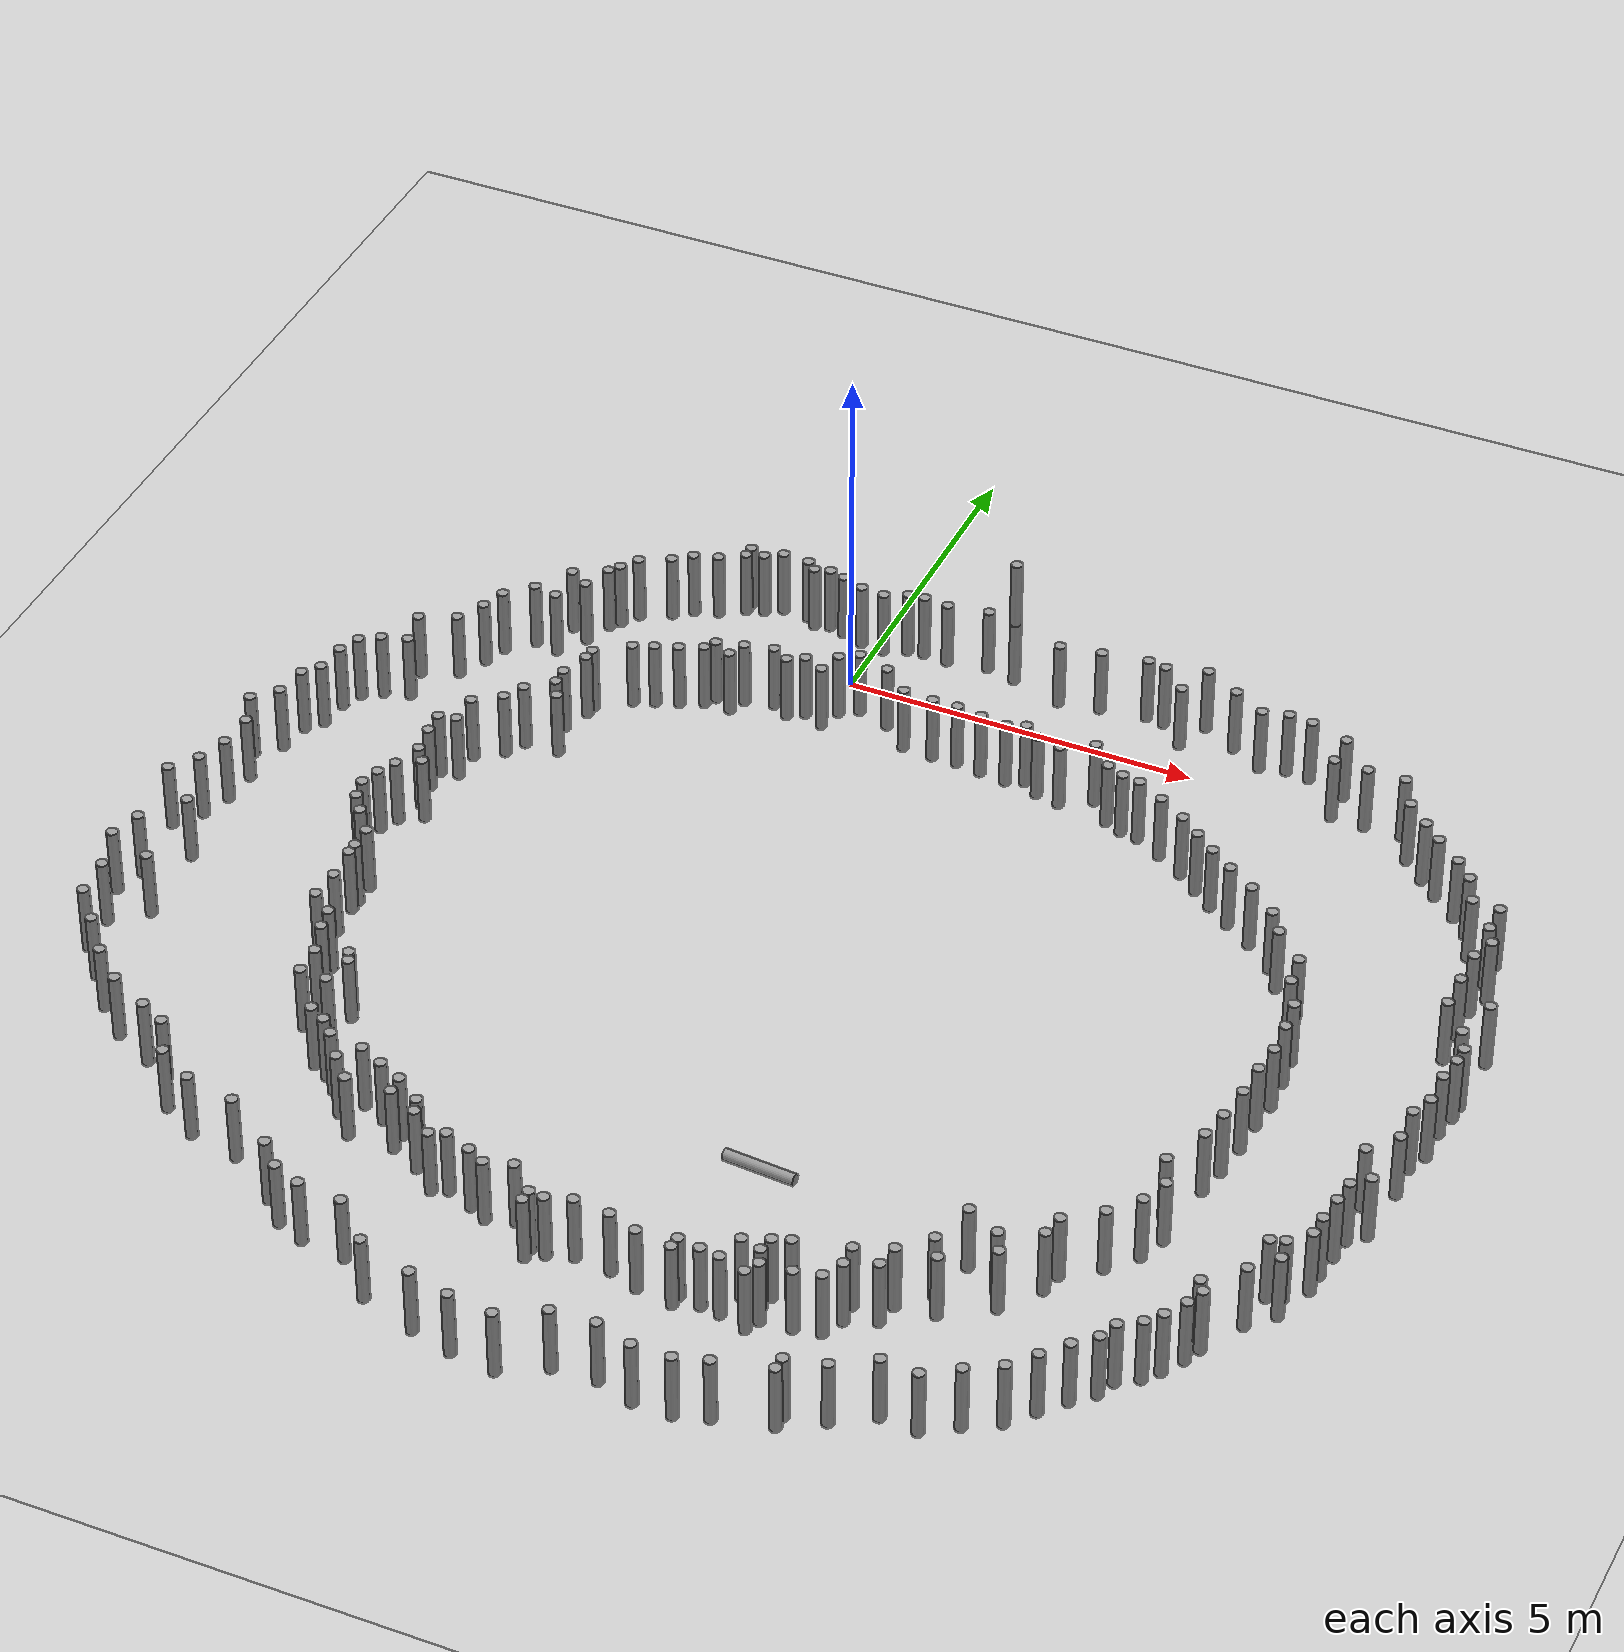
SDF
<sdf version="1.6">
 <world name="default">
  <light name="sun" type="directional">
   <pose>0 0 10 0 -0 0</pose>
   <diffuse>0.8 0.8 0.8 1</diffuse>
   <specular>0.1 0.1 0.1 1</specular>
   <attenuation>
    <range>1000</range>
    <constant>0.9</constant>
    <linear>0.01</linear>
    <quadratic>0.001</quadratic>
   </attenuation>
   <direction>-0.5 0.5 -1</direction>
  </light>
  <model name="ground_plane">
   <static>1</static>
   <link name="link">
    <collision name="collision">
     <geometry><plane><normal>0 0 1</normal><size>100 100</size></plane></geometry>
     <surface><friction><ode><mu>100</mu><mu2>50</mu2></ode></friction></surface>
    </collision>
    <visual name="visual">
     <cast_shadows>0</cast_shadows>
     <geometry><plane><normal>0 0 1</normal><size>100 100</size></plane></geometry>
     <material>
      <script><uri>file://media/materials/scripts/gazebo.material</uri><name>Gazebo/Grey</name></script>
     </material>
    </visual>
   </link>
  </model>
  <gravity>0 0 -9.8</gravity>
  <magnetic_field>6e-06 2.3e-05 -4.2e-05</magnetic_field>
  <atmosphere type="adiabatic"/>
  <physics name="default_physics" default="0" type="ode">
   <max_step_size>0.001</max_step_size>
   <real_time_factor>1</real_time_factor>
   <real_time_update_rate>1000</real_time_update_rate>
  </physics>
  <scene><ambient>0.4 0.4 0.4 1</ambient><background>0.7 0.7 0.7 1</background><shadows>1</shadows></scene>
  <spherical_coordinates>
   <surface_model>EARTH_WGS84</surface_model>
   <latitude_deg>0</latitude_deg>
   <longitude_deg>0</longitude_deg>
   <elevation>0</elevation>
   <heading_deg>0</heading_deg>
  </spherical_coordinates>
  <model name="unit_cylinder_0">
   <pose>0.355357 -0.504616 0.499995 0 0 -1.4e-05</pose>
   <link name="link">
    <inertial>
     <mass>1</mass>
     <inertia><ixx>0.145833</ixx><ixy>0</ixy><ixz>0</ixz><iyy>0.145833</iyy><iyz>0</iyz><izz>0.125</izz></inertia>
    </inertial>
    <collision name="collision">
     <geometry><cylinder><radius>0.0811365</radius><length>1</length></cylinder></geometry>
    </collision>
    <visual name="visual">
     <geometry><cylinder><radius>0.0811365</radius><length>1</length></cylinder></geometry>
     <material>
      <script><name>Gazebo/Grey</name><uri>file://media/materials/scripts/gazebo.material</uri></script>
     </material>
    </visual>
   </link>
  </model>
  <model name="unit_cylinder_0_clone">
   <pose>0.817751 -0.645619 0.499993 0 -0 0.003141</pose>
   <link name="link">
    <inertial>
     <mass>1</mass>
     <inertia><ixx>0.145833</ixx><ixy>0</ixy><ixz>0</ixz><iyy>0.145833</iyy><iyz>0</iyz><izz>0.125</izz></inertia>
    </inertial>
    <collision name="collision">
     <geometry><cylinder><radius>0.0811363</radius><length>1</length></cylinder></geometry>
    </collision>
    <visual name="visual">
     <geometry><cylinder><radius>0.0811363</radius><length>1</length></cylinder></geometry>
     <material>
      <script><name>Gazebo/Grey</name><uri>file://media/materials/scripts/gazebo.material</uri></script>
     </material>
    </visual>
   </link>
  </model>
  <model name="unit_cylinder_0_clone_clone">
   <pose>1.20742 -0.981702 0.5 0 -0 0.006974</pose>
   <link name="link">
    <inertial>
     <mass>1</mass>
     <inertia><ixx>0.145833</ixx><ixy>0</ixy><ixz>0</ixz><iyy>0.145833</iyy><iyz>0</iyz><izz>0.125</izz></inertia>
    </inertial>
    <collision name="collision">
     <geometry><cylinder><radius>0.0811363</radius><length>1</length></cylinder></geometry>
    </collision>
    <visual name="visual">
     <geometry><cylinder><radius>0.0811363</radius><length>1</length></cylinder></geometry>
     <material>
      <script><name>Gazebo/Grey</name><uri>file://media/materials/scripts/gazebo.material</uri></script>
     </material>
    </visual>
   </link>
  </model>
  <model name="unit_cylinder_0_clone_clone_0">
   <pose>1.64335 -1.00984 0.499996 0 -0 0.005383</pose>
   <link name="link">
    <inertial>
     <mass>1</mass>
     <inertia><ixx>0.145833</ixx><ixy>0</ixy><ixz>0</ixz><iyy>0.145833</iyy><iyz>0</iyz><izz>0.125</izz></inertia>
    </inertial>
    <collision name="collision">
     <geometry><cylinder><radius>0.0811363</radius><length>1</length></cylinder></geometry>
    </collision>
    <visual name="visual">
     <geometry><cylinder><radius>0.0811363</radius><length>1</length></cylinder></geometry>
     <material>
      <script><name>Gazebo/Grey</name><uri>file://media/materials/scripts/gazebo.material</uri></script>
     </material>
    </visual>
   </link>
  </model>
  <model name="unit_cylinder_0_clone_clone_1">
   <pose>2 -0.999981 0.499996 0 -0 0.001293</pose>
   <link name="link">
    <inertial>
     <mass>1</mass>
     <inertia><ixx>0.145833</ixx><ixy>0</ixy><ixz>0</ixz><iyy>0.145833</iyy><iyz>0</iyz><izz>0.125</izz></inertia>
    </inertial>
    <collision name="collision">
     <geometry><cylinder><radius>0.0811363</radius><length>1</length></cylinder></geometry>
    </collision>
    <visual name="visual">
     <geometry><cylinder><radius>0.0811363</radius><length>1</length></cylinder></geometry>
     <material>
      <script><name>Gazebo/Grey</name><uri>file://media/materials/scripts/gazebo.material</uri></script>
     </material>
    </visual>
   </link>
  </model>
  <model name="unit_cylinder_0_clone_clone_2">
   <pose>2.36742 -1.05536 0.499996 0 -0 0.00225</pose>
   <link name="link">
    <inertial>
     <mass>1</mass>
     <inertia><ixx>0.145833</ixx><ixy>0</ixy><ixz>0</ixz><iyy>0.145833</iyy><iyz>0</iyz><izz>0.125</izz></inertia>
    </inertial>
    <collision name="collision">
     <geometry><cylinder><radius>0.0811363</radius><length>1</length></cylinder></geometry>
    </collision>
    <visual name="visual">
     <geometry><cylinder><radius>0.0811363</radius><length>1</length></cylinder></geometry>
     <material>
      <script><name>Gazebo/Grey</name><uri>file://media/materials/scripts/gazebo.material</uri></script>
     </material>
    </visual>
   </link>
  </model>
  <model name="unit_cylinder_0_clone_clone_3">
   <pose>2.74832 -1.09921 0.499995 0 -0 0.001643</pose>
   <link name="link">
    <inertial>
     <mass>1</mass>
     <inertia><ixx>0.145833</ixx><ixy>0</ixy><ixz>0</ixz><iyy>0.145833</iyy><iyz>0</iyz><izz>0.125</izz></inertia>
    </inertial>
    <collision name="collision">
     <geometry><cylinder><radius>0.0811363</radius><length>1</length></cylinder></geometry>
    </collision>
    <visual name="visual">
     <geometry><cylinder><radius>0.0811363</radius><length>1</length></cylinder></geometry>
     <material>
      <script><name>Gazebo/Grey</name><uri>file://media/materials/scripts/gazebo.material</uri></script>
     </material>
    </visual>
   </link>
  </model>
  <model name="unit_cylinder_0_clone_clone_4">
   <pose>3 -0.999956 0.499995 0 -0 0.002912</pose>
   <link name="link">
    <inertial>
     <mass>1</mass>
     <inertia><ixx>0.145833</ixx><ixy>0</ixy><ixz>0</ixz><iyy>0.145833</iyy><iyz>0</iyz><izz>0.125</izz></inertia>
    </inertial>
    <collision name="collision">
     <geometry><cylinder><radius>0.0811363</radius><length>1</length></cylinder></geometry>
    </collision>
    <visual name="visual">
     <geometry><cylinder><radius>0.0811363</radius><length>1</length></cylinder></geometry>
     <material>
      <script><name>Gazebo/Grey</name><uri>file://media/materials/scripts/gazebo.material</uri></script>
     </material>
    </visual>
   </link>
  </model>
  <model name="unit_cylinder_0_clone_clone_5">
   <pose>3.2365 -1.17147 0.5 0 -0 0.007308</pose>
   <link name="link">
    <inertial>
     <mass>1</mass>
     <inertia><ixx>0.145833</ixx><ixy>0</ixy><ixz>0</ixz><iyy>0.145833</iyy><iyz>0</iyz><izz>0.125</izz></inertia>
    </inertial>
    <collision name="collision">
     <geometry><cylinder><radius>0.0811363</radius><length>1</length></cylinder></geometry>
    </collision>
    <visual name="visual">
     <geometry><cylinder><radius>0.0811363</radius><length>1</length></cylinder></geometry>
     <material>
      <script><name>Gazebo/Grey</name><uri>file://media/materials/scripts/gazebo.material</uri></script>
     </material>
    </visual>
   </link>
  </model>
  <model name="unit_cylinder_0_clone_clone_6">
   <pose>3.58637 -1.24743 0.5 0 -0 0.007195</pose>
   <link name="link">
    <inertial>
     <mass>1</mass>
     <inertia><ixx>0.145833</ixx><ixy>0</ixy><ixz>0</ixz><iyy>0.145833</iyy><iyz>0</iyz><izz>0.125</izz></inertia>
    </inertial>
    <collision name="collision">
     <geometry><cylinder><radius>0.0811363</radius><length>1</length></cylinder></geometry>
    </collision>
    <visual name="visual">
     <geometry><cylinder><radius>0.0811363</radius><length>1</length></cylinder></geometry>
     <material>
      <script><name>Gazebo/Grey</name><uri>file://media/materials/scripts/gazebo.material</uri></script>
     </material>
    </visual>
   </link>
  </model>
  <model name="unit_cylinder_0_clone_clone_7">
   <pose>4.00001 -0.999892 0.5 0 -0 0.007126</pose>
   <link name="link">
    <inertial>
     <mass>1</mass>
     <inertia><ixx>0.145833</ixx><ixy>0</ixy><ixz>0</ixz><iyy>0.145833</iyy><iyz>0</iyz><izz>0.125</izz></inertia>
    </inertial>
    <collision name="collision">
     <geometry><cylinder><radius>0.0811363</radius><length>1</length></cylinder></geometry>
    </collision>
    <visual name="visual">
     <geometry><cylinder><radius>0.0811363</radius><length>1</length></cylinder></geometry>
     <material>
      <script><name>Gazebo/Grey</name><uri>file://media/materials/scripts/gazebo.material</uri></script>
     </material>
    </visual>
   </link>
  </model>
  <model name="unit_cylinder_0_clone_clone_8">
   <pose>4.31062 -1.33961 0.499996 0 -0 0.001173</pose>
   <link name="link">
    <inertial>
     <mass>1</mass>
     <inertia><ixx>0.145833</ixx><ixy>0</ixy><ixz>0</ixz><iyy>0.145833</iyy><iyz>0</iyz><izz>0.125</izz></inertia>
    </inertial>
    <collision name="collision">
     <geometry><cylinder><radius>0.0811363</radius><length>1</length></cylinder></geometry>
    </collision>
    <visual name="visual">
     <geometry><cylinder><radius>0.0811363</radius><length>1</length></cylinder></geometry>
     <material>
      <script><name>Gazebo/Grey</name><uri>file://media/materials/scripts/gazebo.material</uri></script>
     </material>
    </visual>
   </link>
  </model>
  <model name="unit_cylinder_0_clone_clone_9">
   <pose>4.56147 -1.44928 0.499997 0 0 -0.000367</pose>
   <link name="link">
    <inertial>
     <mass>1</mass>
     <inertia><ixx>0.145833</ixx><ixy>0</ixy><ixz>0</ixz><iyy>0.145833</iyy><iyz>0</iyz><izz>0.125</izz></inertia>
    </inertial>
    <collision name="collision">
     <geometry><cylinder><radius>0.0811363</radius><length>1</length></cylinder></geometry>
    </collision>
    <visual name="visual">
     <geometry><cylinder><radius>0.0811363</radius><length>1</length></cylinder></geometry>
     <material>
      <script><name>Gazebo/Grey</name><uri>file://media/materials/scripts/gazebo.material</uri></script>
     </material>
    </visual>
   </link>
  </model>
  <model name="unit_cylinder_0_clone_clone_10">
   <pose>4.81966 -1.49016 0.499997 0 -0 0.001801</pose>
   <link name="link">
    <inertial>
     <mass>1</mass>
     <inertia><ixx>0.145833</ixx><ixy>0</ixy><ixz>0</ixz><iyy>0.145833</iyy><iyz>0</iyz><izz>0.125</izz></inertia>
    </inertial>
    <collision name="collision">
     <geometry><cylinder><radius>0.0811363</radius><length>1</length></cylinder></geometry>
    </collision>
    <visual name="visual">
     <geometry><cylinder><radius>0.0811363</radius><length>1</length></cylinder></geometry>
     <material>
      <script><name>Gazebo/Grey</name><uri>file://media/materials/scripts/gazebo.material</uri></script>
     </material>
    </visual>
   </link>
  </model>
  <model name="unit_cylinder_0_clone_clone_11">
   <pose>5.21247 -1.70304 0.5 0 -0 0.001459</pose>
   <link name="link">
    <inertial>
     <mass>1</mass>
     <inertia><ixx>0.145833</ixx><ixy>0</ixy><ixz>0</ixz><iyy>0.145833</iyy><iyz>0</iyz><izz>0.125</izz></inertia>
    </inertial>
    <collision name="collision">
     <geometry><cylinder><radius>0.0811363</radius><length>1</length></cylinder></geometry>
    </collision>
    <visual name="visual">
     <geometry><cylinder><radius>0.0811363</radius><length>1</length></cylinder></geometry>
     <material>
      <script><name>Gazebo/Grey</name><uri>file://media/materials/scripts/gazebo.material</uri></script>
     </material>
    </visual>
   </link>
  </model>
  <model name="unit_cylinder_0_clone_clone_12">
   <pose>5.60903 -1.94656 0.5 0 -0 0.006621</pose>
   <link name="link">
    <inertial>
     <mass>1</mass>
     <inertia><ixx>0.145833</ixx><ixy>0</ixy><ixz>0</ixz><iyy>0.145833</iyy><iyz>0</iyz><izz>0.125</izz></inertia>
    </inertial>
    <collision name="collision">
     <geometry><cylinder><radius>0.0811363</radius><length>1</length></cylinder></geometry>
    </collision>
    <visual name="visual">
     <geometry><cylinder><radius>0.0811363</radius><length>1</length></cylinder></geometry>
     <material>
      <script><name>Gazebo/Grey</name><uri>file://media/materials/scripts/gazebo.material</uri></script>
     </material>
    </visual>
   </link>
  </model>
  <model name="unit_cylinder_0_clone_clone_13">
   <pose>5.90833 -2.18001 0.499995 0 -0 0.005195</pose>
   <link name="link">
    <inertial>
     <mass>1</mass>
     <inertia><ixx>0.145833</ixx><ixy>0</ixy><ixz>0</ixz><iyy>0.145833</iyy><iyz>0</iyz><izz>0.125</izz></inertia>
    </inertial>
    <collision name="collision">
     <geometry><cylinder><radius>0.0811363</radius><length>1</length></cylinder></geometry>
    </collision>
    <visual name="visual">
     <geometry><cylinder><radius>0.0811363</radius><length>1</length></cylinder></geometry>
     <material>
      <script><name>Gazebo/Grey</name><uri>file://media/materials/scripts/gazebo.material</uri></script>
     </material>
    </visual>
   </link>
  </model>
  <model name="unit_cylinder_0_clone_clone_14">
   <pose>6.20582 -2.41061 0.499996 0 -0 0.001539</pose>
   <link name="link">
    <inertial>
     <mass>1</mass>
     <inertia><ixx>0.145833</ixx><ixy>0</ixy><ixz>0</ixz><iyy>0.145833</iyy><iyz>0</iyz><izz>0.125</izz></inertia>
    </inertial>
    <collision name="collision">
     <geometry><cylinder><radius>0.0811363</radius><length>1</length></cylinder></geometry>
    </collision>
    <visual name="visual">
     <geometry><cylinder><radius>0.0811363</radius><length>1</length></cylinder></geometry>
     <material>
      <script><name>Gazebo/Grey</name><uri>file://media/materials/scripts/gazebo.material</uri></script>
     </material>
    </visual>
   </link>
  </model>
  <model name="unit_cylinder_0_clone_clone_15">
   <pose>6.54594 -2.64942 0.49999 0 -0 0.006857</pose>
   <link name="link">
    <inertial>
     <mass>1</mass>
     <inertia><ixx>0.145833</ixx><ixy>0</ixy><ixz>0</ixz><iyy>0.145833</iyy><iyz>0</iyz><izz>0.125</izz></inertia>
    </inertial>
    <collision name="collision">
     <geometry><cylinder><radius>0.0811363</radius><length>1</length></cylinder></geometry>
    </collision>
    <visual name="visual">
     <geometry><cylinder><radius>0.0811363</radius><length>1</length></cylinder></geometry>
     <material>
      <script><name>Gazebo/Grey</name><uri>file://media/materials/scripts/gazebo.material</uri></script>
     </material>
    </visual>
   </link>
  </model>
  <model name="unit_cylinder_0_clone_clone_16">
   <pose>6.94427 -2.90983 0.49999 0 -0 0.006685</pose>
   <link name="link">
    <inertial>
     <mass>1</mass>
     <inertia><ixx>0.145833</ixx><ixy>0</ixy><ixz>0</ixz><iyy>0.145833</iyy><iyz>0</iyz><izz>0.125</izz></inertia>
    </inertial>
    <collision name="collision">
     <geometry><cylinder><radius>0.0811363</radius><length>1</length></cylinder></geometry>
    </collision>
    <visual name="visual">
     <geometry><cylinder><radius>0.0811363</radius><length>1</length></cylinder></geometry>
     <material>
      <script><name>Gazebo/Grey</name><uri>file://media/materials/scripts/gazebo.material</uri></script>
     </material>
    </visual>
   </link>
  </model>
  <model name="unit_cylinder_0_clone_clone_17">
   <pose>7.35958 -3.25844 0.499996 0 -0 0.002099</pose>
   <link name="link">
    <inertial>
     <mass>1</mass>
     <inertia><ixx>0.145833</ixx><ixy>0</ixy><ixz>0</ixz><iyy>0.145833</iyy><iyz>0</iyz><izz>0.125</izz></inertia>
    </inertial>
    <collision name="collision">
     <geometry><cylinder><radius>0.0811363</radius><length>1</length></cylinder></geometry>
    </collision>
    <visual name="visual">
     <geometry><cylinder><radius>0.0811363</radius><length>1</length></cylinder></geometry>
     <material>
      <script><name>Gazebo/Grey</name><uri>file://media/materials/scripts/gazebo.material</uri></script>
     </material>
    </visual>
   </link>
  </model>
  <model name="unit_cylinder_0_clone_clone_18">
   <pose>7.5713 -3.5818 0.49999 0 -0 0.006562</pose>
   <link name="link">
    <inertial>
     <mass>1</mass>
     <inertia><ixx>0.145833</ixx><ixy>0</ixy><ixz>0</ixz><iyy>0.145833</iyy><iyz>0</iyz><izz>0.125</izz></inertia>
    </inertial>
    <collision name="collision">
     <geometry><cylinder><radius>0.0811363</radius><length>1</length></cylinder></geometry>
    </collision>
    <visual name="visual">
     <geometry><cylinder><radius>0.0811363</radius><length>1</length></cylinder></geometry>
     <material>
      <script><name>Gazebo/Grey</name><uri>file://media/materials/scripts/gazebo.material</uri></script>
     </material>
    </visual>
   </link>
  </model>
  <model name="unit_cylinder_0_clone_clone_19">
   <pose>8.00001 -3.99991 0.5 0 -0 0.005774</pose>
   <link name="link">
    <inertial>
     <mass>1</mass>
     <inertia><ixx>0.145833</ixx><ixy>0</ixy><ixz>0</ixz><iyy>0.145833</iyy><iyz>0</iyz><izz>0.125</izz></inertia>
    </inertial>
    <collision name="collision">
     <geometry><cylinder><radius>0.0811363</radius><length>1</length></cylinder></geometry>
    </collision>
    <visual name="visual">
     <geometry><cylinder><radius>0.0811363</radius><length>1</length></cylinder></geometry>
     <material>
      <script><name>Gazebo/Grey</name><uri>file://media/materials/scripts/gazebo.material</uri></script>
     </material>
    </visual>
   </link>
  </model>
  <model name="unit_cylinder_0_clone_clone_20">
   <pose>8.05288 -4.42291 0.49999 0 -0 0.006538</pose>
   <link name="link">
    <inertial>
     <mass>1</mass>
     <inertia><ixx>0.145833</ixx><ixy>0</ixy><ixz>0</ixz><iyy>0.145833</iyy><iyz>0</iyz><izz>0.125</izz></inertia>
    </inertial>
    <collision name="collision">
     <geometry><cylinder><radius>0.0811363</radius><length>1</length></cylinder></geometry>
    </collision>
    <visual name="visual">
     <geometry><cylinder><radius>0.0811363</radius><length>1</length></cylinder></geometry>
     <material>
      <script><name>Gazebo/Grey</name><uri>file://media/materials/scripts/gazebo.material</uri></script>
     </material>
    </visual>
   </link>
  </model>
  <model name="unit_cylinder_0_clone_clone_21">
   <pose>8.2496 -4.83508 0.499996 0 -0 0.001923</pose>
   <link name="link">
    <inertial>
     <mass>1</mass>
     <inertia><ixx>0.145833</ixx><ixy>0</ixy><ixz>0</ixz><iyy>0.145833</iyy><iyz>0</iyz><izz>0.125</izz></inertia>
    </inertial>
    <collision name="collision">
     <geometry><cylinder><radius>0.0811363</radius><length>1</length></cylinder></geometry>
    </collision>
    <visual name="visual">
     <geometry><cylinder><radius>0.0811363</radius><length>1</length></cylinder></geometry>
     <material>
      <script><name>Gazebo/Grey</name><uri>file://media/materials/scripts/gazebo.material</uri></script>
     </material>
    </visual>
   </link>
  </model>
  <model name="unit_cylinder_0_clone_clone_22">
   <pose>8.29837 -5.26887 0.49999 0 -0 0.006525</pose>
   <link name="link">
    <inertial>
     <mass>1</mass>
     <inertia><ixx>0.145833</ixx><ixy>0</ixy><ixz>0</ixz><iyy>0.145833</iyy><iyz>0</iyz><izz>0.125</izz></inertia>
    </inertial>
    <collision name="collision">
     <geometry><cylinder><radius>0.0811363</radius><length>1</length></cylinder></geometry>
    </collision>
    <visual name="visual">
     <geometry><cylinder><radius>0.0811363</radius><length>1</length></cylinder></geometry>
     <material>
      <script><name>Gazebo/Grey</name><uri>file://media/materials/scripts/gazebo.material</uri></script>
     </material>
    </visual>
   </link>
  </model>
  <model name="unit_cylinder_0_clone_clone_23">
   <pose>8.32518 -5.7385 0.499997 0 -0 0.002395</pose>
   <link name="link">
    <inertial>
     <mass>1</mass>
     <inertia><ixx>0.145833</ixx><ixy>0</ixy><ixz>0</ixz><iyy>0.145833</iyy><iyz>0</iyz><izz>0.125</izz></inertia>
    </inertial>
    <collision name="collision">
     <geometry><cylinder><radius>0.0811363</radius><length>1</length></cylinder></geometry>
    </collision>
    <visual name="visual">
     <geometry><cylinder><radius>0.0811363</radius><length>1</length></cylinder></geometry>
     <material>
      <script><name>Gazebo/Grey</name><uri>file://media/materials/scripts/gazebo.material</uri></script>
     </material>
    </visual>
   </link>
  </model>
  <model name="unit_cylinder_0_clone_clone_24">
   <pose>8.27565 -6.15295 0.5 0 -0 0.006248</pose>
   <link name="link">
    <inertial>
     <mass>1</mass>
     <inertia><ixx>0.145833</ixx><ixy>0</ixy><ixz>0</ixz><iyy>0.145833</iyy><iyz>0</iyz><izz>0.125</izz></inertia>
    </inertial>
    <collision name="collision">
     <geometry><cylinder><radius>0.0811363</radius><length>1</length></cylinder></geometry>
    </collision>
    <visual name="visual">
     <geometry><cylinder><radius>0.0811363</radius><length>1</length></cylinder></geometry>
     <material>
      <script><name>Gazebo/Grey</name><uri>file://media/materials/scripts/gazebo.material</uri></script>
     </material>
    </visual>
   </link>
  </model>
  <model name="unit_cylinder_0_clone_clone_25">
   <pose>8.25488 -6.63845 0.499996 0 -0 0.000607</pose>
   <link name="link">
    <inertial>
     <mass>1</mass>
     <inertia><ixx>0.145833</ixx><ixy>0</ixy><ixz>0</ixz><iyy>0.145833</iyy><iyz>0</iyz><izz>0.125</izz></inertia>
    </inertial>
    <collision name="collision">
     <geometry><cylinder><radius>0.0811363</radius><length>1</length></cylinder></geometry>
    </collision>
    <visual name="visual">
     <geometry><cylinder><radius>0.0811363</radius><length>1</length></cylinder></geometry>
     <material>
      <script><name>Gazebo/Grey</name><uri>file://media/materials/scripts/gazebo.material</uri></script>
     </material>
    </visual>
   </link>
  </model>
  <model name="unit_cylinder_0_clone_clone_26">
   <pose>8.18981 -7.13687 0.49999 0 -0 0.006208</pose>
   <link name="link">
    <inertial>
     <mass>1</mass>
     <inertia><ixx>0.145833</ixx><ixy>0</ixy><ixz>0</ixz><iyy>0.145833</iyy><iyz>0</iyz><izz>0.125</izz></inertia>
    </inertial>
    <collision name="collision">
     <geometry><cylinder><radius>0.0811363</radius><length>1</length></cylinder></geometry>
    </collision>
    <visual name="visual">
     <geometry><cylinder><radius>0.0811363</radius><length>1</length></cylinder></geometry>
     <material>
      <script><name>Gazebo/Grey</name><uri>file://media/materials/scripts/gazebo.material</uri></script>
     </material>
    </visual>
   </link>
  </model>
  <model name="unit_cylinder_0_clone_clone_27">
   <pose>8.10835 -7.5553 0.49999 0 -0 0.006155</pose>
   <link name="link">
    <inertial>
     <mass>1</mass>
     <inertia><ixx>0.145833</ixx><ixy>0</ixy><ixz>0</ixz><iyy>0.145833</iyy><iyz>0</iyz><izz>0.125</izz></inertia>
    </inertial>
    <collision name="collision">
     <geometry><cylinder><radius>0.0811363</radius><length>1</length></cylinder></geometry>
    </collision>
    <visual name="visual">
     <geometry><cylinder><radius>0.0811363</radius><length>1</length></cylinder></geometry>
     <material>
      <script><name>Gazebo/Grey</name><uri>file://media/materials/scripts/gazebo.material</uri></script>
     </material>
    </visual>
   </link>
  </model>
  <model name="unit_cylinder_0_clone_clone_28">
   <pose>7.84183 -8.16999 0.49999 0 -0 0.006186</pose>
   <link name="link">
    <inertial>
     <mass>1</mass>
     <inertia><ixx>0.145833</ixx><ixy>0</ixy><ixz>0</ixz><iyy>0.145833</iyy><iyz>0</iyz><izz>0.125</izz></inertia>
    </inertial>
    <collision name="collision">
     <geometry><cylinder><radius>0.0811363</radius><length>1</length></cylinder></geometry>
    </collision>
    <visual name="visual">
     <geometry><cylinder><radius>0.0811363</radius><length>1</length></cylinder></geometry>
     <material>
      <script><name>Gazebo/Grey</name><uri>file://media/materials/scripts/gazebo.material</uri></script>
     </material>
    </visual>
   </link>
  </model>
  <model name="unit_cylinder_0_clone_clone_29">
   <pose>8.00004 -8.58037 0.499993 0 0 -0.000846</pose>
   <link name="link">
    <inertial>
     <mass>1</mass>
     <inertia><ixx>0.145833</ixx><ixy>0</ixy><ixz>0</ixz><iyy>0.145833</iyy><iyz>0</iyz><izz>0.125</izz></inertia>
    </inertial>
    <collision name="collision">
     <geometry><cylinder><radius>0.0811363</radius><length>1</length></cylinder></geometry>
    </collision>
    <visual name="visual">
     <geometry><cylinder><radius>0.0811363</radius><length>1</length></cylinder></geometry>
     <material>
      <script><name>Gazebo/Grey</name><uri>file://media/materials/scripts/gazebo.material</uri></script>
     </material>
    </visual>
   </link>
  </model>
  <model name="unit_cylinder_0_clone_clone_30">
   <pose>7.85394 -8.96392 0.499995 0 -0 0.002711</pose>
   <link name="link">
    <inertial>
     <mass>1</mass>
     <inertia><ixx>0.145833</ixx><ixy>0</ixy><ixz>0</ixz><iyy>0.145833</iyy><iyz>0</iyz><izz>0.125</izz></inertia>
    </inertial>
    <collision name="collision">
     <geometry><cylinder><radius>0.0811363</radius><length>1</length></cylinder></geometry>
    </collision>
    <visual name="visual">
     <geometry><cylinder><radius>0.0811363</radius><length>1</length></cylinder></geometry>
     <material>
      <script><name>Gazebo/Grey</name><uri>file://media/materials/scripts/gazebo.material</uri></script>
     </material>
    </visual>
   </link>
  </model>
  <model name="unit_cylinder_0_clone_clone_31">
   <pose>7.52159 -9.342 0.49999 0 -0 0.005889</pose>
   <link name="link">
    <inertial>
     <mass>1</mass>
     <inertia><ixx>0.145833</ixx><ixy>0</ixy><ixz>0</ixz><iyy>0.145833</iyy><iyz>0</iyz><izz>0.125</izz></inertia>
    </inertial>
    <collision name="collision">
     <geometry><cylinder><radius>0.0811363</radius><length>1</length></cylinder></geometry>
    </collision>
    <visual name="visual">
     <geometry><cylinder><radius>0.0811363</radius><length>1</length></cylinder></geometry>
     <material>
      <script><name>Gazebo/Grey</name><uri>file://media/materials/scripts/gazebo.material</uri></script>
     </material>
    </visual>
   </link>
  </model>
  <model name="unit_cylinder_0_clone_clone_32">
   <pose>5.98452 -10.9288 0.5 0 -0 0.005995</pose>
   <link name="link">
    <inertial>
     <mass>1</mass>
     <inertia><ixx>0.145833</ixx><ixy>0</ixy><ixz>0</ixz><iyy>0.145833</iyy><iyz>0</iyz><izz>0.125</izz></inertia>
    </inertial>
    <collision name="collision">
     <geometry><cylinder><radius>0.0811363</radius><length>1</length></cylinder></geometry>
    </collision>
    <visual name="visual">
     <geometry><cylinder><radius>0.0811363</radius><length>1</length></cylinder></geometry>
     <material>
      <script><name>Gazebo/Grey</name><uri>file://media/materials/scripts/gazebo.material</uri></script>
     </material>
    </visual>
   </link>
  </model>
  <model name="unit_cylinder_0_clone_clone_33">
   <pose>3.00714 -11.919 0.499993 0 -0 0.003414</pose>
   <link name="link">
    <inertial>
     <mass>1</mass>
     <inertia><ixx>0.145833</ixx><ixy>0</ixy><ixz>0</ixz><iyy>0.145833</iyy><iyz>0</iyz><izz>0.125</izz></inertia>
    </inertial>
    <collision name="collision">
     <geometry><cylinder><radius>0.0811363</radius><length>1</length></cylinder></geometry>
    </collision>
    <visual name="visual">
     <geometry><cylinder><radius>0.0811363</radius><length>1</length></cylinder></geometry>
     <material>
      <script><name>Gazebo/Grey</name><uri>file://media/materials/scripts/gazebo.material</uri></script>
     </material>
    </visual>
   </link>
  </model>
  <model name="unit_cylinder_0_clone_clone_34">
   <pose>-0.589688 -11.484 0.49999 0 -0 0.005834</pose>
   <link name="link">
    <inertial>
     <mass>1</mass>
     <inertia><ixx>0.145833</ixx><ixy>0</ixy><ixz>0</ixz><iyy>0.145833</iyy><iyz>0</iyz><izz>0.125</izz></inertia>
    </inertial>
    <collision name="collision">
     <geometry><cylinder><radius>0.0811363</radius><length>1</length></cylinder></geometry>
    </collision>
    <visual name="visual">
     <geometry><cylinder><radius>0.0811363</radius><length>1</length></cylinder></geometry>
     <material>
      <script><name>Gazebo/Grey</name><uri>file://media/materials/scripts/gazebo.material</uri></script>
     </material>
    </visual>
   </link>
  </model>
  <model name="unit_cylinder_0_clone_clone_35">
   <pose>-2.99997 -9.99996 0.499997 0 -0 0.001866</pose>
   <link name="link">
    <inertial>
     <mass>1</mass>
     <inertia><ixx>0.145833</ixx><ixy>0</ixy><ixz>0</ixz><iyy>0.145833</iyy><iyz>0</iyz><izz>0.125</izz></inertia>
    </inertial>
    <collision name="collision">
     <geometry><cylinder><radius>0.0811363</radius><length>1</length></cylinder></geometry>
    </collision>
    <visual name="visual">
     <geometry><cylinder><radius>0.0811363</radius><length>1</length></cylinder></geometry>
     <material>
      <script><name>Gazebo/Grey</name><uri>file://media/materials/scripts/gazebo.material</uri></script>
     </material>
    </visual>
   </link>
  </model>
  <model name="unit_cylinder_0_clone_clone_36">
   <pose>-4 -7.99996 0.499996 0 -0 0.002922</pose>
   <link name="link">
    <inertial>
     <mass>1</mass>
     <inertia><ixx>0.145833</ixx><ixy>0</ixy><ixz>0</ixz><iyy>0.145833</iyy><iyz>0</iyz><izz>0.125</izz></inertia>
    </inertial>
    <collision name="collision">
     <geometry><cylinder><radius>0.0811363</radius><length>1</length></cylinder></geometry>
    </collision>
    <visual name="visual">
     <geometry><cylinder><radius>0.0811363</radius><length>1</length></cylinder></geometry>
     <material>
      <script><name>Gazebo/Grey</name><uri>file://media/materials/scripts/gazebo.material</uri></script>
     </material>
    </visual>
   </link>
  </model>
  <model name="unit_cylinder_0_clone_clone_37">
   <pose>-4.45742 -5.99996 0.499997 0 -0 0.001784</pose>
   <link name="link">
    <inertial>
     <mass>1</mass>
     <inertia><ixx>0.145833</ixx><ixy>0</ixy><ixz>0</ixz><iyy>0.145833</iyy><iyz>0</iyz><izz>0.125</izz></inertia>
    </inertial>
    <collision name="collision">
     <geometry><cylinder><radius>0.0811363</radius><length>1</length></cylinder></geometry>
    </collision>
    <visual name="visual">
     <geometry><cylinder><radius>0.0811363</radius><length>1</length></cylinder></geometry>
     <material>
      <script><name>Gazebo/Grey</name><uri>file://media/materials/scripts/gazebo.material</uri></script>
     </material>
    </visual>
   </link>
  </model>
  <model name="unit_cylinder_0_clone_clone_38">
   <pose>-4.24607 -4.05302 0.49999 0 -0 0.004737</pose>
   <link name="link">
    <inertial>
     <mass>1</mass>
     <inertia><ixx>0.145833</ixx><ixy>0</ixy><ixz>0</ixz><iyy>0.145833</iyy><iyz>0</iyz><izz>0.125</izz></inertia>
    </inertial>
    <collision name="collision">
     <geometry><cylinder><radius>0.0811363</radius><length>1</length></cylinder></geometry>
    </collision>
    <visual name="visual">
     <geometry><cylinder><radius>0.0811363</radius><length>1</length></cylinder></geometry>
     <material>
      <script><name>Gazebo/Grey</name><uri>file://media/materials/scripts/gazebo.material</uri></script>
     </material>
    </visual>
   </link>
  </model>
  <model name="unit_cylinder_0_clone_clone_39">
   <pose>-2.99157 -1.91916 0.499993 0 -0 0.0032</pose>
   <link name="link">
    <inertial>
     <mass>1</mass>
     <inertia><ixx>0.145833</ixx><ixy>0</ixy><ixz>0</ixz><iyy>0.145833</iyy><iyz>0</iyz><izz>0.125</izz></inertia>
    </inertial>
    <collision name="collision">
     <geometry><cylinder><radius>0.0811363</radius><length>1</length></cylinder></geometry>
    </collision>
    <visual name="visual">
     <geometry><cylinder><radius>0.0811363</radius><length>1</length></cylinder></geometry>
     <material>
      <script><name>Gazebo/Grey</name><uri>file://media/materials/scripts/gazebo.material</uri></script>
     </material>
    </visual>
   </link>
  </model>
  <model name="unit_cylinder_0_clone_clone_40">
   <pose>-1.1681 -0.958311 0.49999 0 -0 0.005399</pose>
   <link name="link">
    <inertial>
     <mass>1</mass>
     <inertia><ixx>0.145833</ixx><ixy>0</ixy><ixz>0</ixz><iyy>0.145833</iyy><iyz>0</iyz><izz>0.125</izz></inertia>
    </inertial>
    <collision name="collision">
     <geometry><cylinder><radius>0.0811363</radius><length>1</length></cylinder></geometry>
    </collision>
    <visual name="visual">
     <geometry><cylinder><radius>0.0811363</radius><length>1</length></cylinder></geometry>
     <material>
      <script><name>Gazebo/Grey</name><uri>file://media/materials/scripts/gazebo.material</uri></script>
     </material>
    </visual>
   </link>
  </model>
  <model name="unit_cylinder_0_clone_clone_41">
   <pose>7.06387 -9.69066 0.5 0 -0 0.005546</pose>
   <link name="link">
    <inertial>
     <mass>1</mass>
     <inertia><ixx>0.145833</ixx><ixy>0</ixy><ixz>0</ixz><iyy>0.145833</iyy><iyz>0</iyz><izz>0.125</izz></inertia>
    </inertial>
    <collision name="collision">
     <geometry><cylinder><radius>0.0811363</radius><length>1</length></cylinder></geometry>
    </collision>
    <visual name="visual">
     <geometry><cylinder><radius>0.0811363</radius><length>1</length></cylinder></geometry>
     <material>
      <script><name>Gazebo/Grey</name><uri>file://media/materials/scripts/gazebo.material</uri></script>
     </material>
    </visual>
   </link>
  </model>
  <model name="unit_cylinder_0_clone_clone_42">
   <pose>7 -9.99997 0.499996 0 -0 0.00195</pose>
   <link name="link">
    <inertial>
     <mass>1</mass>
     <inertia><ixx>0.145833</ixx><ixy>0</ixy><ixz>0</ixz><iyy>0.145833</iyy><iyz>0</iyz><izz>0.125</izz></inertia>
    </inertial>
    <collision name="collision">
     <geometry><cylinder><radius>0.0811363</radius><length>1</length></cylinder></geometry>
    </collision>
    <visual name="visual">
     <geometry><cylinder><radius>0.0811363</radius><length>1</length></cylinder></geometry>
     <material>
      <script><name>Gazebo/Grey</name><uri>file://media/materials/scripts/gazebo.material</uri></script>
     </material>
    </visual>
   </link>
  </model>
  <model name="unit_cylinder_0_clone_clone_43">
   <pose>6.00003 -9.99999 0.499993 0 0 -0.000515</pose>
   <link name="link">
    <inertial>
     <mass>1</mass>
     <inertia><ixx>0.145833</ixx><ixy>0</ixy><ixz>0</ixz><iyy>0.145833</iyy><iyz>0</iyz><izz>0.125</izz></inertia>
    </inertial>
    <collision name="collision">
     <geometry><cylinder><radius>0.0811363</radius><length>1</length></cylinder></geometry>
    </collision>
    <visual name="visual">
     <geometry><cylinder><radius>0.0811363</radius><length>1</length></cylinder></geometry>
     <material>
      <script><name>Gazebo/Grey</name><uri>file://media/materials/scripts/gazebo.material</uri></script>
     </material>
    </visual>
   </link>
  </model>
  <model name="unit_cylinder_0_clone_clone_44">
   <pose>6.61182 -10.5251 0.499996 0 -0 0.002743</pose>
   <link name="link">
    <inertial>
     <mass>1</mass>
     <inertia><ixx>0.145833</ixx><ixy>0</ixy><ixz>0</ixz><iyy>0.145833</iyy><iyz>0</iyz><izz>0.125</izz></inertia>
    </inertial>
    <collision name="collision">
     <geometry><cylinder><radius>0.0811363</radius><length>1</length></cylinder></geometry>
    </collision>
    <visual name="visual">
     <geometry><cylinder><radius>0.0811363</radius><length>1</length></cylinder></geometry>
     <material>
      <script><name>Gazebo/Grey</name><uri>file://media/materials/scripts/gazebo.material</uri></script>
     </material>
    </visual>
   </link>
  </model>
  <model name="unit_cylinder_0_clone_clone_45">
   <pose>6.47324 -10.2323 0.49999 0 -0 0.005281</pose>
   <link name="link">
    <inertial>
     <mass>1</mass>
     <inertia><ixx>0.145833</ixx><ixy>0</ixy><ixz>0</ixz><iyy>0.145833</iyy><iyz>0</iyz><izz>0.125</izz></inertia>
    </inertial>
    <collision name="collision">
     <geometry><cylinder><radius>0.0811363</radius><length>1</length></cylinder></geometry>
    </collision>
    <visual name="visual">
     <geometry><cylinder><radius>0.0811363</radius><length>1</length></cylinder></geometry>
     <material>
      <script><name>Gazebo/Grey</name><uri>file://media/materials/scripts/gazebo.material</uri></script>
     </material>
    </visual>
   </link>
  </model>
  <model name="unit_cylinder_0_clone_clone_46">
   <pose>5.82302 -10.6278 0.5 0 -0 0.005283</pose>
   <link name="link">
    <inertial>
     <mass>1</mass>
     <inertia><ixx>0.145833</ixx><ixy>0</ixy><ixz>0</ixz><iyy>0.145833</iyy><iyz>0</iyz><izz>0.125</izz></inertia>
    </inertial>
    <collision name="collision">
     <geometry><cylinder><radius>0.0811363</radius><length>1</length></cylinder></geometry>
    </collision>
    <visual name="visual">
     <geometry><cylinder><radius>0.0811363</radius><length>1</length></cylinder></geometry>
     <material>
      <script><name>Gazebo/Grey</name><uri>file://media/materials/scripts/gazebo.material</uri></script>
     </material>
    </visual>
   </link>
  </model>
  <model name="unit_cylinder_0_clone_clone_47">
   <pose>5.45799 -10.9999 0.5 0 -0 0.005037</pose>
   <link name="link">
    <inertial>
     <mass>1</mass>
     <inertia><ixx>0.145833</ixx><ixy>0</ixy><ixz>0</ixz><iyy>0.145833</iyy><iyz>0</iyz><izz>0.125</izz></inertia>
    </inertial>
    <collision name="collision">
     <geometry><cylinder><radius>0.0811363</radius><length>1</length></cylinder></geometry>
    </collision>
    <visual name="visual">
     <geometry><cylinder><radius>0.0811363</radius><length>1</length></cylinder></geometry>
     <material>
      <script><name>Gazebo/Grey</name><uri>file://media/materials/scripts/gazebo.material</uri></script>
     </material>
    </visual>
   </link>
  </model>
  <model name="unit_cylinder_0_clone_clone_48">
   <pose>5.40133 -11.3229 0.49999 0 -0 0.005121</pose>
   <link name="link">
    <inertial>
     <mass>1</mass>
     <inertia><ixx>0.145833</ixx><ixy>0</ixy><ixz>0</ixz><iyy>0.145833</iyy><iyz>0</iyz><izz>0.125</izz></inertia>
    </inertial>
    <collision name="collision">
     <geometry><cylinder><radius>0.0811363</radius><length>1</length></cylinder></geometry>
    </collision>
    <visual name="visual">
     <geometry><cylinder><radius>0.0811363</radius><length>1</length></cylinder></geometry>
     <material>
      <script><name>Gazebo/Grey</name><uri>file://media/materials/scripts/gazebo.material</uri></script>
     </material>
    </visual>
   </link>
  </model>
  <model name="unit_cylinder_0_clone_clone_49">
   <pose>4.99029 -11.1989 0.499993 0 -0 0.002755</pose>
   <link name="link">
    <inertial>
     <mass>1</mass>
     <inertia><ixx>0.145833</ixx><ixy>0</ixy><ixz>0</ixz><iyy>0.145833</iyy><iyz>0</iyz><izz>0.125</izz></inertia>
    </inertial>
    <collision name="collision">
     <geometry><cylinder><radius>0.0811363</radius><length>1</length></cylinder></geometry>
    </collision>
    <visual name="visual">
     <geometry><cylinder><radius>0.0811363</radius><length>1</length></cylinder></geometry>
     <material>
      <script><name>Gazebo/Grey</name><uri>file://media/materials/scripts/gazebo.material</uri></script>
     </material>
    </visual>
   </link>
  </model>
  <model name="unit_cylinder_0_clone_clone_50">
   <pose>5.00002 -11.4951 0.499997 0 -0 0.001776</pose>
   <link name="link">
    <inertial>
     <mass>1</mass>
     <inertia><ixx>0.145833</ixx><ixy>0</ixy><ixz>0</ixz><iyy>0.145833</iyy><iyz>0</iyz><izz>0.125</izz></inertia>
    </inertial>
    <collision name="collision">
     <geometry><cylinder><radius>0.0811363</radius><length>1</length></cylinder></geometry>
    </collision>
    <visual name="visual">
     <geometry><cylinder><radius>0.0811363</radius><length>1</length></cylinder></geometry>
     <material>
      <script><name>Gazebo/Grey</name><uri>file://media/materials/scripts/gazebo.material</uri></script>
     </material>
    </visual>
   </link>
  </model>
  <model name="unit_cylinder_0_clone_clone_51">
   <pose>3.321 -11.9637 0.499997 0 -0 0.003017</pose>
   <link name="link">
    <inertial>
     <mass>1</mass>
     <inertia><ixx>0.145833</ixx><ixy>0</ixy><ixz>0</ixz><iyy>0.145833</iyy><iyz>0</iyz><izz>0.125</izz></inertia>
    </inertial>
    <collision name="collision">
     <geometry><cylinder><radius>0.0811363</radius><length>1</length></cylinder></geometry>
    </collision>
    <visual name="visual">
     <geometry><cylinder><radius>0.0811363</radius><length>1</length></cylinder></geometry>
     <material>
      <script><name>Gazebo/Grey</name><uri>file://media/materials/scripts/gazebo.material</uri></script>
     </material>
    </visual>
   </link>
  </model>
  <model name="unit_cylinder_0_clone_clone_52">
   <pose>2.99309 -12.0807 0.499995 0 -0 0.001645</pose>
   <link name="link">
    <inertial>
     <mass>1</mass>
     <inertia><ixx>0.145833</ixx><ixy>0</ixy><ixz>0</ixz><iyy>0.145833</iyy><iyz>0</iyz><izz>0.125</izz></inertia>
    </inertial>
    <collision name="collision">
     <geometry><cylinder><radius>0.0811363</radius><length>1</length></cylinder></geometry>
    </collision>
    <visual name="visual">
     <geometry><cylinder><radius>0.0811363</radius><length>1</length></cylinder></geometry>
     <material>
      <script><name>Gazebo/Grey</name><uri>file://media/materials/scripts/gazebo.material</uri></script>
     </material>
    </visual>
   </link>
  </model>
  <model name="unit_cylinder_0_clone_clone_53">
   <pose>3.5965 -11.9999 0.49999 0 -0 0.005003</pose>
   <link name="link">
    <inertial>
     <mass>1</mass>
     <inertia><ixx>0.145833</ixx><ixy>0</ixy><ixz>0</ixz><iyy>0.145833</iyy><iyz>0</iyz><izz>0.125</izz></inertia>
    </inertial>
    <collision name="collision">
     <geometry><cylinder><radius>0.0811363</radius><length>1</length></cylinder></geometry>
    </collision>
    <visual name="visual">
     <geometry><cylinder><radius>0.0811363</radius><length>1</length></cylinder></geometry>
     <material>
      <script><name>Gazebo/Grey</name><uri>file://media/materials/scripts/gazebo.material</uri></script>
     </material>
    </visual>
   </link>
  </model>
  <model name="unit_cylinder_0_clone_clone_54">
   <pose>3.70659 -11.6139 0.500745 -0.001533 0.00934 1.94859</pose>
   <link name="link">
    <inertial>
     <mass>1</mass>
     <inertia><ixx>0.145833</ixx><ixy>0</ixy><ixz>0</ixz><iyy>0.145833</iyy><iyz>0</iyz><izz>0.125</izz></inertia>
    </inertial>
    <collision name="collision">
     <geometry><cylinder><radius>0.0811363</radius><length>1</length></cylinder></geometry>
    </collision>
    <visual name="visual">
     <geometry><cylinder><radius>0.0811363</radius><length>1</length></cylinder></geometry>
     <material>
      <script><name>Gazebo/Grey</name><uri>file://media/materials/scripts/gazebo.material</uri></script>
     </material>
    </visual>
   </link>
  </model>
  <model name="unit_cylinder_0_clone_clone_55">
   <pose>2.96637 -9.46984 0.081136 1.5708 -0.619525 1.49835</pose>
   <link name="link">
    <inertial>
     <mass>1</mass>
     <inertia><ixx>0.145833</ixx><ixy>0</ixy><ixz>0</ixz><iyy>0.145833</iyy><iyz>0</iyz><izz>0.125</izz></inertia>
    </inertial>
    <collision name="collision">
     <geometry><cylinder><radius>0.0811363</radius><length>1</length></cylinder></geometry>
    </collision>
    <visual name="visual">
     <geometry><cylinder><radius>0.0811363</radius><length>1</length></cylinder></geometry>
     <material>
      <script><name>Gazebo/Grey</name><uri>file://media/materials/scripts/gazebo.material</uri></script>
     </material>
    </visual>
   </link>
  </model>
  <model name="unit_cylinder_0_clone_clone_56">
   <pose>3.99631 -11.6862 0.499995 0 -0 0.000361</pose>
   <link name="link">
    <inertial>
     <mass>1</mass>
     <inertia><ixx>0.145833</ixx><ixy>0</ixy><ixz>0</ixz><iyy>0.145833</iyy><iyz>0</iyz><izz>0.125</izz></inertia>
    </inertial>
    <collision name="collision">
     <geometry><cylinder><radius>0.0811363</radius><length>1</length></cylinder></geometry>
    </collision>
    <visual name="visual">
     <geometry><cylinder><radius>0.0811363</radius><length>1</length></cylinder></geometry>
     <material>
      <script><name>Gazebo/Grey</name><uri>file://media/materials/scripts/gazebo.material</uri></script>
     </material>
    </visual>
   </link>
  </model>
  <model name="unit_cylinder_0_clone_clone_57">
   <pose>4.04002 -11.4696 0.5 0 -0 0.004905</pose>
   <link name="link">
    <inertial>
     <mass>1</mass>
     <inertia><ixx>0.145833</ixx><ixy>0</ixy><ixz>0</ixz><iyy>0.145833</iyy><iyz>0</iyz><izz>0.125</izz></inertia>
    </inertial>
    <collision name="collision">
     <geometry><cylinder><radius>0.0811363</radius><length>1</length></cylinder></geometry>
    </collision>
    <visual name="visual">
     <geometry><cylinder><radius>0.0811363</radius><length>1</length></cylinder></geometry>
     <material>
      <script><name>Gazebo/Grey</name><uri>file://media/materials/scripts/gazebo.material</uri></script>
     </material>
    </visual>
   </link>
  </model>
  <model name="unit_cylinder_0_clone_clone_58">
   <pose>4.07827 -11.9071 0.49999 0 0 -0.015454</pose>
   <link name="link">
    <inertial>
     <mass>1</mass>
     <inertia><ixx>0.145833</ixx><ixy>0</ixy><ixz>0</ixz><iyy>0.145833</iyy><iyz>0</iyz><izz>0.125</izz></inertia>
    </inertial>
    <collision name="collision">
     <geometry><cylinder><radius>0.0811363</radius><length>1</length></cylinder></geometry>
    </collision>
    <visual name="visual">
     <geometry><cylinder><radius>0.0811363</radius><length>1</length></cylinder></geometry>
     <material>
      <script><name>Gazebo/Grey</name><uri>file://media/materials/scripts/gazebo.material</uri></script>
     </material>
    </visual>
   </link>
  </model>
  <model name="unit_cylinder_0_clone_clone_59">
   <pose>4.27003 -11.3814 0.499996 0 -0 0.003802</pose>
   <link name="link">
    <inertial>
     <mass>1</mass>
     <inertia><ixx>0.145833</ixx><ixy>0</ixy><ixz>0</ixz><iyy>0.145833</iyy><iyz>0</iyz><izz>0.125</izz></inertia>
    </inertial>
    <collision name="collision">
     <geometry><cylinder><radius>0.0811363</radius><length>1</length></cylinder></geometry>
    </collision>
    <visual name="visual">
     <geometry><cylinder><radius>0.0811363</radius><length>1</length></cylinder></geometry>
     <material>
      <script><name>Gazebo/Grey</name><uri>file://media/materials/scripts/gazebo.material</uri></script>
     </material>
    </visual>
   </link>
  </model>
  <model name="unit_cylinder_0_clone_clone_60">
   <pose>3.97813 -12.106 0.5 0 -0 0.037306</pose>
   <link name="link">
    <inertial>
     <mass>1</mass>
     <inertia><ixx>0.145833</ixx><ixy>0</ixy><ixz>0</ixz><iyy>0.145833</iyy><iyz>0</iyz><izz>0.125</izz></inertia>
    </inertial>
    <collision name="collision">
     <geometry><cylinder><radius>0.0811363</radius><length>1</length></cylinder></geometry>
    </collision>
    <visual name="visual">
     <geometry><cylinder><radius>0.0811363</radius><length>1</length></cylinder></geometry>
     <material>
      <script><name>Gazebo/Grey</name><uri>file://media/materials/scripts/gazebo.material</uri></script>
     </material>
    </visual>
   </link>
  </model>
  <model name="unit_cylinder_0_clone_clone_61">
   <pose>4.50174 -11.8652 0.5 0 -0 0.00696</pose>
   <link name="link">
    <inertial>
     <mass>1</mass>
     <inertia><ixx>0.145833</ixx><ixy>0</ixy><ixz>0</ixz><iyy>0.145833</iyy><iyz>0</iyz><izz>0.125</izz></inertia>
    </inertial>
    <collision name="collision">
     <geometry><cylinder><radius>0.0811363</radius><length>1</length></cylinder></geometry>
    </collision>
    <visual name="visual">
     <geometry><cylinder><radius>0.0811363</radius><length>1</length></cylinder></geometry>
     <material>
      <script><name>Gazebo/Grey</name><uri>file://media/materials/scripts/gazebo.material</uri></script>
     </material>
    </visual>
   </link>
  </model>
  <model name="unit_cylinder_0_clone_clone_62">
   <pose>4.85468 -11.787 0.5 0 -0 0.006984</pose>
   <link name="link">
    <inertial>
     <mass>1</mass>
     <inertia><ixx>0.145833</ixx><ixy>0</ixy><ixz>0</ixz><iyy>0.145833</iyy><iyz>0</iyz><izz>0.125</izz></inertia>
    </inertial>
    <collision name="collision">
     <geometry><cylinder><radius>0.0811363</radius><length>1</length></cylinder></geometry>
    </collision>
    <visual name="visual">
     <geometry><cylinder><radius>0.0811363</radius><length>1</length></cylinder></geometry>
     <material>
      <script><name>Gazebo/Grey</name><uri>file://media/materials/scripts/gazebo.material</uri></script>
     </material>
    </visual>
   </link>
  </model>
  <model name="unit_cylinder_0_clone_clone_63">
   <pose>-0.38002 -11.3959 0.49999 0 -0 0.006968</pose>
   <link name="link">
    <inertial>
     <mass>1</mass>
     <inertia><ixx>0.145833</ixx><ixy>0</ixy><ixz>0</ixz><iyy>0.145833</iyy><iyz>0</iyz><izz>0.125</izz></inertia>
    </inertial>
    <collision name="collision">
     <geometry><cylinder><radius>0.0811363</radius><length>1</length></cylinder></geometry>
    </collision>
    <visual name="visual">
     <geometry><cylinder><radius>0.0811363</radius><length>1</length></cylinder></geometry>
     <material>
      <script><name>Gazebo/Grey</name><uri>file://media/materials/scripts/gazebo.material</uri></script>
     </material>
    </visual>
   </link>
  </model>
  <model name="unit_cylinder_0_clone_clone_64">
   <pose>0.2522 -11.6747 0.5 0 -0 0.006834</pose>
   <link name="link">
    <inertial>
     <mass>1</mass>
     <inertia><ixx>0.145833</ixx><ixy>0</ixy><ixz>0</ixz><iyy>0.145833</iyy><iyz>0</iyz><izz>0.125</izz></inertia>
    </inertial>
    <collision name="collision">
     <geometry><cylinder><radius>0.0811363</radius><length>1</length></cylinder></geometry>
    </collision>
    <visual name="visual">
     <geometry><cylinder><radius>0.0811363</radius><length>1</length></cylinder></geometry>
     <material>
      <script><name>Gazebo/Grey</name><uri>file://media/materials/scripts/gazebo.material</uri></script>
     </material>
    </visual>
   </link>
  </model>
  <model name="unit_cylinder_0_clone_clone_65">
   <pose>1.00292 -11.9189 0.49999 0 -0 0.006795</pose>
   <link name="link">
    <inertial>
     <mass>1</mass>
     <inertia><ixx>0.145833</ixx><ixy>0</ixy><ixz>0</ixz><iyy>0.145833</iyy><iyz>0</iyz><izz>0.125</izz></inertia>
    </inertial>
    <collision name="collision">
     <geometry><cylinder><radius>0.0811363</radius><length>1</length></cylinder></geometry>
    </collision>
    <visual name="visual">
     <geometry><cylinder><radius>0.0811363</radius><length>1</length></cylinder></geometry>
     <material>
      <script><name>Gazebo/Grey</name><uri>file://media/materials/scripts/gazebo.material</uri></script>
     </material>
    </visual>
   </link>
  </model>
  <model name="unit_cylinder_0_clone_clone_66">
   <pose>0.997087 -12.081 0.5 0 -0 0.006512</pose>
   <link name="link">
    <inertial>
     <mass>1</mass>
     <inertia><ixx>0.145833</ixx><ixy>0</ixy><ixz>0</ixz><iyy>0.145833</iyy><iyz>0</iyz><izz>0.125</izz></inertia>
    </inertial>
    <collision name="collision">
     <geometry><cylinder><radius>0.0811363</radius><length>1</length></cylinder></geometry>
    </collision>
    <visual name="visual">
     <geometry><cylinder><radius>0.0811363</radius><length>1</length></cylinder></geometry>
     <material>
      <script><name>Gazebo/Grey</name><uri>file://media/materials/scripts/gazebo.material</uri></script>
     </material>
    </visual>
   </link>
  </model>
  <model name="unit_cylinder_0_clone_clone_67">
   <pose>1.56102 -11.821 0.49999 0 -0 0.006826</pose>
   <link name="link">
    <inertial>
     <mass>1</mass>
     <inertia><ixx>0.145833</ixx><ixy>0</ixy><ixz>0</ixz><iyy>0.145833</iyy><iyz>0</iyz><izz>0.125</izz></inertia>
    </inertial>
    <collision name="collision">
     <geometry><cylinder><radius>0.0811363</radius><length>1</length></cylinder></geometry>
    </collision>
    <visual name="visual">
     <geometry><cylinder><radius>0.0811363</radius><length>1</length></cylinder></geometry>
     <material>
      <script><name>Gazebo/Grey</name><uri>file://media/materials/scripts/gazebo.material</uri></script>
     </material>
    </visual>
   </link>
  </model>
  <model name="unit_cylinder_0_clone_clone_68">
   <pose>2.068 -11.8686 0.499993 0 -0 0.004302</pose>
   <link name="link">
    <inertial>
     <mass>1</mass>
     <inertia><ixx>0.145833</ixx><ixy>0</ixy><ixz>0</ixz><iyy>0.145833</iyy><iyz>0</iyz><izz>0.125</izz></inertia>
    </inertial>
    <collision name="collision">
     <geometry><cylinder><radius>0.0811363</radius><length>1</length></cylinder></geometry>
    </collision>
    <visual name="visual">
     <geometry><cylinder><radius>0.0811363</radius><length>1</length></cylinder></geometry>
     <material>
      <script><name>Gazebo/Grey</name><uri>file://media/materials/scripts/gazebo.material</uri></script>
     </material>
    </visual>
   </link>
  </model>
  <model name="unit_cylinder_0_clone_clone_69">
   <pose>2.48046 -12.0053 0.499993 0 -0 0.002722</pose>
   <link name="link">
    <inertial>
     <mass>1</mass>
     <inertia><ixx>0.145833</ixx><ixy>0</ixy><ixz>0</ixz><iyy>0.145833</iyy><iyz>0</iyz><izz>0.125</izz></inertia>
    </inertial>
    <collision name="collision">
     <geometry><cylinder><radius>0.0811363</radius><length>1</length></cylinder></geometry>
    </collision>
    <visual name="visual">
     <geometry><cylinder><radius>0.0811363</radius><length>1</length></cylinder></geometry>
     <material>
      <script><name>Gazebo/Grey</name><uri>file://media/materials/scripts/gazebo.material</uri></script>
     </material>
    </visual>
   </link>
  </model>
  <model name="unit_cylinder_0_clone_clone_70">
   <pose>1.2165 -11.9363 0.49999 0 -0 0.006762</pose>
   <link name="link">
    <inertial>
     <mass>1</mass>
     <inertia><ixx>0.145833</ixx><ixy>0</ixy><ixz>0</ixz><iyy>0.145833</iyy><iyz>0</iyz><izz>0.125</izz></inertia>
    </inertial>
    <collision name="collision">
     <geometry><cylinder><radius>0.0811363</radius><length>1</length></cylinder></geometry>
    </collision>
    <visual name="visual">
     <geometry><cylinder><radius>0.0811363</radius><length>1</length></cylinder></geometry>
     <material>
      <script><name>Gazebo/Grey</name><uri>file://media/materials/scripts/gazebo.material</uri></script>
     </material>
    </visual>
   </link>
  </model>
  <model name="unit_cylinder_0_clone_clone_71">
   <pose>0.627966 -11.5591 0.49999 0 -0 0.006654</pose>
   <link name="link">
    <inertial>
     <mass>1</mass>
     <inertia><ixx>0.145833</ixx><ixy>0</ixy><ixz>0</ixz><iyy>0.145833</iyy><iyz>0</iyz><izz>0.125</izz></inertia>
    </inertial>
    <collision name="collision">
     <geometry><cylinder><radius>0.0811363</radius><length>1</length></cylinder></geometry>
    </collision>
    <visual name="visual">
     <geometry><cylinder><radius>0.0811363</radius><length>1</length></cylinder></geometry>
     <material>
      <script><name>Gazebo/Grey</name><uri>file://media/materials/scripts/gazebo.material</uri></script>
     </material>
    </visual>
   </link>
  </model>
  <model name="unit_cylinder_0_clone_clone_72">
   <pose>4e-06 -11.5429 0.5 0 -0 0.006645</pose>
   <link name="link">
    <inertial>
     <mass>1</mass>
     <inertia><ixx>0.145833</ixx><ixy>0</ixy><ixz>0</ixz><iyy>0.145833</iyy><iyz>0</iyz><izz>0.125</izz></inertia>
    </inertial>
    <collision name="collision">
     <geometry><cylinder><radius>0.0811363</radius><length>1</length></cylinder></geometry>
    </collision>
    <visual name="visual">
     <geometry><cylinder><radius>0.0811363</radius><length>1</length></cylinder></geometry>
     <material>
      <script><name>Gazebo/Grey</name><uri>file://media/materials/scripts/gazebo.material</uri></script>
     </material>
    </visual>
   </link>
  </model>
  <model name="unit_cylinder_0_clone_clone_73">
   <pose>-0.928212 -11.1978 0.49999 0 -0 0.00657</pose>
   <link name="link">
    <inertial>
     <mass>1</mass>
     <inertia><ixx>0.145833</ixx><ixy>0</ixy><ixz>0</ixz><iyy>0.145833</iyy><iyz>0</iyz><izz>0.125</izz></inertia>
    </inertial>
    <collision name="collision">
     <geometry><cylinder><radius>0.0811363</radius><length>1</length></cylinder></geometry>
    </collision>
    <visual name="visual">
     <geometry><cylinder><radius>0.0811363</radius><length>1</length></cylinder></geometry>
     <material>
      <script><name>Gazebo/Grey</name><uri>file://media/materials/scripts/gazebo.material</uri></script>
     </material>
    </visual>
   </link>
  </model>
  <model name="unit_cylinder_0_clone_clone_74">
   <pose>-0.999995 -10.9999 0.5 0 -0 0.006509</pose>
   <link name="link">
    <inertial>
     <mass>1</mass>
     <inertia><ixx>0.145833</ixx><ixy>0</ixy><ixz>0</ixz><iyy>0.145833</iyy><iyz>0</iyz><izz>0.125</izz></inertia>
    </inertial>
    <collision name="collision">
     <geometry><cylinder><radius>0.0811363</radius><length>1</length></cylinder></geometry>
    </collision>
    <visual name="visual">
     <geometry><cylinder><radius>0.0811363</radius><length>1</length></cylinder></geometry>
     <material>
      <script><name>Gazebo/Grey</name><uri>file://media/materials/scripts/gazebo.material</uri></script>
     </material>
    </visual>
   </link>
  </model>
  <model name="unit_cylinder_0_clone_clone_75">
   <pose>-1.37619 -10.7341 0.5 0 -0 0.004758</pose>
   <link name="link">
    <inertial>
     <mass>1</mass>
     <inertia><ixx>0.145833</ixx><ixy>0</ixy><ixz>0</ixz><iyy>0.145833</iyy><iyz>0</iyz><izz>0.125</izz></inertia>
    </inertial>
    <collision name="collision">
     <geometry><cylinder><radius>0.0811363</radius><length>1</length></cylinder></geometry>
    </collision>
    <visual name="visual">
     <geometry><cylinder><radius>0.0811363</radius><length>1</length></cylinder></geometry>
     <material>
      <script><name>Gazebo/Grey</name><uri>file://media/materials/scripts/gazebo.material</uri></script>
     </material>
    </visual>
   </link>
  </model>
  <model name="unit_cylinder_0_clone_clone_76">
   <pose>-1.71913 -10.5755 0.49999 0 -0 0.00643</pose>
   <link name="link">
    <inertial>
     <mass>1</mass>
     <inertia><ixx>0.145833</ixx><ixy>0</ixy><ixz>0</ixz><iyy>0.145833</iyy><iyz>0</iyz><izz>0.125</izz></inertia>
    </inertial>
    <collision name="collision">
     <geometry><cylinder><radius>0.0811363</radius><length>1</length></cylinder></geometry>
    </collision>
    <visual name="visual">
     <geometry><cylinder><radius>0.0811363</radius><length>1</length></cylinder></geometry>
     <material>
      <script><name>Gazebo/Grey</name><uri>file://media/materials/scripts/gazebo.material</uri></script>
     </material>
    </visual>
   </link>
  </model>
  <model name="unit_cylinder_0_clone_clone_77">
   <pose>-2.06104 -10.4174 0.49999 0 -0 0.006414</pose>
   <link name="link">
    <inertial>
     <mass>1</mass>
     <inertia><ixx>0.145833</ixx><ixy>0</ixy><ixz>0</ixz><iyy>0.145833</iyy><iyz>0</iyz><izz>0.125</izz></inertia>
    </inertial>
    <collision name="collision">
     <geometry><cylinder><radius>0.0811363</radius><length>1</length></cylinder></geometry>
    </collision>
    <visual name="visual">
     <geometry><cylinder><radius>0.0811363</radius><length>1</length></cylinder></geometry>
     <material>
      <script><name>Gazebo/Grey</name><uri>file://media/materials/scripts/gazebo.material</uri></script>
     </material>
    </visual>
   </link>
  </model>
  <model name="unit_cylinder_0_clone_clone_78">
   <pose>-2.55282 -10.3337 0.49999 0 -0 0.006397</pose>
   <link name="link">
    <inertial>
     <mass>1</mass>
     <inertia><ixx>0.145833</ixx><ixy>0</ixy><ixz>0</ixz><iyy>0.145833</iyy><iyz>0</iyz><izz>0.125</izz></inertia>
    </inertial>
    <collision name="collision">
     <geometry><cylinder><radius>0.0811363</radius><length>1</length></cylinder></geometry>
    </collision>
    <visual name="visual">
     <geometry><cylinder><radius>0.0811363</radius><length>1</length></cylinder></geometry>
     <material>
      <script><name>Gazebo/Grey</name><uri>file://media/materials/scripts/gazebo.material</uri></script>
     </material>
    </visual>
   </link>
  </model>
  <model name="unit_cylinder_0_clone_clone_79">
   <pose>-1.99999 -10.9999 0.49999 0 -0 0.006218</pose>
   <link name="link">
    <inertial>
     <mass>1</mass>
     <inertia><ixx>0.145833</ixx><ixy>0</ixy><ixz>0</ixz><iyy>0.145833</iyy><iyz>0</iyz><izz>0.125</izz></inertia>
    </inertial>
    <collision name="collision">
     <geometry><cylinder><radius>0.0811363</radius><length>1</length></cylinder></geometry>
    </collision>
    <visual name="visual">
     <geometry><cylinder><radius>0.0811363</radius><length>1</length></cylinder></geometry>
     <material>
      <script><name>Gazebo/Grey</name><uri>file://media/materials/scripts/gazebo.material</uri></script>
     </material>
    </visual>
   </link>
  </model>
  <model name="unit_cylinder_0_clone_clone_80">
   <pose>-1.36251 -10.9852 0.499996 0 -0 0.002987</pose>
   <link name="link">
    <inertial>
     <mass>1</mass>
     <inertia><ixx>0.145833</ixx><ixy>0</ixy><ixz>0</ixz><iyy>0.145833</iyy><iyz>0</iyz><izz>0.125</izz></inertia>
    </inertial>
    <collision name="collision">
     <geometry><cylinder><radius>0.0811363</radius><length>1</length></cylinder></geometry>
    </collision>
    <visual name="visual">
     <geometry><cylinder><radius>0.0811363</radius><length>1</length></cylinder></geometry>
     <material>
      <script><name>Gazebo/Grey</name><uri>file://media/materials/scripts/gazebo.material</uri></script>
     </material>
    </visual>
   </link>
  </model>
  <model name="unit_cylinder_0_clone_clone_81">
   <pose>-2.28596 -10.6889 0.499993 0 -0 0.004032</pose>
   <link name="link">
    <inertial>
     <mass>1</mass>
     <inertia><ixx>0.145833</ixx><ixy>0</ixy><ixz>0</ixz><iyy>0.145833</iyy><iyz>0</iyz><izz>0.125</izz></inertia>
    </inertial>
    <collision name="collision">
     <geometry><cylinder><radius>0.0811363</radius><length>1</length></cylinder></geometry>
    </collision>
    <visual name="visual">
     <geometry><cylinder><radius>0.0811363</radius><length>1</length></cylinder></geometry>
     <material>
      <script><name>Gazebo/Grey</name><uri>file://media/materials/scripts/gazebo.material</uri></script>
     </material>
    </visual>
   </link>
  </model>
  <model name="unit_cylinder_0_clone_clone_82">
   <pose>-2.75656 -10.1345 0.49999 0 -0 0.007037</pose>
   <link name="link">
    <inertial>
     <mass>1</mass>
     <inertia><ixx>0.145833</ixx><ixy>0</ixy><ixz>0</ixz><iyy>0.145833</iyy><iyz>0</iyz><izz>0.125</izz></inertia>
    </inertial>
    <collision name="collision">
     <geometry><cylinder><radius>0.0811363</radius><length>1</length></cylinder></geometry>
    </collision>
    <visual name="visual">
     <geometry><cylinder><radius>0.0811363</radius><length>1</length></cylinder></geometry>
     <material>
      <script><name>Gazebo/Grey</name><uri>file://media/materials/scripts/gazebo.material</uri></script>
     </material>
    </visual>
   </link>
  </model>
  <model name="unit_cylinder_0_clone_clone_83">
   <pose>-3.68783 -8.2432 0.49999 0 -0 0.007001</pose>
   <link name="link">
    <inertial>
     <mass>1</mass>
     <inertia><ixx>0.145833</ixx><ixy>0</ixy><ixz>0</ixz><iyy>0.145833</iyy><iyz>0</iyz><izz>0.125</izz></inertia>
    </inertial>
    <collision name="collision">
     <geometry><cylinder><radius>0.0811363</radius><length>1</length></cylinder></geometry>
    </collision>
    <visual name="visual">
     <geometry><cylinder><radius>0.0811363</radius><length>1</length></cylinder></geometry>
     <material>
      <script><name>Gazebo/Grey</name><uri>file://media/materials/scripts/gazebo.material</uri></script>
     </material>
    </visual>
   </link>
  </model>
  <model name="unit_cylinder_0_clone_clone_84">
   <pose>-3.6308 -8.5485 0.5 0 -0 0.007119</pose>
   <link name="link">
    <inertial>
     <mass>1</mass>
     <inertia><ixx>0.145833</ixx><ixy>0</ixy><ixz>0</ixz><iyy>0.145833</iyy><iyz>0</iyz><izz>0.125</izz></inertia>
    </inertial>
    <collision name="collision">
     <geometry><cylinder><radius>0.0811363</radius><length>1</length></cylinder></geometry>
    </collision>
    <visual name="visual">
     <geometry><cylinder><radius>0.0811363</radius><length>1</length></cylinder></geometry>
     <material>
      <script><name>Gazebo/Grey</name><uri>file://media/materials/scripts/gazebo.material</uri></script>
     </material>
    </visual>
   </link>
  </model>
  <model name="unit_cylinder_0_clone_clone_85">
   <pose>-3.06945 -8.8574 0.499996 0 -0 0.003518</pose>
   <link name="link">
    <inertial>
     <mass>1</mass>
     <inertia><ixx>0.145833</ixx><ixy>0</ixy><ixz>0</ixz><iyy>0.145833</iyy><iyz>0</iyz><izz>0.125</izz></inertia>
    </inertial>
    <collision name="collision">
     <geometry><cylinder><radius>0.0811363</radius><length>1</length></cylinder></geometry>
    </collision>
    <visual name="visual">
     <geometry><cylinder><radius>0.0811363</radius><length>1</length></cylinder></geometry>
     <material>
      <script><name>Gazebo/Grey</name><uri>file://media/materials/scripts/gazebo.material</uri></script>
     </material>
    </visual>
   </link>
  </model>
  <model name="unit_cylinder_0_clone_clone_86">
   <pose>-3.48268 -8.99994 0.5 0 -0 0.007167</pose>
   <link name="link">
    <inertial>
     <mass>1</mass>
     <inertia><ixx>0.145833</ixx><ixy>0</ixy><ixz>0</ixz><iyy>0.145833</iyy><iyz>0</iyz><izz>0.125</izz></inertia>
    </inertial>
    <collision name="collision">
     <geometry><cylinder><radius>0.0811363</radius><length>1</length></cylinder></geometry>
    </collision>
    <visual name="visual">
     <geometry><cylinder><radius>0.0811363</radius><length>1</length></cylinder></geometry>
     <material>
      <script><name>Gazebo/Grey</name><uri>file://media/materials/scripts/gazebo.material</uri></script>
     </material>
    </visual>
   </link>
  </model>
  <model name="unit_cylinder_0_clone_clone_87">
   <pose>-2.99841 -9.00329 0.499996 0 -0 0.003532</pose>
   <link name="link">
    <inertial>
     <mass>1</mass>
     <inertia><ixx>0.145833</ixx><ixy>0</ixy><ixz>0</ixz><iyy>0.145833</iyy><iyz>0</iyz><izz>0.125</izz></inertia>
    </inertial>
    <collision name="collision">
     <geometry><cylinder><radius>0.0811363</radius><length>1</length></cylinder></geometry>
    </collision>
    <visual name="visual">
     <geometry><cylinder><radius>0.0811363</radius><length>1</length></cylinder></geometry>
     <material>
      <script><name>Gazebo/Grey</name><uri>file://media/materials/scripts/gazebo.material</uri></script>
     </material>
    </visual>
   </link>
  </model>
  <model name="unit_cylinder_0_clone_clone_88">
   <pose>-3.47003 -9.41133 0.49999 0 -0 0.007018</pose>
   <link name="link">
    <inertial>
     <mass>1</mass>
     <inertia><ixx>0.145833</ixx><ixy>0</ixy><ixz>0</ixz><iyy>0.145833</iyy><iyz>0</iyz><izz>0.125</izz></inertia>
    </inertial>
    <collision name="collision">
     <geometry><cylinder><radius>0.0811363</radius><length>1</length></cylinder></geometry>
    </collision>
    <visual name="visual">
     <geometry><cylinder><radius>0.0811363</radius><length>1</length></cylinder></geometry>
     <material>
      <script><name>Gazebo/Grey</name><uri>file://media/materials/scripts/gazebo.material</uri></script>
     </material>
    </visual>
   </link>
  </model>
  <model name="unit_cylinder_0_clone_clone_89">
   <pose>-3.08948 -9.43205 0.5 0 -0 0.007084</pose>
   <link name="link">
    <inertial>
     <mass>1</mass>
     <inertia><ixx>0.145833</ixx><ixy>0</ixy><ixz>0</ixz><iyy>0.145833</iyy><iyz>0</iyz><izz>0.125</izz></inertia>
    </inertial>
    <collision name="collision">
     <geometry><cylinder><radius>0.0811363</radius><length>1</length></cylinder></geometry>
    </collision>
    <visual name="visual">
     <geometry><cylinder><radius>0.0811363</radius><length>1</length></cylinder></geometry>
     <material>
      <script><name>Gazebo/Grey</name><uri>file://media/materials/scripts/gazebo.material</uri></script>
     </material>
    </visual>
   </link>
  </model>
  <model name="unit_cylinder_0_clone_clone_90">
   <pose>-3.96763 -7.56688 0.49999 0 -0 0.007023</pose>
   <link name="link">
    <inertial>
     <mass>1</mass>
     <inertia><ixx>0.145833</ixx><ixy>0</ixy><ixz>0</ixz><iyy>0.145833</iyy><iyz>0</iyz><izz>0.125</izz></inertia>
    </inertial>
    <collision name="collision">
     <geometry><cylinder><radius>0.0811363</radius><length>1</length></cylinder></geometry>
    </collision>
    <visual name="visual">
     <geometry><cylinder><radius>0.0811363</radius><length>1</length></cylinder></geometry>
     <material>
      <script><name>Gazebo/Grey</name><uri>file://media/materials/scripts/gazebo.material</uri></script>
     </material>
    </visual>
   </link>
  </model>
  <model name="unit_cylinder_0_clone_clone_91">
   <pose>-3.99713 -6.91886 0.5 0 -0 0.007044</pose>
   <link name="link">
    <inertial>
     <mass>1</mass>
     <inertia><ixx>0.145833</ixx><ixy>0</ixy><ixz>0</ixz><iyy>0.145833</iyy><iyz>0</iyz><izz>0.125</izz></inertia>
    </inertial>
    <collision name="collision">
     <geometry><cylinder><radius>0.0811363</radius><length>1</length></cylinder></geometry>
    </collision>
    <visual name="visual">
     <geometry><cylinder><radius>0.0811363</radius><length>1</length></cylinder></geometry>
     <material>
      <script><name>Gazebo/Grey</name><uri>file://media/materials/scripts/gazebo.material</uri></script>
     </material>
    </visual>
   </link>
  </model>
  <model name="unit_cylinder_0_clone_clone_92">
   <pose>-4.00286 -7.08104 0.49999 0 -0 0.006873</pose>
   <link name="link">
    <inertial>
     <mass>1</mass>
     <inertia><ixx>0.145833</ixx><ixy>0</ixy><ixz>0</ixz><iyy>0.145833</iyy><iyz>0</iyz><izz>0.125</izz></inertia>
    </inertial>
    <collision name="collision">
     <geometry><cylinder><radius>0.0811363</radius><length>1</length></cylinder></geometry>
    </collision>
    <visual name="visual">
     <geometry><cylinder><radius>0.0811363</radius><length>1</length></cylinder></geometry>
     <material>
      <script><name>Gazebo/Grey</name><uri>file://media/materials/scripts/gazebo.material</uri></script>
     </material>
    </visual>
   </link>
  </model>
  <model name="unit_cylinder_0_clone_clone_93">
   <pose>-4.27473 -6.25243 0.49999 0 -0 0.007028</pose>
   <link name="link">
    <inertial>
     <mass>1</mass>
     <inertia><ixx>0.145833</ixx><ixy>0</ixy><ixz>0</ixz><iyy>0.145833</iyy><iyz>0</iyz><izz>0.125</izz></inertia>
    </inertial>
    <collision name="collision">
     <geometry><cylinder><radius>0.0811363</radius><length>1</length></cylinder></geometry>
    </collision>
    <visual name="visual">
     <geometry><cylinder><radius>0.0811363</radius><length>1</length></cylinder></geometry>
     <material>
      <script><name>Gazebo/Grey</name><uri>file://media/materials/scripts/gazebo.material</uri></script>
     </material>
    </visual>
   </link>
  </model>
  <model name="unit_cylinder_0_clone_clone_94">
   <pose>-3.99998 -6.59279 0.499993 0 -0 0.004066</pose>
   <link name="link">
    <inertial>
     <mass>1</mass>
     <inertia><ixx>0.145833</ixx><ixy>0</ixy><ixz>0</ixz><iyy>0.145833</iyy><iyz>0</iyz><izz>0.125</izz></inertia>
    </inertial>
    <collision name="collision">
     <geometry><cylinder><radius>0.0811363</radius><length>1</length></cylinder></geometry>
    </collision>
    <visual name="visual">
     <geometry><cylinder><radius>0.0811363</radius><length>1</length></cylinder></geometry>
     <material>
      <script><name>Gazebo/Grey</name><uri>file://media/materials/scripts/gazebo.material</uri></script>
     </material>
    </visual>
   </link>
  </model>
  <model name="unit_cylinder_0_clone_clone_95">
   <pose>-4.22852 -4.37488 0.499996 0 -0 0.004624</pose>
   <link name="link">
    <inertial>
     <mass>1</mass>
     <inertia><ixx>0.145833</ixx><ixy>0</ixy><ixz>0</ixz><iyy>0.145833</iyy><iyz>0</iyz><izz>0.125</izz></inertia>
    </inertial>
    <collision name="collision">
     <geometry><cylinder><radius>0.0811363</radius><length>1</length></cylinder></geometry>
    </collision>
    <visual name="visual">
     <geometry><cylinder><radius>0.0811363</radius><length>1</length></cylinder></geometry>
     <material>
      <script><name>Gazebo/Grey</name><uri>file://media/materials/scripts/gazebo.material</uri></script>
     </material>
    </visual>
   </link>
  </model>
  <model name="unit_cylinder_0_clone_clone_96">
   <pose>-4.16777 -4.77592 0.5 0 -0 0.007017</pose>
   <link name="link">
    <inertial>
     <mass>1</mass>
     <inertia><ixx>0.145833</ixx><ixy>0</ixy><ixz>0</ixz><iyy>0.145833</iyy><iyz>0</iyz><izz>0.125</izz></inertia>
    </inertial>
    <collision name="collision">
     <geometry><cylinder><radius>0.0811363</radius><length>1</length></cylinder></geometry>
    </collision>
    <visual name="visual">
     <geometry><cylinder><radius>0.0811363</radius><length>1</length></cylinder></geometry>
     <material>
      <script><name>Gazebo/Grey</name><uri>file://media/materials/scripts/gazebo.material</uri></script>
     </material>
    </visual>
   </link>
  </model>
  <model name="unit_cylinder_0_clone_clone_97">
   <pose>-4 -5 0.499995 0 -0 0.003779</pose>
   <link name="link">
    <inertial>
     <mass>1</mass>
     <inertia><ixx>0.145833</ixx><ixy>0</ixy><ixz>0</ixz><iyy>0.145833</iyy><iyz>0</iyz><izz>0.125</izz></inertia>
    </inertial>
    <collision name="collision">
     <geometry><cylinder><radius>0.0811363</radius><length>1</length></cylinder></geometry>
    </collision>
    <visual name="visual">
     <geometry><cylinder><radius>0.0811363</radius><length>1</length></cylinder></geometry>
     <material>
      <script><name>Gazebo/Grey</name><uri>file://media/materials/scripts/gazebo.material</uri></script>
     </material>
    </visual>
   </link>
  </model>
  <model name="unit_cylinder_0_clone_clone_98">
   <pose>-4.30304 -5.18375 0.49999 0 -0 0.006972</pose>
   <link name="link">
    <inertial>
     <mass>1</mass>
     <inertia><ixx>0.145833</ixx><ixy>0</ixy><ixz>0</ixz><iyy>0.145833</iyy><iyz>0</iyz><izz>0.125</izz></inertia>
    </inertial>
    <collision name="collision">
     <geometry><cylinder><radius>0.0811363</radius><length>1</length></cylinder></geometry>
    </collision>
    <visual name="visual">
     <geometry><cylinder><radius>0.0811363</radius><length>1</length></cylinder></geometry>
     <material>
      <script><name>Gazebo/Grey</name><uri>file://media/materials/scripts/gazebo.material</uri></script>
     </material>
    </visual>
   </link>
  </model>
  <model name="unit_cylinder_0_clone_clone_99">
   <pose>-4.43147 -5.44115 0.499996 0 -0 0.003769</pose>
   <link name="link">
    <inertial>
     <mass>1</mass>
     <inertia><ixx>0.145833</ixx><ixy>0</ixy><ixz>0</ixz><iyy>0.145833</iyy><iyz>0</iyz><izz>0.125</izz></inertia>
    </inertial>
    <collision name="collision">
     <geometry><cylinder><radius>0.0811363</radius><length>1</length></cylinder></geometry>
    </collision>
    <visual name="visual">
     <geometry><cylinder><radius>0.0811363</radius><length>1</length></cylinder></geometry>
     <material>
      <script><name>Gazebo/Grey</name><uri>file://media/materials/scripts/gazebo.material</uri></script>
     </material>
    </visual>
   </link>
  </model>
  <model name="unit_cylinder_0_clone_clone_100">
   <pose>-4.52093 -5.71279 0.499997 0 -0 0.004545</pose>
   <link name="link">
    <inertial>
     <mass>1</mass>
     <inertia><ixx>0.145833</ixx><ixy>0</ixy><ixz>0</ixz><iyy>0.145833</iyy><iyz>0</iyz><izz>0.125</izz></inertia>
    </inertial>
    <collision name="collision">
     <geometry><cylinder><radius>0.0811363</radius><length>1</length></cylinder></geometry>
    </collision>
    <visual name="visual">
     <geometry><cylinder><radius>0.0811363</radius><length>1</length></cylinder></geometry>
     <material>
      <script><name>Gazebo/Grey</name><uri>file://media/materials/scripts/gazebo.material</uri></script>
     </material>
    </visual>
   </link>
  </model>
  <model name="unit_cylinder_0_clone_clone_101">
   <pose>-4 -4 0.499996 0 -0 0.003758</pose>
   <link name="link">
    <inertial>
     <mass>1</mass>
     <inertia><ixx>0.145833</ixx><ixy>0</ixy><ixz>0</ixz><iyy>0.145833</iyy><iyz>0</iyz><izz>0.125</izz></inertia>
    </inertial>
    <collision name="collision">
     <geometry><cylinder><radius>0.0811363</radius><length>1</length></cylinder></geometry>
    </collision>
    <visual name="visual">
     <geometry><cylinder><radius>0.0811363</radius><length>1</length></cylinder></geometry>
     <material>
      <script><name>Gazebo/Grey</name><uri>file://media/materials/scripts/gazebo.material</uri></script>
     </material>
    </visual>
   </link>
  </model>
  <model name="unit_cylinder_0_clone_clone_102">
   <pose>-4 -3.56464 0.5 0 -0 0.006809</pose>
   <link name="link">
    <inertial>
     <mass>1</mass>
     <inertia><ixx>0.145833</ixx><ixy>0</ixy><ixz>0</ixz><iyy>0.145833</iyy><iyz>0</iyz><izz>0.125</izz></inertia>
    </inertial>
    <collision name="collision">
     <geometry><cylinder><radius>0.0811363</radius><length>1</length></cylinder></geometry>
    </collision>
    <visual name="visual">
     <geometry><cylinder><radius>0.0811363</radius><length>1</length></cylinder></geometry>
     <material>
      <script><name>Gazebo/Grey</name><uri>file://media/materials/scripts/gazebo.material</uri></script>
     </material>
    </visual>
   </link>
  </model>
  <model name="unit_cylinder_0_clone_clone_103">
   <pose>-3.63963 -3.31021 0.499995 0 -0 0.00375</pose>
   <link name="link">
    <inertial>
     <mass>1</mass>
     <inertia><ixx>0.145833</ixx><ixy>0</ixy><ixz>0</ixz><iyy>0.145833</iyy><iyz>0</iyz><izz>0.125</izz></inertia>
    </inertial>
    <collision name="collision">
     <geometry><cylinder><radius>0.0811363</radius><length>1</length></cylinder></geometry>
    </collision>
    <visual name="visual">
     <geometry><cylinder><radius>0.0811363</radius><length>1</length></cylinder></geometry>
     <material>
      <script><name>Gazebo/Grey</name><uri>file://media/materials/scripts/gazebo.material</uri></script>
     </material>
    </visual>
   </link>
  </model>
  <model name="unit_cylinder_0_clone_clone_104">
   <pose>-3.47962 -3.02284 0.499996 0 -0 0.003747</pose>
   <link name="link">
    <inertial>
     <mass>1</mass>
     <inertia><ixx>0.145833</ixx><ixy>0</ixy><ixz>0</ixz><iyy>0.145833</iyy><iyz>0</iyz><izz>0.125</izz></inertia>
    </inertial>
    <collision name="collision">
     <geometry><cylinder><radius>0.0811363</radius><length>1</length></cylinder></geometry>
    </collision>
    <visual name="visual">
     <geometry><cylinder><radius>0.0811363</radius><length>1</length></cylinder></geometry>
     <material>
      <script><name>Gazebo/Grey</name><uri>file://media/materials/scripts/gazebo.material</uri></script>
     </material>
    </visual>
   </link>
  </model>
  <model name="unit_cylinder_0_clone_clone_105">
   <pose>-3 -2.99995 0.5 0 -0 0.006712</pose>
   <link name="link">
    <inertial>
     <mass>1</mass>
     <inertia><ixx>0.145833</ixx><ixy>0</ixy><ixz>0</ixz><iyy>0.145833</iyy><iyz>0</iyz><izz>0.125</izz></inertia>
    </inertial>
    <collision name="collision">
     <geometry><cylinder><radius>0.0811363</radius><length>1</length></cylinder></geometry>
    </collision>
    <visual name="visual">
     <geometry><cylinder><radius>0.0811363</radius><length>1</length></cylinder></geometry>
     <material>
      <script><name>Gazebo/Grey</name><uri>file://media/materials/scripts/gazebo.material</uri></script>
     </material>
    </visual>
   </link>
  </model>
  <model name="unit_cylinder_0_clone_clone_106">
   <pose>-3.14968 -2.48621 0.49999 0 -0 0.006577</pose>
   <link name="link">
    <inertial>
     <mass>1</mass>
     <inertia><ixx>0.145833</ixx><ixy>0</ixy><ixz>0</ixz><iyy>0.145833</iyy><iyz>0</iyz><izz>0.125</izz></inertia>
    </inertial>
    <collision name="collision">
     <geometry><cylinder><radius>0.0811363</radius><length>1</length></cylinder></geometry>
    </collision>
    <visual name="visual">
     <geometry><cylinder><radius>0.0811363</radius><length>1</length></cylinder></geometry>
     <material>
      <script><name>Gazebo/Grey</name><uri>file://media/materials/scripts/gazebo.material</uri></script>
     </material>
    </visual>
   </link>
  </model>
  <model name="unit_cylinder_0_clone_clone_107">
   <pose>-3.00823 -2.08059 0.499995 0 -0 0.004126</pose>
   <link name="link">
    <inertial>
     <mass>1</mass>
     <inertia><ixx>0.145833</ixx><ixy>0</ixy><ixz>0</ixz><iyy>0.145833</iyy><iyz>0</iyz><izz>0.125</izz></inertia>
    </inertial>
    <collision name="collision">
     <geometry><cylinder><radius>0.0811363</radius><length>1</length></cylinder></geometry>
    </collision>
    <visual name="visual">
     <geometry><cylinder><radius>0.0811363</radius><length>1</length></cylinder></geometry>
     <material>
      <script><name>Gazebo/Grey</name><uri>file://media/materials/scripts/gazebo.material</uri></script>
     </material>
    </visual>
   </link>
  </model>
  <model name="unit_cylinder_0_clone_clone_108">
   <pose>-3.14386 -2.73288 0.499997 0 -0 0.003156</pose>
   <link name="link">
    <inertial>
     <mass>1</mass>
     <inertia><ixx>0.145833</ixx><ixy>0</ixy><ixz>0</ixz><iyy>0.145833</iyy><iyz>0</iyz><izz>0.125</izz></inertia>
    </inertial>
    <collision name="collision">
     <geometry><cylinder><radius>0.0811363</radius><length>1</length></cylinder></geometry>
    </collision>
    <visual name="visual">
     <geometry><cylinder><radius>0.0811363</radius><length>1</length></cylinder></geometry>
     <material>
      <script><name>Gazebo/Grey</name><uri>file://media/materials/scripts/gazebo.material</uri></script>
     </material>
    </visual>
   </link>
  </model>
  <model name="unit_cylinder_0_clone_clone_109">
   <pose>0.106049 -0.659911 0.5 0 -0 0.006541</pose>
   <link name="link">
    <inertial>
     <mass>1</mass>
     <inertia><ixx>0.145833</ixx><ixy>0</ixy><ixz>0</ixz><iyy>0.145833</iyy><iyz>0</iyz><izz>0.125</izz></inertia>
    </inertial>
    <collision name="collision">
     <geometry><cylinder><radius>0.0811363</radius><length>1</length></cylinder></geometry>
    </collision>
    <visual name="visual">
     <geometry><cylinder><radius>0.0811363</radius><length>1</length></cylinder></geometry>
     <material>
      <script><name>Gazebo/Grey</name><uri>file://media/materials/scripts/gazebo.material</uri></script>
     </material>
    </visual>
   </link>
  </model>
  <model name="unit_cylinder_0_clone_clone_110">
   <pose>3e-06 -0.999957 0.5 0 -0 0.006484</pose>
   <link name="link">
    <inertial>
     <mass>1</mass>
     <inertia><ixx>0.145833</ixx><ixy>0</ixy><ixz>0</ixz><iyy>0.145833</iyy><iyz>0</iyz><izz>0.125</izz></inertia>
    </inertial>
    <collision name="collision">
     <geometry><cylinder><radius>0.0811363</radius><length>1</length></cylinder></geometry>
    </collision>
    <visual name="visual">
     <geometry><cylinder><radius>0.0811363</radius><length>1</length></cylinder></geometry>
     <material>
      <script><name>Gazebo/Grey</name><uri>file://media/materials/scripts/gazebo.material</uri></script>
     </material>
    </visual>
   </link>
  </model>
  <model name="unit_cylinder_0_clone_clone_111">
   <pose>-0.296256 -0.867594 0.499995 0 -0 0.003691</pose>
   <link name="link">
    <inertial>
     <mass>1</mass>
     <inertia><ixx>0.145833</ixx><ixy>0</ixy><ixz>0</ixz><iyy>0.145833</iyy><iyz>0</iyz><izz>0.125</izz></inertia>
    </inertial>
    <collision name="collision">
     <geometry><cylinder><radius>0.0811363</radius><length>1</length></cylinder></geometry>
    </collision>
    <visual name="visual">
     <geometry><cylinder><radius>0.0811363</radius><length>1</length></cylinder></geometry>
     <material>
      <script><name>Gazebo/Grey</name><uri>file://media/materials/scripts/gazebo.material</uri></script>
     </material>
    </visual>
   </link>
  </model>
  <model name="unit_cylinder_0_clone_clone_112">
   <pose>-0.518223 -0.999958 0.49999 0 -0 0.006406</pose>
   <link name="link">
    <inertial>
     <mass>1</mass>
     <inertia><ixx>0.145833</ixx><ixy>0</ixy><ixz>0</ixz><iyy>0.145833</iyy><iyz>0</iyz><izz>0.125</izz></inertia>
    </inertial>
    <collision name="collision">
     <geometry><cylinder><radius>0.0811363</radius><length>1</length></cylinder></geometry>
    </collision>
    <visual name="visual">
     <geometry><cylinder><radius>0.0811363</radius><length>1</length></cylinder></geometry>
     <material>
      <script><name>Gazebo/Grey</name><uri>file://media/materials/scripts/gazebo.material</uri></script>
     </material>
    </visual>
   </link>
  </model>
  <model name="unit_cylinder_0_clone_clone_113">
   <pose>-0.764966 -0.861976 0.499997 0 -0 0.003963</pose>
   <link name="link">
    <inertial>
     <mass>1</mass>
     <inertia><ixx>0.145833</ixx><ixy>0</ixy><ixz>0</ixz><iyy>0.145833</iyy><iyz>0</iyz><izz>0.125</izz></inertia>
    </inertial>
    <collision name="collision">
     <geometry><cylinder><radius>0.0811363</radius><length>1</length></cylinder></geometry>
    </collision>
    <visual name="visual">
     <geometry><cylinder><radius>0.0811363</radius><length>1</length></cylinder></geometry>
     <material>
      <script><name>Gazebo/Grey</name><uri>file://media/materials/scripts/gazebo.material</uri></script>
     </material>
    </visual>
   </link>
  </model>
  <model name="unit_cylinder_0_clone_clone_114">
   <pose>-1.27252 -1.20642 0.5 0 -0 0.006318</pose>
   <link name="link">
    <inertial>
     <mass>1</mass>
     <inertia><ixx>0.145833</ixx><ixy>0</ixy><ixz>0</ixz><iyy>0.145833</iyy><iyz>0</iyz><izz>0.125</izz></inertia>
    </inertial>
    <collision name="collision">
     <geometry><cylinder><radius>0.0811363</radius><length>1</length></cylinder></geometry>
    </collision>
    <visual name="visual">
     <geometry><cylinder><radius>0.0811363</radius><length>1</length></cylinder></geometry>
     <material>
      <script><name>Gazebo/Grey</name><uri>file://media/materials/scripts/gazebo.material</uri></script>
     </material>
    </visual>
   </link>
  </model>
  <model name="unit_cylinder_0_clone_clone_115">
   <pose>-1.54261 -1.05759 0.499997 0 -0 0.003391</pose>
   <link name="link">
    <inertial>
     <mass>1</mass>
     <inertia><ixx>0.145833</ixx><ixy>0</ixy><ixz>0</ixz><iyy>0.145833</iyy><iyz>0</iyz><izz>0.125</izz></inertia>
    </inertial>
    <collision name="collision">
     <geometry><cylinder><radius>0.0811363</radius><length>1</length></cylinder></geometry>
    </collision>
    <visual name="visual">
     <geometry><cylinder><radius>0.0811363</radius><length>1</length></cylinder></geometry>
     <material>
      <script><name>Gazebo/Grey</name><uri>file://media/materials/scripts/gazebo.material</uri></script>
     </material>
    </visual>
   </link>
  </model>
  <model name="unit_cylinder_0_clone_clone_116">
   <pose>-1.64248 -1.22064 0.49999 0 -0 0.006253</pose>
   <link name="link">
    <inertial>
     <mass>1</mass>
     <inertia><ixx>0.145833</ixx><ixy>0</ixy><ixz>0</ixz><iyy>0.145833</iyy><iyz>0</iyz><izz>0.125</izz></inertia>
    </inertial>
    <collision name="collision">
     <geometry><cylinder><radius>0.0811363</radius><length>1</length></cylinder></geometry>
    </collision>
    <visual name="visual">
     <geometry><cylinder><radius>0.0811363</radius><length>1</length></cylinder></geometry>
     <material>
      <script><name>Gazebo/Grey</name><uri>file://media/materials/scripts/gazebo.material</uri></script>
     </material>
    </visual>
   </link>
  </model>
  <model name="unit_cylinder_0_clone_clone_117">
   <pose>-1.9591 -1.36129 0.49999 0 -0 0.006203</pose>
   <link name="link">
    <inertial>
     <mass>1</mass>
     <inertia><ixx>0.145833</ixx><ixy>0</ixy><ixz>0</ixz><iyy>0.145833</iyy><iyz>0</iyz><izz>0.125</izz></inertia>
    </inertial>
    <collision name="collision">
     <geometry><cylinder><radius>0.0811363</radius><length>1</length></cylinder></geometry>
    </collision>
    <visual name="visual">
     <geometry><cylinder><radius>0.0811363</radius><length>1</length></cylinder></geometry>
     <material>
      <script><name>Gazebo/Grey</name><uri>file://media/materials/scripts/gazebo.material</uri></script>
     </material>
    </visual>
   </link>
  </model>
  <model name="unit_cylinder_0_clone_clone_118">
   <pose>-2.26755 -1.48322 0.5 0 -0 0.00605</pose>
   <link name="link">
    <inertial>
     <mass>1</mass>
     <inertia><ixx>0.145833</ixx><ixy>0</ixy><ixz>0</ixz><iyy>0.145833</iyy><iyz>0</iyz><izz>0.125</izz></inertia>
    </inertial>
    <collision name="collision">
     <geometry><cylinder><radius>0.0811363</radius><length>1</length></cylinder></geometry>
    </collision>
    <visual name="visual">
     <geometry><cylinder><radius>0.0811363</radius><length>1</length></cylinder></geometry>
     <material>
      <script><name>Gazebo/Grey</name><uri>file://media/materials/scripts/gazebo.material</uri></script>
     </material>
    </visual>
   </link>
  </model>
  <model name="unit_cylinder_0_clone_clone_119">
   <pose>-2.54715 -1.59252 0.5 0 -0 0.006175</pose>
   <link name="link">
    <inertial>
     <mass>1</mass>
     <inertia><ixx>0.145833</ixx><ixy>0</ixy><ixz>0</ixz><iyy>0.145833</iyy><iyz>0</iyz><izz>0.125</izz></inertia>
    </inertial>
    <collision name="collision">
     <geometry><cylinder><radius>0.0811363</radius><length>1</length></cylinder></geometry>
    </collision>
    <visual name="visual">
     <geometry><cylinder><radius>0.0811363</radius><length>1</length></cylinder></geometry>
     <material>
      <script><name>Gazebo/Grey</name><uri>file://media/materials/scripts/gazebo.material</uri></script>
     </material>
    </visual>
   </link>
  </model>
  <model name="unit_cylinder_0_clone_clone_120">
   <pose>0.103432 0.859531 0.5 0 -0 0.006087</pose>
   <link name="link">
    <inertial>
     <mass>1</mass>
     <inertia><ixx>0.145833</ixx><ixy>0</ixy><ixz>0</ixz><iyy>0.145833</iyy><iyz>0</iyz><izz>0.125</izz></inertia>
    </inertial>
    <collision name="collision">
     <geometry><cylinder><radius>0.0811363</radius><length>1</length></cylinder></geometry>
    </collision>
    <visual name="visual">
     <geometry><cylinder><radius>0.0811363</radius><length>1</length></cylinder></geometry>
     <material>
      <script><name>Gazebo/Grey</name><uri>file://media/materials/scripts/gazebo.material</uri></script>
     </material>
    </visual>
   </link>
  </model>
  <model name="unit_cylinder_0_clone_clone_121">
   <pose>2.74629 0.79068 0.499996 0 -0 0.004386</pose>
   <link name="link">
    <inertial>
     <mass>1</mass>
     <inertia><ixx>0.145833</ixx><ixy>0</ixy><ixz>0</ixz><iyy>0.145833</iyy><iyz>0</iyz><izz>0.125</izz></inertia>
    </inertial>
    <collision name="collision">
     <geometry><cylinder><radius>0.0811363</radius><length>1</length></cylinder></geometry>
    </collision>
    <visual name="visual">
     <geometry><cylinder><radius>0.0811363</radius><length>1</length></cylinder></geometry>
     <material>
      <script><name>Gazebo/Grey</name><uri>file://media/materials/scripts/gazebo.material</uri></script>
     </material>
    </visual>
   </link>
  </model>
  <model name="unit_cylinder_0_clone_clone_122">
   <pose>6.11325 0.666804 0.5 0 -0 0.00601</pose>
   <link name="link">
    <inertial>
     <mass>1</mass>
     <inertia><ixx>0.145833</ixx><ixy>0</ixy><ixz>0</ixz><iyy>0.145833</iyy><iyz>0</iyz><izz>0.125</izz></inertia>
    </inertial>
    <collision name="collision">
     <geometry><cylinder><radius>0.0811363</radius><length>1</length></cylinder></geometry>
    </collision>
    <visual name="visual">
     <geometry><cylinder><radius>0.0811363</radius><length>1</length></cylinder></geometry>
     <material>
      <script><name>Gazebo/Grey</name><uri>file://media/materials/scripts/gazebo.material</uri></script>
     </material>
    </visual>
   </link>
  </model>
  <model name="unit_cylinder_0_clone_clone_123">
   <pose>8.81596 -0.995066 0.499993 0 -0 0.00315</pose>
   <link name="link">
    <inertial>
     <mass>1</mass>
     <inertia><ixx>0.145833</ixx><ixy>0</ixy><ixz>0</ixz><iyy>0.145833</iyy><iyz>0</iyz><izz>0.125</izz></inertia>
    </inertial>
    <collision name="collision">
     <geometry><cylinder><radius>0.0811363</radius><length>1</length></cylinder></geometry>
    </collision>
    <visual name="visual">
     <geometry><cylinder><radius>0.0811363</radius><length>1</length></cylinder></geometry>
     <material>
      <script><name>Gazebo/Grey</name><uri>file://media/materials/scripts/gazebo.material</uri></script>
     </material>
    </visual>
   </link>
  </model>
  <model name="unit_cylinder_0_clone_clone_124">
   <pose>10.3508 -4.45204 0.49999 0 -0 0.005877</pose>
   <link name="link">
    <inertial>
     <mass>1</mass>
     <inertia><ixx>0.145833</ixx><ixy>0</ixy><ixz>0</ixz><iyy>0.145833</iyy><iyz>0</iyz><izz>0.125</izz></inertia>
    </inertial>
    <collision name="collision">
     <geometry><cylinder><radius>0.0811363</radius><length>1</length></cylinder></geometry>
    </collision>
    <visual name="visual">
     <geometry><cylinder><radius>0.0811363</radius><length>1</length></cylinder></geometry>
     <material>
      <script><name>Gazebo/Grey</name><uri>file://media/materials/scripts/gazebo.material</uri></script>
     </material>
    </visual>
   </link>
  </model>
  <model name="unit_cylinder_0_clone_clone_125">
   <pose>9.95386 -8.37196 0.49999 0 -0 0.005921</pose>
   <link name="link">
    <inertial>
     <mass>1</mass>
     <inertia><ixx>0.145833</ixx><ixy>0</ixy><ixz>0</ixz><iyy>0.145833</iyy><iyz>0</iyz><izz>0.125</izz></inertia>
    </inertial>
    <collision name="collision">
     <geometry><cylinder><radius>0.0811363</radius><length>1</length></cylinder></geometry>
    </collision>
    <visual name="visual">
     <geometry><cylinder><radius>0.0811363</radius><length>1</length></cylinder></geometry>
     <material>
      <script><name>Gazebo/Grey</name><uri>file://media/materials/scripts/gazebo.material</uri></script>
     </material>
    </visual>
   </link>
  </model>
  <model name="unit_cylinder_0_clone_clone_126">
   <pose>7.43656 -12.2937 0.49999 0 -0 0.005891</pose>
   <link name="link">
    <inertial>
     <mass>1</mass>
     <inertia><ixx>0.145833</ixx><ixy>0</ixy><ixz>0</ixz><iyy>0.145833</iyy><iyz>0</iyz><izz>0.125</izz></inertia>
    </inertial>
    <collision name="collision">
     <geometry><cylinder><radius>0.0811363</radius><length>1</length></cylinder></geometry>
    </collision>
    <visual name="visual">
     <geometry><cylinder><radius>0.0811363</radius><length>1</length></cylinder></geometry>
     <material>
      <script><name>Gazebo/Grey</name><uri>file://media/materials/scripts/gazebo.material</uri></script>
     </material>
    </visual>
   </link>
  </model>
  <model name="unit_cylinder_0_clone_clone_127">
   <pose>4.24398 -13.6551 0.5 0 -0 0.005873</pose>
   <link name="link">
    <inertial>
     <mass>1</mass>
     <inertia><ixx>0.145833</ixx><ixy>0</ixy><ixz>0</ixz><iyy>0.145833</iyy><iyz>0</iyz><izz>0.125</izz></inertia>
    </inertial>
    <collision name="collision">
     <geometry><cylinder><radius>0.0811363</radius><length>1</length></cylinder></geometry>
    </collision>
    <visual name="visual">
     <geometry><cylinder><radius>0.0811363</radius><length>1</length></cylinder></geometry>
     <material>
      <script><name>Gazebo/Grey</name><uri>file://media/materials/scripts/gazebo.material</uri></script>
     </material>
    </visual>
   </link>
  </model>
  <model name="unit_cylinder_0_clone_clone_128">
   <pose>0.920433 -13.9299 0.5 0 -0 0.00583</pose>
   <link name="link">
    <inertial>
     <mass>1</mass>
     <inertia><ixx>0.145833</ixx><ixy>0</ixy><ixz>0</ixz><iyy>0.145833</iyy><iyz>0</iyz><izz>0.125</izz></inertia>
    </inertial>
    <collision name="collision">
     <geometry><cylinder><radius>0.0811363</radius><length>1</length></cylinder></geometry>
    </collision>
    <visual name="visual">
     <geometry><cylinder><radius>0.0811363</radius><length>1</length></cylinder></geometry>
     <material>
      <script><name>Gazebo/Grey</name><uri>file://media/materials/scripts/gazebo.material</uri></script>
     </material>
    </visual>
   </link>
  </model>
  <model name="unit_cylinder_0_clone_clone_129">
   <pose>-2.3379 -12.4556 0.499996 0 -0 0.003577</pose>
   <link name="link">
    <inertial>
     <mass>1</mass>
     <inertia><ixx>0.145833</ixx><ixy>0</ixy><ixz>0</ixz><iyy>0.145833</iyy><iyz>0</iyz><izz>0.125</izz></inertia>
    </inertial>
    <collision name="collision">
     <geometry><cylinder><radius>0.0811363</radius><length>1</length></cylinder></geometry>
    </collision>
    <visual name="visual">
     <geometry><cylinder><radius>0.0811363</radius><length>1</length></cylinder></geometry>
     <material>
      <script><name>Gazebo/Grey</name><uri>file://media/materials/scripts/gazebo.material</uri></script>
     </material>
    </visual>
   </link>
  </model>
  <model name="unit_cylinder_0_clone_clone_130">
   <pose>-4.9642 -10.8178 0.499993 0 -0 0.003347</pose>
   <link name="link">
    <inertial>
     <mass>1</mass>
     <inertia><ixx>0.145833</ixx><ixy>0</ixy><ixz>0</ixz><iyy>0.145833</iyy><iyz>0</iyz><izz>0.125</izz></inertia>
    </inertial>
    <collision name="collision">
     <geometry><cylinder><radius>0.0811363</radius><length>1</length></cylinder></geometry>
    </collision>
    <visual name="visual">
     <geometry><cylinder><radius>0.0811363</radius><length>1</length></cylinder></geometry>
     <material>
      <script><name>Gazebo/Grey</name><uri>file://media/materials/scripts/gazebo.material</uri></script>
     </material>
    </visual>
   </link>
  </model>
  <model name="unit_cylinder_0_clone_clone_131">
   <pose>-6.36004 -8.23161 0.5 0 -0 0.005742</pose>
   <link name="link">
    <inertial>
     <mass>1</mass>
     <inertia><ixx>0.145833</ixx><ixy>0</ixy><ixz>0</ixz><iyy>0.145833</iyy><iyz>0</iyz><izz>0.125</izz></inertia>
    </inertial>
    <collision name="collision">
     <geometry><cylinder><radius>0.0811363</radius><length>1</length></cylinder></geometry>
    </collision>
    <visual name="visual">
     <geometry><cylinder><radius>0.0811363</radius><length>1</length></cylinder></geometry>
     <material>
      <script><name>Gazebo/Grey</name><uri>file://media/materials/scripts/gazebo.material</uri></script>
     </material>
    </visual>
   </link>
  </model>
  <model name="unit_cylinder_0_clone_clone_132">
   <pose>-6.43885 -4.43373 0.5 0 -0 0.005708</pose>
   <link name="link">
    <inertial>
     <mass>1</mass>
     <inertia><ixx>0.145833</ixx><ixy>0</ixy><ixz>0</ixz><iyy>0.145833</iyy><iyz>0</iyz><izz>0.125</izz></inertia>
    </inertial>
    <collision name="collision">
     <geometry><cylinder><radius>0.0811363</radius><length>1</length></cylinder></geometry>
    </collision>
    <visual name="visual">
     <geometry><cylinder><radius>0.0811363</radius><length>1</length></cylinder></geometry>
     <material>
      <script><name>Gazebo/Grey</name><uri>file://media/materials/scripts/gazebo.material</uri></script>
     </material>
    </visual>
   </link>
  </model>
  <model name="unit_cylinder_0_clone_clone_133">
   <pose>-4.99999 -2 0.499997 0 -0 0.003146</pose>
   <link name="link">
    <inertial>
     <mass>1</mass>
     <inertia><ixx>0.145833</ixx><ixy>0</ixy><ixz>0</ixz><iyy>0.145833</iyy><iyz>0</iyz><izz>0.125</izz></inertia>
    </inertial>
    <collision name="collision">
     <geometry><cylinder><radius>0.0811363</radius><length>1</length></cylinder></geometry>
    </collision>
    <visual name="visual">
     <geometry><cylinder><radius>0.0811363</radius><length>1</length></cylinder></geometry>
     <material>
      <script><name>Gazebo/Grey</name><uri>file://media/materials/scripts/gazebo.material</uri></script>
     </material>
    </visual>
   </link>
  </model>
  <model name="unit_cylinder_0_clone_clone_134">
   <pose>-2.89713 0.407217 0.49999 0 -0 0.00566</pose>
   <link name="link">
    <inertial>
     <mass>1</mass>
     <inertia><ixx>0.145833</ixx><ixy>0</ixy><ixz>0</ixz><iyy>0.145833</iyy><iyz>0</iyz><izz>0.125</izz></inertia>
    </inertial>
    <collision name="collision">
     <geometry><cylinder><radius>0.0811363</radius><length>1</length></cylinder></geometry>
    </collision>
    <visual name="visual">
     <geometry><cylinder><radius>0.0811363</radius><length>1</length></cylinder></geometry>
     <material>
      <script><name>Gazebo/Grey</name><uri>file://media/materials/scripts/gazebo.material</uri></script>
     </material>
    </visual>
   </link>
  </model>
  <model name="unit_cylinder_0_clone_clone_135">
   <pose>-5.48688 -2.21682 0.5 0 -0 0.005581</pose>
   <link name="link">
    <inertial>
     <mass>1</mass>
     <inertia><ixx>0.145833</ixx><ixy>0</ixy><ixz>0</ixz><iyy>0.145833</iyy><iyz>0</iyz><izz>0.125</izz></inertia>
    </inertial>
    <collision name="collision">
     <geometry><cylinder><radius>0.0811363</radius><length>1</length></cylinder></geometry>
    </collision>
    <visual name="visual">
     <geometry><cylinder><radius>0.0811363</radius><length>1</length></cylinder></geometry>
     <material>
      <script><name>Gazebo/Grey</name><uri>file://media/materials/scripts/gazebo.material</uri></script>
     </material>
    </visual>
   </link>
  </model>
  <model name="unit_cylinder_0_clone_clone_136">
   <pose>-5.38751 -2.715 0.49999 0 -0 0.005519</pose>
   <link name="link">
    <inertial>
     <mass>1</mass>
     <inertia><ixx>0.145833</ixx><ixy>0</ixy><ixz>0</ixz><iyy>0.145833</iyy><iyz>0</iyz><izz>0.125</izz></inertia>
    </inertial>
    <collision name="collision">
     <geometry><cylinder><radius>0.0811363</radius><length>1</length></cylinder></geometry>
    </collision>
    <visual name="visual">
     <geometry><cylinder><radius>0.0811363</radius><length>1</length></cylinder></geometry>
     <material>
      <script><name>Gazebo/Grey</name><uri>file://media/materials/scripts/gazebo.material</uri></script>
     </material>
    </visual>
   </link>
  </model>
  <model name="unit_cylinder_0_clone_clone_137">
   <pose>-6 -3 0.499995 0 -0 0.003864</pose>
   <link name="link">
    <inertial>
     <mass>1</mass>
     <inertia><ixx>0.145833</ixx><ixy>0</ixy><ixz>0</ixz><iyy>0.145833</iyy><iyz>0</iyz><izz>0.125</izz></inertia>
    </inertial>
    <collision name="collision">
     <geometry><cylinder><radius>0.0811363</radius><length>1</length></cylinder></geometry>
    </collision>
    <visual name="visual">
     <geometry><cylinder><radius>0.0811363</radius><length>1</length></cylinder></geometry>
     <material>
      <script><name>Gazebo/Grey</name><uri>file://media/materials/scripts/gazebo.material</uri></script>
     </material>
    </visual>
   </link>
  </model>
  <model name="unit_cylinder_0_clone_clone_138">
   <pose>-5.73846 -2.82901 0.49999 0 -0 0.005488</pose>
   <link name="link">
    <inertial>
     <mass>1</mass>
     <inertia><ixx>0.145833</ixx><ixy>0</ixy><ixz>0</ixz><iyy>0.145833</iyy><iyz>0</iyz><izz>0.125</izz></inertia>
    </inertial>
    <collision name="collision">
     <geometry><cylinder><radius>0.0811363</radius><length>1</length></cylinder></geometry>
    </collision>
    <visual name="visual">
     <geometry><cylinder><radius>0.0811363</radius><length>1</length></cylinder></geometry>
     <material>
      <script><name>Gazebo/Grey</name><uri>file://media/materials/scripts/gazebo.material</uri></script>
     </material>
    </visual>
   </link>
  </model>
  <model name="unit_cylinder_0_clone_clone_139">
   <pose>-6.12578 -3.30041 0.49999 0 -0 0.005474</pose>
   <link name="link">
    <inertial>
     <mass>1</mass>
     <inertia><ixx>0.145833</ixx><ixy>0</ixy><ixz>0</ixz><iyy>0.145833</iyy><iyz>0</iyz><izz>0.125</izz></inertia>
    </inertial>
    <collision name="collision">
     <geometry><cylinder><radius>0.0811363</radius><length>1</length></cylinder></geometry>
    </collision>
    <visual name="visual">
     <geometry><cylinder><radius>0.0811363</radius><length>1</length></cylinder></geometry>
     <material>
      <script><name>Gazebo/Grey</name><uri>file://media/materials/scripts/gazebo.material</uri></script>
     </material>
    </visual>
   </link>
  </model>
  <model name="unit_cylinder_0_clone_clone_140">
   <pose>-6.17869 -3.74133 0.5 0 -0 0.005439</pose>
   <link name="link">
    <inertial>
     <mass>1</mass>
     <inertia><ixx>0.145833</ixx><ixy>0</ixy><ixz>0</ixz><iyy>0.145833</iyy><iyz>0</iyz><izz>0.125</izz></inertia>
    </inertial>
    <collision name="collision">
     <geometry><cylinder><radius>0.0811363</radius><length>1</length></cylinder></geometry>
    </collision>
    <visual name="visual">
     <geometry><cylinder><radius>0.0811363</radius><length>1</length></cylinder></geometry>
     <material>
      <script><name>Gazebo/Grey</name><uri>file://media/materials/scripts/gazebo.material</uri></script>
     </material>
    </visual>
   </link>
  </model>
  <model name="unit_cylinder_0_clone_clone_141">
   <pose>-6.36162 -3.9636 0.5 0 -0 0.005403</pose>
   <link name="link">
    <inertial>
     <mass>1</mass>
     <inertia><ixx>0.145833</ixx><ixy>0</ixy><ixz>0</ixz><iyy>0.145833</iyy><iyz>0</iyz><izz>0.125</izz></inertia>
    </inertial>
    <collision name="collision">
     <geometry><cylinder><radius>0.0811363</radius><length>1</length></cylinder></geometry>
    </collision>
    <visual name="visual">
     <geometry><cylinder><radius>0.0811363</radius><length>1</length></cylinder></geometry>
     <material>
      <script><name>Gazebo/Grey</name><uri>file://media/materials/scripts/gazebo.material</uri></script>
     </material>
    </visual>
   </link>
  </model>
  <model name="unit_cylinder_0_clone_clone_142">
   <pose>-4.7957 -1.60559 0.499996 0 -0 0.003502</pose>
   <link name="link">
    <inertial>
     <mass>1</mass>
     <inertia><ixx>0.145833</ixx><ixy>0</ixy><ixz>0</ixz><iyy>0.145833</iyy><iyz>0</iyz><izz>0.125</izz></inertia>
    </inertial>
    <collision name="collision">
     <geometry><cylinder><radius>0.0811363</radius><length>1</length></cylinder></geometry>
    </collision>
    <visual name="visual">
     <geometry><cylinder><radius>0.0811363</radius><length>1</length></cylinder></geometry>
     <material>
      <script><name>Gazebo/Grey</name><uri>file://media/materials/scripts/gazebo.material</uri></script>
     </material>
    </visual>
   </link>
  </model>
  <model name="unit_cylinder_0_clone_clone_143">
   <pose>-4.67137 -1.26662 0.49999 0 -0 0.00535</pose>
   <link name="link">
    <inertial>
     <mass>1</mass>
     <inertia><ixx>0.145833</ixx><ixy>0</ixy><ixz>0</ixz><iyy>0.145833</iyy><iyz>0</iyz><izz>0.125</izz></inertia>
    </inertial>
    <collision name="collision">
     <geometry><cylinder><radius>0.0811363</radius><length>1</length></cylinder></geometry>
    </collision>
    <visual name="visual">
     <geometry><cylinder><radius>0.0811363</radius><length>1</length></cylinder></geometry>
     <material>
      <script><name>Gazebo/Grey</name><uri>file://media/materials/scripts/gazebo.material</uri></script>
     </material>
    </visual>
   </link>
  </model>
  <model name="unit_cylinder_0_clone_clone_144">
   <pose>-4 -0.999972 0.49999 0 -0 0.005326</pose>
   <link name="link">
    <inertial>
     <mass>1</mass>
     <inertia><ixx>0.145833</ixx><ixy>0</ixy><ixz>0</ixz><iyy>0.145833</iyy><iyz>0</iyz><izz>0.125</izz></inertia>
    </inertial>
    <collision name="collision">
     <geometry><cylinder><radius>0.0811363</radius><length>1</length></cylinder></geometry>
    </collision>
    <visual name="visual">
     <geometry><cylinder><radius>0.0811363</radius><length>1</length></cylinder></geometry>
     <material>
      <script><name>Gazebo/Grey</name><uri>file://media/materials/scripts/gazebo.material</uri></script>
     </material>
    </visual>
   </link>
  </model>
  <model name="unit_cylinder_0_clone_clone_145">
   <pose>-4.33993 -0.942777 0.499997 0 -0 0.00315</pose>
   <link name="link">
    <inertial>
     <mass>1</mass>
     <inertia><ixx>0.145833</ixx><ixy>0</ixy><ixz>0</ixz><iyy>0.145833</iyy><iyz>0</iyz><izz>0.125</izz></inertia>
    </inertial>
    <collision name="collision">
     <geometry><cylinder><radius>0.0811363</radius><length>1</length></cylinder></geometry>
    </collision>
    <visual name="visual">
     <geometry><cylinder><radius>0.0811363</radius><length>1</length></cylinder></geometry>
     <material>
      <script><name>Gazebo/Grey</name><uri>file://media/materials/scripts/gazebo.material</uri></script>
     </material>
    </visual>
   </link>
  </model>
  <model name="unit_cylinder_0_clone_clone_146">
   <pose>-4.01896 -0.431608 0.499995 0 -0 0.003488</pose>
   <link name="link">
    <inertial>
     <mass>1</mass>
     <inertia><ixx>0.145833</ixx><ixy>0</ixy><ixz>0</ixz><iyy>0.145833</iyy><iyz>0</iyz><izz>0.125</izz></inertia>
    </inertial>
    <collision name="collision">
     <geometry><cylinder><radius>0.0811363</radius><length>1</length></cylinder></geometry>
    </collision>
    <visual name="visual">
     <geometry><cylinder><radius>0.0811363</radius><length>1</length></cylinder></geometry>
     <material>
      <script><name>Gazebo/Grey</name><uri>file://media/materials/scripts/gazebo.material</uri></script>
     </material>
    </visual>
   </link>
  </model>
  <model name="unit_cylinder_0_clone_clone_147">
   <pose>-3.73533 -0.603947 0.499995 0 -0 0.003488</pose>
   <link name="link">
    <inertial>
     <mass>1</mass>
     <inertia><ixx>0.145833</ixx><ixy>0</ixy><ixz>0</ixz><iyy>0.145833</iyy><iyz>0</iyz><izz>0.125</izz></inertia>
    </inertial>
    <collision name="collision">
     <geometry><cylinder><radius>0.0811363</radius><length>1</length></cylinder></geometry>
    </collision>
    <visual name="visual">
     <geometry><cylinder><radius>0.0811363</radius><length>1</length></cylinder></geometry>
     <material>
      <script><name>Gazebo/Grey</name><uri>file://media/materials/scripts/gazebo.material</uri></script>
     </material>
    </visual>
   </link>
  </model>
  <model name="unit_cylinder_0_clone_clone_148">
   <pose>-3.58032 -0.192871 0.49999 0 -0 0.005262</pose>
   <link name="link">
    <inertial>
     <mass>1</mass>
     <inertia><ixx>0.145833</ixx><ixy>0</ixy><ixz>0</ixz><iyy>0.145833</iyy><iyz>0</iyz><izz>0.125</izz></inertia>
    </inertial>
    <collision name="collision">
     <geometry><cylinder><radius>0.0811363</radius><length>1</length></cylinder></geometry>
    </collision>
    <visual name="visual">
     <geometry><cylinder><radius>0.0811363</radius><length>1</length></cylinder></geometry>
     <material>
      <script><name>Gazebo/Grey</name><uri>file://media/materials/scripts/gazebo.material</uri></script>
     </material>
    </visual>
   </link>
  </model>
  <model name="unit_cylinder_0_clone_clone_149">
   <pose>-3.47149 -0.04538 0.5 0 -0 0.005252</pose>
   <link name="link">
    <inertial>
     <mass>1</mass>
     <inertia><ixx>0.145833</ixx><ixy>0</ixy><ixz>0</ixz><iyy>0.145833</iyy><iyz>0</iyz><izz>0.125</izz></inertia>
    </inertial>
    <collision name="collision">
     <geometry><cylinder><radius>0.0811363</radius><length>1</length></cylinder></geometry>
    </collision>
    <visual name="visual">
     <geometry><cylinder><radius>0.0811363</radius><length>1</length></cylinder></geometry>
     <material>
      <script><name>Gazebo/Grey</name><uri>file://media/materials/scripts/gazebo.material</uri></script>
     </material>
    </visual>
   </link>
  </model>
  <model name="unit_cylinder_0_clone_clone_150">
   <pose>-3.30509 0.195594 0.49999 0 -0 0.00524</pose>
   <link name="link">
    <inertial>
     <mass>1</mass>
     <inertia><ixx>0.145833</ixx><ixy>0</ixy><ixz>0</ixz><iyy>0.145833</iyy><iyz>0</iyz><izz>0.125</izz></inertia>
    </inertial>
    <collision name="collision">
     <geometry><cylinder><radius>0.0811363</radius><length>1</length></cylinder></geometry>
    </collision>
    <visual name="visual">
     <geometry><cylinder><radius>0.0811363</radius><length>1</length></cylinder></geometry>
     <material>
      <script><name>Gazebo/Grey</name><uri>file://media/materials/scripts/gazebo.material</uri></script>
     </material>
    </visual>
   </link>
  </model>
  <model name="unit_cylinder_0_clone_clone_151">
   <pose>-2.65551 0.600782 0.5 0 -0 0.005173</pose>
   <link name="link">
    <inertial>
     <mass>1</mass>
     <inertia><ixx>0.145833</ixx><ixy>0</ixy><ixz>0</ixz><iyy>0.145833</iyy><iyz>0</iyz><izz>0.125</izz></inertia>
    </inertial>
    <collision name="collision">
     <geometry><cylinder><radius>0.0811363</radius><length>1</length></cylinder></geometry>
    </collision>
    <visual name="visual">
     <geometry><cylinder><radius>0.0811363</radius><length>1</length></cylinder></geometry>
     <material>
      <script><name>Gazebo/Grey</name><uri>file://media/materials/scripts/gazebo.material</uri></script>
     </material>
    </visual>
   </link>
  </model>
  <model name="unit_cylinder_0_clone_clone_152">
   <pose>-2.32706 0.709655 0.5 0 -0 0.005133</pose>
   <link name="link">
    <inertial>
     <mass>1</mass>
     <inertia><ixx>0.145833</ixx><ixy>0</ixy><ixz>0</ixz><iyy>0.145833</iyy><iyz>0</iyz><izz>0.125</izz></inertia>
    </inertial>
    <collision name="collision">
     <geometry><cylinder><radius>0.0811363</radius><length>1</length></cylinder></geometry>
    </collision>
    <visual name="visual">
     <geometry><cylinder><radius>0.0811363</radius><length>1</length></cylinder></geometry>
     <material>
      <script><name>Gazebo/Grey</name><uri>file://media/materials/scripts/gazebo.material</uri></script>
     </material>
    </visual>
   </link>
  </model>
  <model name="unit_cylinder_0_clone_clone_153">
   <pose>-1.99704 1.08111 0.5 0 -0 0.005039</pose>
   <link name="link">
    <inertial>
     <mass>1</mass>
     <inertia><ixx>0.145833</ixx><ixy>0</ixy><ixz>0</ixz><iyy>0.145833</iyy><iyz>0</iyz><izz>0.125</izz></inertia>
    </inertial>
    <collision name="collision">
     <geometry><cylinder><radius>0.0811363</radius><length>1</length></cylinder></geometry>
    </collision>
    <visual name="visual">
     <geometry><cylinder><radius>0.0811363</radius><length>1</length></cylinder></geometry>
     <material>
      <script><name>Gazebo/Grey</name><uri>file://media/materials/scripts/gazebo.material</uri></script>
     </material>
    </visual>
   </link>
  </model>
  <model name="unit_cylinder_0_clone_clone_154">
   <pose>-2.00296 0.918942 0.49999 0 -0 0.004999</pose>
   <link name="link">
    <inertial>
     <mass>1</mass>
     <inertia><ixx>0.145833</ixx><ixy>0</ixy><ixz>0</ixz><iyy>0.145833</iyy><iyz>0</iyz><izz>0.125</izz></inertia>
    </inertial>
    <collision name="collision">
     <geometry><cylinder><radius>0.0811363</radius><length>1</length></cylinder></geometry>
    </collision>
    <visual name="visual">
     <geometry><cylinder><radius>0.0811363</radius><length>1</length></cylinder></geometry>
     <material>
      <script><name>Gazebo/Grey</name><uri>file://media/materials/scripts/gazebo.material</uri></script>
     </material>
    </visual>
   </link>
  </model>
  <model name="unit_cylinder_0_clone_clone_155">
   <pose>-0.238081 0.890942 0.5 0 -0 0.005034</pose>
   <link name="link">
    <inertial>
     <mass>1</mass>
     <inertia><ixx>0.145833</ixx><ixy>0</ixy><ixz>0</ixz><iyy>0.145833</iyy><iyz>0</iyz><izz>0.125</izz></inertia>
    </inertial>
    <collision name="collision">
     <geometry><cylinder><radius>0.0811363</radius><length>1</length></cylinder></geometry>
    </collision>
    <visual name="visual">
     <geometry><cylinder><radius>0.0811363</radius><length>1</length></cylinder></geometry>
     <material>
      <script><name>Gazebo/Grey</name><uri>file://media/materials/scripts/gazebo.material</uri></script>
     </material>
    </visual>
   </link>
  </model>
  <model name="unit_cylinder_0_clone_clone_156">
   <pose>-0.553792 1.00002 0.49999 0 -0 0.005013</pose>
   <link name="link">
    <inertial>
     <mass>1</mass>
     <inertia><ixx>0.145833</ixx><ixy>0</ixy><ixz>0</ixz><iyy>0.145833</iyy><iyz>0</iyz><izz>0.125</izz></inertia>
    </inertial>
    <collision name="collision">
     <geometry><cylinder><radius>0.0811363</radius><length>1</length></cylinder></geometry>
    </collision>
    <visual name="visual">
     <geometry><cylinder><radius>0.0811363</radius><length>1</length></cylinder></geometry>
     <material>
      <script><name>Gazebo/Grey</name><uri>file://media/materials/scripts/gazebo.material</uri></script>
     </material>
    </visual>
   </link>
  </model>
  <model name="unit_cylinder_0_clone_clone_157">
   <pose>-0.786649 1.06322 0.49999 0 -0 0.004979</pose>
   <link name="link">
    <inertial>
     <mass>1</mass>
     <inertia><ixx>0.145833</ixx><ixy>0</ixy><ixz>0</ixz><iyy>0.145833</iyy><iyz>0</iyz><izz>0.125</izz></inertia>
    </inertial>
    <collision name="collision">
     <geometry><cylinder><radius>0.0811363</radius><length>1</length></cylinder></geometry>
    </collision>
    <visual name="visual">
     <geometry><cylinder><radius>0.0811363</radius><length>1</length></cylinder></geometry>
     <material>
      <script><name>Gazebo/Grey</name><uri>file://media/materials/scripts/gazebo.material</uri></script>
     </material>
    </visual>
   </link>
  </model>
  <model name="unit_cylinder_0_clone_clone_158">
   <pose>-1.14707 1.12319 0.499997 0 -0 0.003151</pose>
   <link name="link">
    <inertial>
     <mass>1</mass>
     <inertia><ixx>0.145833</ixx><ixy>0</ixy><ixz>0</ixz><iyy>0.145833</iyy><iyz>0</iyz><izz>0.125</izz></inertia>
    </inertial>
    <collision name="collision">
     <geometry><cylinder><radius>0.0811363</radius><length>1</length></cylinder></geometry>
    </collision>
    <visual name="visual">
     <geometry><cylinder><radius>0.0811363</radius><length>1</length></cylinder></geometry>
     <material>
      <script><name>Gazebo/Grey</name><uri>file://media/materials/scripts/gazebo.material</uri></script>
     </material>
    </visual>
   </link>
  </model>
  <model name="unit_cylinder_0_clone_clone_159">
   <pose>-0.999999 1.00002 0.5 0 -0 0.004926</pose>
   <link name="link">
    <inertial>
     <mass>1</mass>
     <inertia><ixx>0.145833</ixx><ixy>0</ixy><ixz>0</ixz><iyy>0.145833</iyy><iyz>0</iyz><izz>0.125</izz></inertia>
    </inertial>
    <collision name="collision">
     <geometry><cylinder><radius>0.0811363</radius><length>1</length></cylinder></geometry>
    </collision>
    <visual name="visual">
     <geometry><cylinder><radius>0.0811363</radius><length>1</length></cylinder></geometry>
     <material>
      <script><name>Gazebo/Grey</name><uri>file://media/materials/scripts/gazebo.material</uri></script>
     </material>
    </visual>
   </link>
  </model>
  <model name="unit_cylinder_0_clone_clone_160">
   <pose>-1.53396 1.14715 0.499993 0 -0 0.003147</pose>
   <link name="link">
    <inertial>
     <mass>1</mass>
     <inertia><ixx>0.145833</ixx><ixy>0</ixy><ixz>0</ixz><iyy>0.145833</iyy><iyz>0</iyz><izz>0.125</izz></inertia>
    </inertial>
    <collision name="collision">
     <geometry><cylinder><radius>0.0811363</radius><length>1</length></cylinder></geometry>
    </collision>
    <visual name="visual">
     <geometry><cylinder><radius>0.0811363</radius><length>1</length></cylinder></geometry>
     <material>
      <script><name>Gazebo/Grey</name><uri>file://media/materials/scripts/gazebo.material</uri></script>
     </material>
    </visual>
   </link>
  </model>
  <model name="unit_cylinder_0_clone_clone_161">
   <pose>-1.763 1.0028 0.5 0 -0 0.004869</pose>
   <link name="link">
    <inertial>
     <mass>1</mass>
     <inertia><ixx>0.145833</ixx><ixy>0</ixy><ixz>0</ixz><iyy>0.145833</iyy><iyz>0</iyz><izz>0.125</izz></inertia>
    </inertial>
    <collision name="collision">
     <geometry><cylinder><radius>0.0811363</radius><length>1</length></cylinder></geometry>
    </collision>
    <visual name="visual">
     <geometry><cylinder><radius>0.0811363</radius><length>1</length></cylinder></geometry>
     <material>
      <script><name>Gazebo/Grey</name><uri>file://media/materials/scripts/gazebo.material</uri></script>
     </material>
    </visual>
   </link>
  </model>
  <model name="unit_cylinder_0_clone_clone_162">
   <pose>0.409499 1 0.499993 0 -0 0.003146</pose>
   <link name="link">
    <inertial>
     <mass>1</mass>
     <inertia><ixx>0.145833</ixx><ixy>0</ixy><ixz>0</ixz><iyy>0.145833</iyy><iyz>0</iyz><izz>0.125</izz></inertia>
    </inertial>
    <collision name="collision">
     <geometry><cylinder><radius>0.0811363</radius><length>1</length></cylinder></geometry>
    </collision>
    <visual name="visual">
     <geometry><cylinder><radius>0.0811363</radius><length>1</length></cylinder></geometry>
     <material>
      <script><name>Gazebo/Grey</name><uri>file://media/materials/scripts/gazebo.material</uri></script>
     </material>
    </visual>
   </link>
  </model>
  <model name="unit_cylinder_0_clone_clone_163">
   <pose>1.99799 1.00134 1.5 -1.1e-05 -1.7e-05 0.018513</pose>
   <link name="link">
    <inertial>
     <mass>1</mass>
     <inertia><ixx>0.145833</ixx><ixy>0</ixy><ixz>0</ixz><iyy>0.145833</iyy><iyz>0</iyz><izz>0.125</izz></inertia>
    </inertial>
    <collision name="collision">
     <geometry><cylinder><radius>0.0811363</radius><length>1</length></cylinder></geometry>
    </collision>
    <visual name="visual">
     <geometry><cylinder><radius>0.0811363</radius><length>1</length></cylinder></geometry>
     <material>
      <script><name>Gazebo/Grey</name><uri>file://media/materials/scripts/gazebo.material</uri></script>
     </material>
    </visual>
   </link>
  </model>
  <model name="unit_cylinder_0_clone_clone_164">
   <pose>1.00001 1 0.499993 0 -0 0.003147</pose>
   <link name="link">
    <inertial>
     <mass>1</mass>
     <inertia><ixx>0.145833</ixx><ixy>0</ixy><ixz>0</ixz><iyy>0.145833</iyy><iyz>0</iyz><izz>0.125</izz></inertia>
    </inertial>
    <collision name="collision">
     <geometry><cylinder><radius>0.0811363</radius><length>1</length></cylinder></geometry>
    </collision>
    <visual name="visual">
     <geometry><cylinder><radius>0.0811363</radius><length>1</length></cylinder></geometry>
     <material>
      <script><name>Gazebo/Grey</name><uri>file://media/materials/scripts/gazebo.material</uri></script>
     </material>
    </visual>
   </link>
  </model>
  <model name="unit_cylinder_0_clone_clone_165">
   <pose>1.57347 1.09407 0.5 0 -0 0.004804</pose>
   <link name="link">
    <inertial>
     <mass>1</mass>
     <inertia><ixx>0.145833</ixx><ixy>0</ixy><ixz>0</ixz><iyy>0.145833</iyy><iyz>0</iyz><izz>0.125</izz></inertia>
    </inertial>
    <collision name="collision">
     <geometry><cylinder><radius>0.0811363</radius><length>1</length></cylinder></geometry>
    </collision>
    <visual name="visual">
     <geometry><cylinder><radius>0.0811363</radius><length>1</length></cylinder></geometry>
     <material>
      <script><name>Gazebo/Grey</name><uri>file://media/materials/scripts/gazebo.material</uri></script>
     </material>
    </visual>
   </link>
  </model>
  <model name="unit_cylinder_0_clone_clone_166">
   <pose>0.643712 1.02713 0.499997 0 -0 0.003151</pose>
   <link name="link">
    <inertial>
     <mass>1</mass>
     <inertia><ixx>0.145833</ixx><ixy>0</ixy><ixz>0</ixz><iyy>0.145833</iyy><iyz>0</iyz><izz>0.125</izz></inertia>
    </inertial>
    <collision name="collision">
     <geometry><cylinder><radius>0.0811363</radius><length>1</length></cylinder></geometry>
    </collision>
    <visual name="visual">
     <geometry><cylinder><radius>0.0811363</radius><length>1</length></cylinder></geometry>
     <material>
      <script><name>Gazebo/Grey</name><uri>file://media/materials/scripts/gazebo.material</uri></script>
     </material>
    </visual>
   </link>
  </model>
  <model name="unit_cylinder_0_clone_clone_167">
   <pose>2.0041 0.998829 0.5 -1e-06 -5e-06 0.004868</pose>
   <link name="link">
    <inertial>
     <mass>1</mass>
     <inertia><ixx>0.145833</ixx><ixy>0</ixy><ixz>0</ixz><iyy>0.145833</iyy><iyz>0</iyz><izz>0.125</izz></inertia>
    </inertial>
    <collision name="collision">
     <geometry><cylinder><radius>0.0811363</radius><length>1</length></cylinder></geometry>
    </collision>
    <visual name="visual">
     <geometry><cylinder><radius>0.0811363</radius><length>1</length></cylinder></geometry>
     <material>
      <script><name>Gazebo/Grey</name><uri>file://media/materials/scripts/gazebo.material</uri></script>
     </material>
    </visual>
   </link>
  </model>
  <model name="unit_cylinder_0_clone_clone_168">
   <pose>3.32033 0.883445 0.499996 0 -0 0.003393</pose>
   <link name="link">
    <inertial>
     <mass>1</mass>
     <inertia><ixx>0.145833</ixx><ixy>0</ixy><ixz>0</ixz><iyy>0.145833</iyy><iyz>0</iyz><izz>0.125</izz></inertia>
    </inertial>
    <collision name="collision">
     <geometry><cylinder><radius>0.0811363</radius><length>1</length></cylinder></geometry>
    </collision>
    <visual name="visual">
     <geometry><cylinder><radius>0.0811363</radius><length>1</length></cylinder></geometry>
     <material>
      <script><name>Gazebo/Grey</name><uri>file://media/materials/scripts/gazebo.material</uri></script>
     </material>
    </visual>
   </link>
  </model>
  <model name="unit_cylinder_0_clone_clone_169">
   <pose>3.96307 0.984903 0.499997 0 -0 0.003146</pose>
   <link name="link">
    <inertial>
     <mass>1</mass>
     <inertia><ixx>0.145833</ixx><ixy>0</ixy><ixz>0</ixz><iyy>0.145833</iyy><iyz>0</iyz><izz>0.125</izz></inertia>
    </inertial>
    <collision name="collision">
     <geometry><cylinder><radius>0.0811363</radius><length>1</length></cylinder></geometry>
    </collision>
    <visual name="visual">
     <geometry><cylinder><radius>0.0811363</radius><length>1</length></cylinder></geometry>
     <material>
      <script><name>Gazebo/Grey</name><uri>file://media/materials/scripts/gazebo.material</uri></script>
     </material>
    </visual>
   </link>
  </model>
  <model name="unit_cylinder_0_clone_clone_170">
   <pose>4.59409 0.600679 0.499997 0 -0 0.003146</pose>
   <link name="link">
    <inertial>
     <mass>1</mass>
     <inertia><ixx>0.145833</ixx><ixy>0</ixy><ixz>0</ixz><iyy>0.145833</iyy><iyz>0</iyz><izz>0.125</izz></inertia>
    </inertial>
    <collision name="collision">
     <geometry><cylinder><radius>0.0811363</radius><length>1</length></cylinder></geometry>
    </collision>
    <visual name="visual">
     <geometry><cylinder><radius>0.0811363</radius><length>1</length></cylinder></geometry>
     <material>
      <script><name>Gazebo/Grey</name><uri>file://media/materials/scripts/gazebo.material</uri></script>
     </material>
    </visual>
   </link>
  </model>
  <model name="unit_cylinder_0_clone_clone_171">
   <pose>5.2919 0.832873 0.499997 0 -0 0.003147</pose>
   <link name="link">
    <inertial>
     <mass>1</mass>
     <inertia><ixx>0.145833</ixx><ixy>0</ixy><ixz>0</ixz><iyy>0.145833</iyy><iyz>0</iyz><izz>0.125</izz></inertia>
    </inertial>
    <collision name="collision">
     <geometry><cylinder><radius>0.0811363</radius><length>1</length></cylinder></geometry>
    </collision>
    <visual name="visual">
     <geometry><cylinder><radius>0.0811363</radius><length>1</length></cylinder></geometry>
     <material>
      <script><name>Gazebo/Grey</name><uri>file://media/materials/scripts/gazebo.material</uri></script>
     </material>
    </visual>
   </link>
  </model>
  <model name="unit_cylinder_0_clone_clone_172">
   <pose>5.75239 0.581198 0.499995 0 -0 0.00338</pose>
   <link name="link">
    <inertial>
     <mass>1</mass>
     <inertia><ixx>0.145833</ixx><ixy>0</ixy><ixz>0</ixz><iyy>0.145833</iyy><iyz>0</iyz><izz>0.125</izz></inertia>
    </inertial>
    <collision name="collision">
     <geometry><cylinder><radius>0.0811363</radius><length>1</length></cylinder></geometry>
    </collision>
    <visual name="visual">
     <geometry><cylinder><radius>0.0811363</radius><length>1</length></cylinder></geometry>
     <material>
      <script><name>Gazebo/Grey</name><uri>file://media/materials/scripts/gazebo.material</uri></script>
     </material>
    </visual>
   </link>
  </model>
  <model name="unit_cylinder_0_clone_clone_173">
   <pose>4.78598 1.10146 0.499995 0 -0 0.00338</pose>
   <link name="link">
    <inertial>
     <mass>1</mass>
     <inertia><ixx>0.145833</ixx><ixy>0</ixy><ixz>0</ixz><iyy>0.145833</iyy><iyz>0</iyz><izz>0.125</izz></inertia>
    </inertial>
    <collision name="collision">
     <geometry><cylinder><radius>0.0811363</radius><length>1</length></cylinder></geometry>
    </collision>
    <visual name="visual">
     <geometry><cylinder><radius>0.0811363</radius><length>1</length></cylinder></geometry>
     <material>
      <script><name>Gazebo/Grey</name><uri>file://media/materials/scripts/gazebo.material</uri></script>
     </material>
    </visual>
   </link>
  </model>
  <model name="unit_cylinder_0_clone_clone_174">
   <pose>4.22775 0.946925 0.49999 0 -0 0.004616</pose>
   <link name="link">
    <inertial>
     <mass>1</mass>
     <inertia><ixx>0.145833</ixx><ixy>0</ixy><ixz>0</ixz><iyy>0.145833</iyy><iyz>0</iyz><izz>0.125</izz></inertia>
    </inertial>
    <collision name="collision">
     <geometry><cylinder><radius>0.0811363</radius><length>1</length></cylinder></geometry>
    </collision>
    <visual name="visual">
     <geometry><cylinder><radius>0.0811363</radius><length>1</length></cylinder></geometry>
     <material>
      <script><name>Gazebo/Grey</name><uri>file://media/materials/scripts/gazebo.material</uri></script>
     </material>
    </visual>
   </link>
  </model>
  <model name="unit_cylinder_0_clone_clone_175">
   <pose>6.45343 0.636132 0.49999 0 -0 0.004601</pose>
   <link name="link">
    <inertial>
     <mass>1</mass>
     <inertia><ixx>0.145833</ixx><ixy>0</ixy><ixz>0</ixz><iyy>0.145833</iyy><iyz>0</iyz><izz>0.125</izz></inertia>
    </inertial>
    <collision name="collision">
     <geometry><cylinder><radius>0.0811363</radius><length>1</length></cylinder></geometry>
    </collision>
    <visual name="visual">
     <geometry><cylinder><radius>0.0811363</radius><length>1</length></cylinder></geometry>
     <material>
      <script><name>Gazebo/Grey</name><uri>file://media/materials/scripts/gazebo.material</uri></script>
     </material>
    </visual>
   </link>
  </model>
  <model name="unit_cylinder_0_clone_clone_176">
   <pose>7 0 0.499995 0 -0 0.003367</pose>
   <link name="link">
    <inertial>
     <mass>1</mass>
     <inertia><ixx>0.145833</ixx><ixy>0</ixy><ixz>0</ixz><iyy>0.145833</iyy><iyz>0</iyz><izz>0.125</izz></inertia>
    </inertial>
    <collision name="collision">
     <geometry><cylinder><radius>0.0811363</radius><length>1</length></cylinder></geometry>
    </collision>
    <visual name="visual">
     <geometry><cylinder><radius>0.0811363</radius><length>1</length></cylinder></geometry>
     <material>
      <script><name>Gazebo/Grey</name><uri>file://media/materials/scripts/gazebo.material</uri></script>
     </material>
    </visual>
   </link>
  </model>
  <model name="unit_cylinder_0_clone_clone_177">
   <pose>7 0.46326 0.49999 0 -0 0.004568</pose>
   <link name="link">
    <inertial>
     <mass>1</mass>
     <inertia><ixx>0.145833</ixx><ixy>0</ixy><ixz>0</ixz><iyy>0.145833</iyy><iyz>0</iyz><izz>0.125</izz></inertia>
    </inertial>
    <collision name="collision">
     <geometry><cylinder><radius>0.0811363</radius><length>1</length></cylinder></geometry>
    </collision>
    <visual name="visual">
     <geometry><cylinder><radius>0.0811363</radius><length>1</length></cylinder></geometry>
     <material>
      <script><name>Gazebo/Grey</name><uri>file://media/materials/scripts/gazebo.material</uri></script>
     </material>
    </visual>
   </link>
  </model>
  <model name="unit_cylinder_0_clone_clone_178">
   <pose>7.47716 -0.013139 0.49999 0 -0 0.004552</pose>
   <link name="link">
    <inertial>
     <mass>1</mass>
     <inertia><ixx>0.145833</ixx><ixy>0</ixy><ixz>0</ixz><iyy>0.145833</iyy><iyz>0</iyz><izz>0.125</izz></inertia>
    </inertial>
    <collision name="collision">
     <geometry><cylinder><radius>0.0811363</radius><length>1</length></cylinder></geometry>
    </collision>
    <visual name="visual">
     <geometry><cylinder><radius>0.0811363</radius><length>1</length></cylinder></geometry>
     <material>
      <script><name>Gazebo/Grey</name><uri>file://media/materials/scripts/gazebo.material</uri></script>
     </material>
    </visual>
   </link>
  </model>
  <model name="unit_cylinder_0_clone_clone_179">
   <pose>8 1.8e-05 0.5 0 -0 0.004538</pose>
   <link name="link">
    <inertial>
     <mass>1</mass>
     <inertia><ixx>0.145833</ixx><ixy>0</ixy><ixz>0</ixz><iyy>0.145833</iyy><iyz>0</iyz><izz>0.125</izz></inertia>
    </inertial>
    <collision name="collision">
     <geometry><cylinder><radius>0.0811363</radius><length>1</length></cylinder></geometry>
    </collision>
    <visual name="visual">
     <geometry><cylinder><radius>0.0811363</radius><length>1</length></cylinder></geometry>
     <material>
      <script><name>Gazebo/Grey</name><uri>file://media/materials/scripts/gazebo.material</uri></script>
     </material>
    </visual>
   </link>
  </model>
  <model name="unit_cylinder_0_clone_clone_180">
   <pose>8.22874 -0.445794 0.5 0 -0 0.00452</pose>
   <link name="link">
    <inertial>
     <mass>1</mass>
     <inertia><ixx>0.145833</ixx><ixy>0</ixy><ixz>0</ixz><iyy>0.145833</iyy><iyz>0</iyz><izz>0.125</izz></inertia>
    </inertial>
    <collision name="collision">
     <geometry><cylinder><radius>0.0811363</radius><length>1</length></cylinder></geometry>
    </collision>
    <visual name="visual">
     <geometry><cylinder><radius>0.0811363</radius><length>1</length></cylinder></geometry>
     <material>
      <script><name>Gazebo/Grey</name><uri>file://media/materials/scripts/gazebo.material</uri></script>
     </material>
    </visual>
   </link>
  </model>
  <model name="unit_cylinder_0_clone_clone_181">
   <pose>8.54942 -0.749994 0.5 0 -0 0.004495</pose>
   <link name="link">
    <inertial>
     <mass>1</mass>
     <inertia><ixx>0.145833</ixx><ixy>0</ixy><ixz>0</ixz><iyy>0.145833</iyy><iyz>0</iyz><izz>0.125</izz></inertia>
    </inertial>
    <collision name="collision">
     <geometry><cylinder><radius>0.0811363</radius><length>1</length></cylinder></geometry>
    </collision>
    <visual name="visual">
     <geometry><cylinder><radius>0.0811363</radius><length>1</length></cylinder></geometry>
     <material>
      <script><name>Gazebo/Grey</name><uri>file://media/materials/scripts/gazebo.material</uri></script>
     </material>
    </visual>
   </link>
  </model>
  <model name="unit_cylinder_0_clone_clone_182">
   <pose>9.18782 -1.29887 0.5 0 -0 0.004433</pose>
   <link name="link">
    <inertial>
     <mass>1</mass>
     <inertia><ixx>0.145833</ixx><ixy>0</ixy><ixz>0</ixz><iyy>0.145833</iyy><iyz>0</iyz><izz>0.125</izz></inertia>
    </inertial>
    <collision name="collision">
     <geometry><cylinder><radius>0.0811363</radius><length>1</length></cylinder></geometry>
    </collision>
    <visual name="visual">
     <geometry><cylinder><radius>0.0811363</radius><length>1</length></cylinder></geometry>
     <material>
      <script><name>Gazebo/Grey</name><uri>file://media/materials/scripts/gazebo.material</uri></script>
     </material>
    </visual>
   </link>
  </model>
  <model name="unit_cylinder_0_clone_clone_183">
   <pose>9.44105 -1.56734 0.49999 0 -0 0.004406</pose>
   <link name="link">
    <inertial>
     <mass>1</mass>
     <inertia><ixx>0.145833</ixx><ixy>0</ixy><ixz>0</ixz><iyy>0.145833</iyy><iyz>0</iyz><izz>0.125</izz></inertia>
    </inertial>
    <collision name="collision">
     <geometry><cylinder><radius>0.0811363</radius><length>1</length></cylinder></geometry>
    </collision>
    <visual name="visual">
     <geometry><cylinder><radius>0.0811363</radius><length>1</length></cylinder></geometry>
     <material>
      <script><name>Gazebo/Grey</name><uri>file://media/materials/scripts/gazebo.material</uri></script>
     </material>
    </visual>
   </link>
  </model>
  <model name="unit_cylinder_0_clone_clone_184">
   <pose>10 -1.99998 0.49999 0 -0 0.004393</pose>
   <link name="link">
    <inertial>
     <mass>1</mass>
     <inertia><ixx>0.145833</ixx><ixy>0</ixy><ixz>0</ixz><iyy>0.145833</iyy><iyz>0</iyz><izz>0.125</izz></inertia>
    </inertial>
    <collision name="collision">
     <geometry><cylinder><radius>0.0811363</radius><length>1</length></cylinder></geometry>
    </collision>
    <visual name="visual">
     <geometry><cylinder><radius>0.0811363</radius><length>1</length></cylinder></geometry>
     <material>
      <script><name>Gazebo/Grey</name><uri>file://media/materials/scripts/gazebo.material</uri></script>
     </material>
    </visual>
   </link>
  </model>
  <model name="unit_cylinder_0_clone_clone_185">
   <pose>9.61901 -1.97647 0.49999 0 -0 0.004376</pose>
   <link name="link">
    <inertial>
     <mass>1</mass>
     <inertia><ixx>0.145833</ixx><ixy>0</ixy><ixz>0</ixz><iyy>0.145833</iyy><iyz>0</iyz><izz>0.125</izz></inertia>
    </inertial>
    <collision name="collision">
     <geometry><cylinder><radius>0.0811363</radius><length>1</length></cylinder></geometry>
    </collision>
    <visual name="visual">
     <geometry><cylinder><radius>0.0811363</radius><length>1</length></cylinder></geometry>
     <material>
      <script><name>Gazebo/Grey</name><uri>file://media/materials/scripts/gazebo.material</uri></script>
     </material>
    </visual>
   </link>
  </model>
  <model name="unit_cylinder_0_clone_clone_186">
   <pose>10 -2.40421 0.499993 0 -0 0.003145</pose>
   <link name="link">
    <inertial>
     <mass>1</mass>
     <inertia><ixx>0.145833</ixx><ixy>0</ixy><ixz>0</ixz><iyy>0.145833</iyy><iyz>0</iyz><izz>0.125</izz></inertia>
    </inertial>
    <collision name="collision">
     <geometry><cylinder><radius>0.0811363</radius><length>1</length></cylinder></geometry>
    </collision>
    <visual name="visual">
     <geometry><cylinder><radius>0.0811363</radius><length>1</length></cylinder></geometry>
     <material>
      <script><name>Gazebo/Grey</name><uri>file://media/materials/scripts/gazebo.material</uri></script>
     </material>
    </visual>
   </link>
  </model>
  <model name="unit_cylinder_0_clone_clone_187">
   <pose>10.1241 -2.67177 0.49999 0 -0 0.004346</pose>
   <link name="link">
    <inertial>
     <mass>1</mass>
     <inertia><ixx>0.145833</ixx><ixy>0</ixy><ixz>0</ixz><iyy>0.145833</iyy><iyz>0</iyz><izz>0.125</izz></inertia>
    </inertial>
    <collision name="collision">
     <geometry><cylinder><radius>0.0811363</radius><length>1</length></cylinder></geometry>
    </collision>
    <visual name="visual">
     <geometry><cylinder><radius>0.0811363</radius><length>1</length></cylinder></geometry>
     <material>
      <script><name>Gazebo/Grey</name><uri>file://media/materials/scripts/gazebo.material</uri></script>
     </material>
    </visual>
   </link>
  </model>
  <model name="unit_cylinder_0_clone_clone_188">
   <pose>10 -3 0.499995 0 -0 0.003326</pose>
   <link name="link">
    <inertial>
     <mass>1</mass>
     <inertia><ixx>0.145833</ixx><ixy>0</ixy><ixz>0</ixz><iyy>0.145833</iyy><iyz>0</iyz><izz>0.125</izz></inertia>
    </inertial>
    <collision name="collision">
     <geometry><cylinder><radius>0.0811363</radius><length>1</length></cylinder></geometry>
    </collision>
    <visual name="visual">
     <geometry><cylinder><radius>0.0811363</radius><length>1</length></cylinder></geometry>
     <material>
      <script><name>Gazebo/Grey</name><uri>file://media/materials/scripts/gazebo.material</uri></script>
     </material>
    </visual>
   </link>
  </model>
  <model name="unit_cylinder_0_clone_clone_189">
   <pose>10 -3.50503 0.5 0 -0 0.004322</pose>
   <link name="link">
    <inertial>
     <mass>1</mass>
     <inertia><ixx>0.145833</ixx><ixy>0</ixy><ixz>0</ixz><iyy>0.145833</iyy><iyz>0</iyz><izz>0.125</izz></inertia>
    </inertial>
    <collision name="collision">
     <geometry><cylinder><radius>0.0811363</radius><length>1</length></cylinder></geometry>
    </collision>
    <visual name="visual">
     <geometry><cylinder><radius>0.0811363</radius><length>1</length></cylinder></geometry>
     <material>
      <script><name>Gazebo/Grey</name><uri>file://media/materials/scripts/gazebo.material</uri></script>
     </material>
    </visual>
   </link>
  </model>
  <model name="unit_cylinder_0_clone_clone_190">
   <pose>10 -3.99999 0.49999 0 -0 0.004308</pose>
   <link name="link">
    <inertial>
     <mass>1</mass>
     <inertia><ixx>0.145833</ixx><ixy>0</ixy><ixz>0</ixz><iyy>0.145833</iyy><iyz>0</iyz><izz>0.125</izz></inertia>
    </inertial>
    <collision name="collision">
     <geometry><cylinder><radius>0.0811363</radius><length>1</length></cylinder></geometry>
    </collision>
    <visual name="visual">
     <geometry><cylinder><radius>0.0811363</radius><length>1</length></cylinder></geometry>
     <material>
      <script><name>Gazebo/Grey</name><uri>file://media/materials/scripts/gazebo.material</uri></script>
     </material>
    </visual>
   </link>
  </model>
  <model name="unit_cylinder_0_clone_clone_191">
   <pose>10.5166 -3.85164 0.49999 0 -0 0.004289</pose>
   <link name="link">
    <inertial>
     <mass>1</mass>
     <inertia><ixx>0.145833</ixx><ixy>0</ixy><ixz>0</ixz><iyy>0.145833</iyy><iyz>0</iyz><izz>0.125</izz></inertia>
    </inertial>
    <collision name="collision">
     <geometry><cylinder><radius>0.0811363</radius><length>1</length></cylinder></geometry>
    </collision>
    <visual name="visual">
     <geometry><cylinder><radius>0.0811363</radius><length>1</length></cylinder></geometry>
     <material>
      <script><name>Gazebo/Grey</name><uri>file://media/materials/scripts/gazebo.material</uri></script>
     </material>
    </visual>
   </link>
  </model>
  <model name="unit_cylinder_0_clone_clone_192">
   <pose>10.4832 -4.75829 0.49999 0 -0 0.004263</pose>
   <link name="link">
    <inertial>
     <mass>1</mass>
     <inertia><ixx>0.145833</ixx><ixy>0</ixy><ixz>0</ixz><iyy>0.145833</iyy><iyz>0</iyz><izz>0.125</izz></inertia>
    </inertial>
    <collision name="collision">
     <geometry><cylinder><radius>0.0811363</radius><length>1</length></cylinder></geometry>
    </collision>
    <visual name="visual">
     <geometry><cylinder><radius>0.0811363</radius><length>1</length></cylinder></geometry>
     <material>
      <script><name>Gazebo/Grey</name><uri>file://media/materials/scripts/gazebo.material</uri></script>
     </material>
    </visual>
   </link>
  </model>
  <model name="unit_cylinder_0_clone_clone_193">
   <pose>10.4753 -4.99999 0.49999 0 -0 0.004243</pose>
   <link name="link">
    <inertial>
     <mass>1</mass>
     <inertia><ixx>0.145833</ixx><ixy>0</ixy><ixz>0</ixz><iyy>0.145833</iyy><iyz>0</iyz><izz>0.125</izz></inertia>
    </inertial>
    <collision name="collision">
     <geometry><cylinder><radius>0.0811363</radius><length>1</length></cylinder></geometry>
    </collision>
    <visual name="visual">
     <geometry><cylinder><radius>0.0811363</radius><length>1</length></cylinder></geometry>
     <material>
      <script><name>Gazebo/Grey</name><uri>file://media/materials/scripts/gazebo.material</uri></script>
     </material>
    </visual>
   </link>
  </model>
  <model name="unit_cylinder_0_clone_clone_194">
   <pose>10.4162 -5.34773 0.49999 0 -0 0.00422</pose>
   <link name="link">
    <inertial>
     <mass>1</mass>
     <inertia><ixx>0.145833</ixx><ixy>0</ixy><ixz>0</ixz><iyy>0.145833</iyy><iyz>0</iyz><izz>0.125</izz></inertia>
    </inertial>
    <collision name="collision">
     <geometry><cylinder><radius>0.0811363</radius><length>1</length></cylinder></geometry>
    </collision>
    <visual name="visual">
     <geometry><cylinder><radius>0.0811363</radius><length>1</length></cylinder></geometry>
     <material>
      <script><name>Gazebo/Grey</name><uri>file://media/materials/scripts/gazebo.material</uri></script>
     </material>
    </visual>
   </link>
  </model>
  <model name="unit_cylinder_0_clone_clone_195">
   <pose>10.4187 -5.81609 0.49999 0 -0 0.004195</pose>
   <link name="link">
    <inertial>
     <mass>1</mass>
     <inertia><ixx>0.145833</ixx><ixy>0</ixy><ixz>0</ixz><iyy>0.145833</iyy><iyz>0</iyz><izz>0.125</izz></inertia>
    </inertial>
    <collision name="collision">
     <geometry><cylinder><radius>0.0811363</radius><length>1</length></cylinder></geometry>
    </collision>
    <visual name="visual">
     <geometry><cylinder><radius>0.0811363</radius><length>1</length></cylinder></geometry>
     <material>
      <script><name>Gazebo/Grey</name><uri>file://media/materials/scripts/gazebo.material</uri></script>
     </material>
    </visual>
   </link>
  </model>
  <model name="unit_cylinder_0_clone_clone_196">
   <pose>10.2969 -6.11844 0.49999 0 -0 0.004155</pose>
   <link name="link">
    <inertial>
     <mass>1</mass>
     <inertia><ixx>0.145833</ixx><ixy>0</ixy><ixz>0</ixz><iyy>0.145833</iyy><iyz>0</iyz><izz>0.125</izz></inertia>
    </inertial>
    <collision name="collision">
     <geometry><cylinder><radius>0.0811363</radius><length>1</length></cylinder></geometry>
    </collision>
    <visual name="visual">
     <geometry><cylinder><radius>0.0811363</radius><length>1</length></cylinder></geometry>
     <material>
      <script><name>Gazebo/Grey</name><uri>file://media/materials/scripts/gazebo.material</uri></script>
     </material>
    </visual>
   </link>
  </model>
  <model name="unit_cylinder_0_clone_clone_197">
   <pose>10.3124 -6.61733 0.5 0 -0 0.004144</pose>
   <link name="link">
    <inertial>
     <mass>1</mass>
     <inertia><ixx>0.145833</ixx><ixy>0</ixy><ixz>0</ixz><iyy>0.145833</iyy><iyz>0</iyz><izz>0.125</izz></inertia>
    </inertial>
    <collision name="collision">
     <geometry><cylinder><radius>0.0811363</radius><length>1</length></cylinder></geometry>
    </collision>
    <visual name="visual">
     <geometry><cylinder><radius>0.0811363</radius><length>1</length></cylinder></geometry>
     <material>
      <script><name>Gazebo/Grey</name><uri>file://media/materials/scripts/gazebo.material</uri></script>
     </material>
    </visual>
   </link>
  </model>
  <model name="unit_cylinder_0_clone_clone_198">
   <pose>10 -6.99999 0.5 0 -0 0.004129</pose>
   <link name="link">
    <inertial>
     <mass>1</mass>
     <inertia><ixx>0.145833</ixx><ixy>0</ixy><ixz>0</ixz><iyy>0.145833</iyy><iyz>0</iyz><izz>0.125</izz></inertia>
    </inertial>
    <collision name="collision">
     <geometry><cylinder><radius>0.0811363</radius><length>1</length></cylinder></geometry>
    </collision>
    <visual name="visual">
     <geometry><cylinder><radius>0.0811363</radius><length>1</length></cylinder></geometry>
     <material>
      <script><name>Gazebo/Grey</name><uri>file://media/materials/scripts/gazebo.material</uri></script>
     </material>
    </visual>
   </link>
  </model>
  <model name="unit_cylinder_0_clone_clone_199">
   <pose>10.2489 -7.47007 0.49999 0 -0 0.004112</pose>
   <link name="link">
    <inertial>
     <mass>1</mass>
     <inertia><ixx>0.145833</ixx><ixy>0</ixy><ixz>0</ixz><iyy>0.145833</iyy><iyz>0</iyz><izz>0.125</izz></inertia>
    </inertial>
    <collision name="collision">
     <geometry><cylinder><radius>0.0811363</radius><length>1</length></cylinder></geometry>
    </collision>
    <visual name="visual">
     <geometry><cylinder><radius>0.0811363</radius><length>1</length></cylinder></geometry>
     <material>
      <script><name>Gazebo/Grey</name><uri>file://media/materials/scripts/gazebo.material</uri></script>
     </material>
    </visual>
   </link>
  </model>
  <model name="unit_cylinder_0_clone_clone_200">
   <pose>10 -7.99999 0.49999 0 -0 0.004098</pose>
   <link name="link">
    <inertial>
     <mass>1</mass>
     <inertia><ixx>0.145833</ixx><ixy>0</ixy><ixz>0</ixz><iyy>0.145833</iyy><iyz>0</iyz><izz>0.125</izz></inertia>
    </inertial>
    <collision name="collision">
     <geometry><cylinder><radius>0.0811363</radius><length>1</length></cylinder></geometry>
    </collision>
    <visual name="visual">
     <geometry><cylinder><radius>0.0811363</radius><length>1</length></cylinder></geometry>
     <material>
      <script><name>Gazebo/Grey</name><uri>file://media/materials/scripts/gazebo.material</uri></script>
     </material>
    </visual>
   </link>
  </model>
  <model name="unit_cylinder_0_clone_clone_201">
   <pose>10.04 -7.66654 0.5 0 -0 0.004065</pose>
   <link name="link">
    <inertial>
     <mass>1</mass>
     <inertia><ixx>0.145833</ixx><ixy>0</ixy><ixz>0</ixz><iyy>0.145833</iyy><iyz>0</iyz><izz>0.125</izz></inertia>
    </inertial>
    <collision name="collision">
     <geometry><cylinder><radius>0.0811363</radius><length>1</length></cylinder></geometry>
    </collision>
    <visual name="visual">
     <geometry><cylinder><radius>0.0811363</radius><length>1</length></cylinder></geometry>
     <material>
      <script><name>Gazebo/Grey</name><uri>file://media/materials/scripts/gazebo.material</uri></script>
     </material>
    </visual>
   </link>
  </model>
  <model name="unit_cylinder_0_clone_clone_202">
   <pose>9.94303 -8.67118 0.49999 0 -0 0.004039</pose>
   <link name="link">
    <inertial>
     <mass>1</mass>
     <inertia><ixx>0.145833</ixx><ixy>0</ixy><ixz>0</ixz><iyy>0.145833</iyy><iyz>0</iyz><izz>0.125</izz></inertia>
    </inertial>
    <collision name="collision">
     <geometry><cylinder><radius>0.0811363</radius><length>1</length></cylinder></geometry>
    </collision>
    <visual name="visual">
     <geometry><cylinder><radius>0.0811363</radius><length>1</length></cylinder></geometry>
     <material>
      <script><name>Gazebo/Grey</name><uri>file://media/materials/scripts/gazebo.material</uri></script>
     </material>
    </visual>
   </link>
  </model>
  <model name="unit_cylinder_0_clone_clone_203">
   <pose>9.69337 -8.93882 0.5 0 -0 0.004023</pose>
   <link name="link">
    <inertial>
     <mass>1</mass>
     <inertia><ixx>0.145833</ixx><ixy>0</ixy><ixz>0</ixz><iyy>0.145833</iyy><iyz>0</iyz><izz>0.125</izz></inertia>
    </inertial>
    <collision name="collision">
     <geometry><cylinder><radius>0.0811363</radius><length>1</length></cylinder></geometry>
    </collision>
    <visual name="visual">
     <geometry><cylinder><radius>0.0811363</radius><length>1</length></cylinder></geometry>
     <material>
      <script><name>Gazebo/Grey</name><uri>file://media/materials/scripts/gazebo.material</uri></script>
     </material>
    </visual>
   </link>
  </model>
  <model name="unit_cylinder_0_clone_clone_204">
   <pose>9.503 -8.99999 0.49999 0 -0 0.004003</pose>
   <link name="link">
    <inertial>
     <mass>1</mass>
     <inertia><ixx>0.145833</ixx><ixy>0</ixy><ixz>0</ixz><iyy>0.145833</iyy><iyz>0</iyz><izz>0.125</izz></inertia>
    </inertial>
    <collision name="collision">
     <geometry><cylinder><radius>0.0811363</radius><length>1</length></cylinder></geometry>
    </collision>
    <visual name="visual">
     <geometry><cylinder><radius>0.0811363</radius><length>1</length></cylinder></geometry>
     <material>
      <script><name>Gazebo/Grey</name><uri>file://media/materials/scripts/gazebo.material</uri></script>
     </material>
    </visual>
   </link>
  </model>
  <model name="unit_cylinder_0_clone_clone_205">
   <pose>9 -9.99999 0.5 0 -0 0.003991</pose>
   <link name="link">
    <inertial>
     <mass>1</mass>
     <inertia><ixx>0.145833</ixx><ixy>0</ixy><ixz>0</ixz><iyy>0.145833</iyy><iyz>0</iyz><izz>0.125</izz></inertia>
    </inertial>
    <collision name="collision">
     <geometry><cylinder><radius>0.0811363</radius><length>1</length></cylinder></geometry>
    </collision>
    <visual name="visual">
     <geometry><cylinder><radius>0.0811363</radius><length>1</length></cylinder></geometry>
     <material>
      <script><name>Gazebo/Grey</name><uri>file://media/materials/scripts/gazebo.material</uri></script>
     </material>
    </visual>
   </link>
  </model>
  <model name="unit_cylinder_0_clone_clone_206">
   <pose>9.43608 -9.57179 0.5 0 -0 0.003976</pose>
   <link name="link">
    <inertial>
     <mass>1</mass>
     <inertia><ixx>0.145833</ixx><ixy>0</ixy><ixz>0</ixz><iyy>0.145833</iyy><iyz>0</iyz><izz>0.125</izz></inertia>
    </inertial>
    <collision name="collision">
     <geometry><cylinder><radius>0.0811363</radius><length>1</length></cylinder></geometry>
    </collision>
    <visual name="visual">
     <geometry><cylinder><radius>0.0811363</radius><length>1</length></cylinder></geometry>
     <material>
      <script><name>Gazebo/Grey</name><uri>file://media/materials/scripts/gazebo.material</uri></script>
     </material>
    </visual>
   </link>
  </model>
  <model name="unit_cylinder_0_clone_clone_207">
   <pose>9.74575 -9.24181 0.499997 0 -0 0.00315</pose>
   <link name="link">
    <inertial>
     <mass>1</mass>
     <inertia><ixx>0.145833</ixx><ixy>0</ixy><ixz>0</ixz><iyy>0.145833</iyy><iyz>0</iyz><izz>0.125</izz></inertia>
    </inertial>
    <collision name="collision">
     <geometry><cylinder><radius>0.0811363</radius><length>1</length></cylinder></geometry>
    </collision>
    <visual name="visual">
     <geometry><cylinder><radius>0.0811363</radius><length>1</length></cylinder></geometry>
     <material>
      <script><name>Gazebo/Grey</name><uri>file://media/materials/scripts/gazebo.material</uri></script>
     </material>
    </visual>
   </link>
  </model>
  <model name="unit_cylinder_0_clone_clone_208">
   <pose>9.10149 -10.1666 0.5 0 -0 0.003922</pose>
   <link name="link">
    <inertial>
     <mass>1</mass>
     <inertia><ixx>0.145833</ixx><ixy>0</ixy><ixz>0</ixz><iyy>0.145833</iyy><iyz>0</iyz><izz>0.125</izz></inertia>
    </inertial>
    <collision name="collision">
     <geometry><cylinder><radius>0.0811363</radius><length>1</length></cylinder></geometry>
    </collision>
    <visual name="visual">
     <geometry><cylinder><radius>0.0811363</radius><length>1</length></cylinder></geometry>
     <material>
      <script><name>Gazebo/Grey</name><uri>file://media/materials/scripts/gazebo.material</uri></script>
     </material>
    </visual>
   </link>
  </model>
  <model name="unit_cylinder_0_clone_clone_209">
   <pose>9 -10.4185 0.5 0 -0 0.003906</pose>
   <link name="link">
    <inertial>
     <mass>1</mass>
     <inertia><ixx>0.145833</ixx><ixy>0</ixy><ixz>0</ixz><iyy>0.145833</iyy><iyz>0</iyz><izz>0.125</izz></inertia>
    </inertial>
    <collision name="collision">
     <geometry><cylinder><radius>0.0811363</radius><length>1</length></cylinder></geometry>
    </collision>
    <visual name="visual">
     <geometry><cylinder><radius>0.0811363</radius><length>1</length></cylinder></geometry>
     <material>
      <script><name>Gazebo/Grey</name><uri>file://media/materials/scripts/gazebo.material</uri></script>
     </material>
    </visual>
   </link>
  </model>
  <model name="unit_cylinder_0_clone_clone_210">
   <pose>8.81647 -10.7167 0.5 0 -0 0.003879</pose>
   <link name="link">
    <inertial>
     <mass>1</mass>
     <inertia><ixx>0.145833</ixx><ixy>0</ixy><ixz>0</ixz><iyy>0.145833</iyy><iyz>0</iyz><izz>0.125</izz></inertia>
    </inertial>
    <collision name="collision">
     <geometry><cylinder><radius>0.0811363</radius><length>1</length></cylinder></geometry>
    </collision>
    <visual name="visual">
     <geometry><cylinder><radius>0.0811363</radius><length>1</length></cylinder></geometry>
     <material>
      <script><name>Gazebo/Grey</name><uri>file://media/materials/scripts/gazebo.material</uri></script>
     </material>
    </visual>
   </link>
  </model>
  <model name="unit_cylinder_0_clone_clone_211">
   <pose>8.64657 -10.9308 0.499995 0 -0 0.003246</pose>
   <link name="link">
    <inertial>
     <mass>1</mass>
     <inertia><ixx>0.145833</ixx><ixy>0</ixy><ixz>0</ixz><iyy>0.145833</iyy><iyz>0</iyz><izz>0.125</izz></inertia>
    </inertial>
    <collision name="collision">
     <geometry><cylinder><radius>0.0811363</radius><length>1</length></cylinder></geometry>
    </collision>
    <visual name="visual">
     <geometry><cylinder><radius>0.0811363</radius><length>1</length></cylinder></geometry>
     <material>
      <script><name>Gazebo/Grey</name><uri>file://media/materials/scripts/gazebo.material</uri></script>
     </material>
    </visual>
   </link>
  </model>
  <model name="unit_cylinder_0_clone_clone_212">
   <pose>8.37147 -11.1122 0.49999 0 -0 0.003816</pose>
   <link name="link">
    <inertial>
     <mass>1</mass>
     <inertia><ixx>0.145833</ixx><ixy>0</ixy><ixz>0</ixz><iyy>0.145833</iyy><iyz>0</iyz><izz>0.125</izz></inertia>
    </inertial>
    <collision name="collision">
     <geometry><cylinder><radius>0.0811363</radius><length>1</length></cylinder></geometry>
    </collision>
    <visual name="visual">
     <geometry><cylinder><radius>0.0811363</radius><length>1</length></cylinder></geometry>
     <material>
      <script><name>Gazebo/Grey</name><uri>file://media/materials/scripts/gazebo.material</uri></script>
     </material>
    </visual>
   </link>
  </model>
  <model name="unit_cylinder_0_clone_clone_213">
   <pose>8.2679 -11.3841 0.499997 0 -0 0.003149</pose>
   <link name="link">
    <inertial>
     <mass>1</mass>
     <inertia><ixx>0.145833</ixx><ixy>0</ixy><ixz>0</ixz><iyy>0.145833</iyy><iyz>0</iyz><izz>0.125</izz></inertia>
    </inertial>
    <collision name="collision">
     <geometry><cylinder><radius>0.0811363</radius><length>1</length></cylinder></geometry>
    </collision>
    <visual name="visual">
     <geometry><cylinder><radius>0.0811363</radius><length>1</length></cylinder></geometry>
     <material>
      <script><name>Gazebo/Grey</name><uri>file://media/materials/scripts/gazebo.material</uri></script>
     </material>
    </visual>
   </link>
  </model>
  <model name="unit_cylinder_0_clone_clone_214">
   <pose>8.00143 -11.6387 0.499997 0 -0 0.003148</pose>
   <link name="link">
    <inertial>
     <mass>1</mass>
     <inertia><ixx>0.145833</ixx><ixy>0</ixy><ixz>0</ixz><iyy>0.145833</iyy><iyz>0</iyz><izz>0.125</izz></inertia>
    </inertial>
    <collision name="collision">
     <geometry><cylinder><radius>0.0811363</radius><length>1</length></cylinder></geometry>
    </collision>
    <visual name="visual">
     <geometry><cylinder><radius>0.0811363</radius><length>1</length></cylinder></geometry>
     <material>
      <script><name>Gazebo/Grey</name><uri>file://media/materials/scripts/gazebo.material</uri></script>
     </material>
    </visual>
   </link>
  </model>
  <model name="unit_cylinder_0_clone_clone_215">
   <pose>7.72382 -11.9564 0.499993 0 -0 0.003146</pose>
   <link name="link">
    <inertial>
     <mass>1</mass>
     <inertia><ixx>0.145833</ixx><ixy>0</ixy><ixz>0</ixz><iyy>0.145833</iyy><iyz>0</iyz><izz>0.125</izz></inertia>
    </inertial>
    <collision name="collision">
     <geometry><cylinder><radius>0.0811363</radius><length>1</length></cylinder></geometry>
    </collision>
    <visual name="visual">
     <geometry><cylinder><radius>0.0811363</radius><length>1</length></cylinder></geometry>
     <material>
      <script><name>Gazebo/Grey</name><uri>file://media/materials/scripts/gazebo.material</uri></script>
     </material>
    </visual>
   </link>
  </model>
  <model name="unit_cylinder_0_clone_clone_216">
   <pose>7 -12.5502 0.499997 0 -0 0.003147</pose>
   <link name="link">
    <inertial>
     <mass>1</mass>
     <inertia><ixx>0.145833</ixx><ixy>0</ixy><ixz>0</ixz><iyy>0.145833</iyy><iyz>0</iyz><izz>0.125</izz></inertia>
    </inertial>
    <collision name="collision">
     <geometry><cylinder><radius>0.0811363</radius><length>1</length></cylinder></geometry>
    </collision>
    <visual name="visual">
     <geometry><cylinder><radius>0.0811363</radius><length>1</length></cylinder></geometry>
     <material>
      <script><name>Gazebo/Grey</name><uri>file://media/materials/scripts/gazebo.material</uri></script>
     </material>
    </visual>
   </link>
  </model>
  <model name="unit_cylinder_0_clone_clone_217">
   <pose>6.05729 -12.8035 0.5 0 -0 0.003736</pose>
   <link name="link">
    <inertial>
     <mass>1</mass>
     <inertia><ixx>0.145833</ixx><ixy>0</ixy><ixz>0</ixz><iyy>0.145833</iyy><iyz>0</iyz><izz>0.125</izz></inertia>
    </inertial>
    <collision name="collision">
     <geometry><cylinder><radius>0.0811363</radius><length>1</length></cylinder></geometry>
    </collision>
    <visual name="visual">
     <geometry><cylinder><radius>0.0811363</radius><length>1</length></cylinder></geometry>
     <material>
      <script><name>Gazebo/Grey</name><uri>file://media/materials/scripts/gazebo.material</uri></script>
     </material>
    </visual>
   </link>
  </model>
  <model name="unit_cylinder_0_clone_clone_218">
   <pose>5.00915 -13.2712 0.5 0 -0 0.003723</pose>
   <link name="link">
    <inertial>
     <mass>1</mass>
     <inertia><ixx>0.145833</ixx><ixy>0</ixy><ixz>0</ixz><iyy>0.145833</iyy><iyz>0</iyz><izz>0.125</izz></inertia>
    </inertial>
    <collision name="collision">
     <geometry><cylinder><radius>0.0811363</radius><length>1</length></cylinder></geometry>
    </collision>
    <visual name="visual">
     <geometry><cylinder><radius>0.0811363</radius><length>1</length></cylinder></geometry>
     <material>
      <script><name>Gazebo/Grey</name><uri>file://media/materials/scripts/gazebo.material</uri></script>
     </material>
    </visual>
   </link>
  </model>
  <model name="unit_cylinder_0_clone_clone_219">
   <pose>5.53613 -13.1352 0.5 0 -0 0.003712</pose>
   <link name="link">
    <inertial>
     <mass>1</mass>
     <inertia><ixx>0.145833</ixx><ixy>0</ixy><ixz>0</ixz><iyy>0.145833</iyy><iyz>0</iyz><izz>0.125</izz></inertia>
    </inertial>
    <collision name="collision">
     <geometry><cylinder><radius>0.0811363</radius><length>1</length></cylinder></geometry>
    </collision>
    <visual name="visual">
     <geometry><cylinder><radius>0.0811363</radius><length>1</length></cylinder></geometry>
     <material>
      <script><name>Gazebo/Grey</name><uri>file://media/materials/scripts/gazebo.material</uri></script>
     </material>
    </visual>
   </link>
  </model>
  <model name="unit_cylinder_0_clone_clone_220">
   <pose>6.56848 -12.8381 0.5 0 -0 0.003703</pose>
   <link name="link">
    <inertial>
     <mass>1</mass>
     <inertia><ixx>0.145833</ixx><ixy>0</ixy><ixz>0</ixz><iyy>0.145833</iyy><iyz>0</iyz><izz>0.125</izz></inertia>
    </inertial>
    <collision name="collision">
     <geometry><cylinder><radius>0.0811363</radius><length>1</length></cylinder></geometry>
    </collision>
    <visual name="visual">
     <geometry><cylinder><radius>0.0811363</radius><length>1</length></cylinder></geometry>
     <material>
      <script><name>Gazebo/Grey</name><uri>file://media/materials/scripts/gazebo.material</uri></script>
     </material>
    </visual>
   </link>
  </model>
  <model name="unit_cylinder_0_clone_clone_221">
   <pose>5 -13.4584 0.499997 0 -0 0.003145</pose>
   <link name="link">
    <inertial>
     <mass>1</mass>
     <inertia><ixx>0.145833</ixx><ixy>0</ixy><ixz>0</ixz><iyy>0.145833</iyy><iyz>0</iyz><izz>0.125</izz></inertia>
    </inertial>
    <collision name="collision">
     <geometry><cylinder><radius>0.0811363</radius><length>1</length></cylinder></geometry>
    </collision>
    <visual name="visual">
     <geometry><cylinder><radius>0.0811363</radius><length>1</length></cylinder></geometry>
     <material>
      <script><name>Gazebo/Grey</name><uri>file://media/materials/scripts/gazebo.material</uri></script>
     </material>
    </visual>
   </link>
  </model>
  <model name="unit_cylinder_0_clone_clone_222">
   <pose>3.806 -13.7905 0.5 0 -0 0.00367</pose>
   <link name="link">
    <inertial>
     <mass>1</mass>
     <inertia><ixx>0.145833</ixx><ixy>0</ixy><ixz>0</ixz><iyy>0.145833</iyy><iyz>0</iyz><izz>0.125</izz></inertia>
    </inertial>
    <collision name="collision">
     <geometry><cylinder><radius>0.0811363</radius><length>1</length></cylinder></geometry>
    </collision>
    <visual name="visual">
     <geometry><cylinder><radius>0.0811363</radius><length>1</length></cylinder></geometry>
     <material>
      <script><name>Gazebo/Grey</name><uri>file://media/materials/scripts/gazebo.material</uri></script>
     </material>
    </visual>
   </link>
  </model>
  <model name="unit_cylinder_0_clone_clone_223">
   <pose>3.27535 -13.7932 0.499996 0 -0 0.003216</pose>
   <link name="link">
    <inertial>
     <mass>1</mass>
     <inertia><ixx>0.145833</ixx><ixy>0</ixy><ixz>0</ixz><iyy>0.145833</iyy><iyz>0</iyz><izz>0.125</izz></inertia>
    </inertial>
    <collision name="collision">
     <geometry><cylinder><radius>0.0811363</radius><length>1</length></cylinder></geometry>
    </collision>
    <visual name="visual">
     <geometry><cylinder><radius>0.0811363</radius><length>1</length></cylinder></geometry>
     <material>
      <script><name>Gazebo/Grey</name><uri>file://media/materials/scripts/gazebo.material</uri></script>
     </material>
    </visual>
   </link>
  </model>
  <model name="unit_cylinder_0_clone_clone_224">
   <pose>2.75147 -13.6346 0.5 0 -0 0.003647</pose>
   <link name="link">
    <inertial>
     <mass>1</mass>
     <inertia><ixx>0.145833</ixx><ixy>0</ixy><ixz>0</ixz><iyy>0.145833</iyy><iyz>0</iyz><izz>0.125</izz></inertia>
    </inertial>
    <collision name="collision">
     <geometry><cylinder><radius>0.0811363</radius><length>1</length></cylinder></geometry>
    </collision>
    <visual name="visual">
     <geometry><cylinder><radius>0.0811363</radius><length>1</length></cylinder></geometry>
     <material>
      <script><name>Gazebo/Grey</name><uri>file://media/materials/scripts/gazebo.material</uri></script>
     </material>
    </visual>
   </link>
  </model>
  <model name="unit_cylinder_0_clone_clone_225">
   <pose>2.14501 -13.6758 0.5 0 -0 0.003633</pose>
   <link name="link">
    <inertial>
     <mass>1</mass>
     <inertia><ixx>0.145833</ixx><ixy>0</ixy><ixz>0</ixz><iyy>0.145833</iyy><iyz>0</iyz><izz>0.125</izz></inertia>
    </inertial>
    <collision name="collision">
     <geometry><cylinder><radius>0.0811363</radius><length>1</length></cylinder></geometry>
    </collision>
    <visual name="visual">
     <geometry><cylinder><radius>0.0811363</radius><length>1</length></cylinder></geometry>
     <material>
      <script><name>Gazebo/Grey</name><uri>file://media/materials/scripts/gazebo.material</uri></script>
     </material>
    </visual>
   </link>
  </model>
  <model name="unit_cylinder_0_clone_clone_226">
   <pose>1.553 -14 0.5 0 -0 0.003622</pose>
   <link name="link">
    <inertial>
     <mass>1</mass>
     <inertia><ixx>0.145833</ixx><ixy>0</ixy><ixz>0</ixz><iyy>0.145833</iyy><iyz>0</iyz><izz>0.125</izz></inertia>
    </inertial>
    <collision name="collision">
     <geometry><cylinder><radius>0.0811363</radius><length>1</length></cylinder></geometry>
    </collision>
    <visual name="visual">
     <geometry><cylinder><radius>0.0811363</radius><length>1</length></cylinder></geometry>
     <material>
      <script><name>Gazebo/Grey</name><uri>file://media/materials/scripts/gazebo.material</uri></script>
     </material>
    </visual>
   </link>
  </model>
  <model name="unit_cylinder_0_clone_clone_227">
   <pose>0.328832 -13.7754 0.499993 0 -0 0.003146</pose>
   <link name="link">
    <inertial>
     <mass>1</mass>
     <inertia><ixx>0.145833</ixx><ixy>0</ixy><ixz>0</ixz><iyy>0.145833</iyy><iyz>0</iyz><izz>0.125</izz></inertia>
    </inertial>
    <collision name="collision">
     <geometry><cylinder><radius>0.0811363</radius><length>1</length></cylinder></geometry>
    </collision>
    <visual name="visual">
     <geometry><cylinder><radius>0.0811363</radius><length>1</length></cylinder></geometry>
     <material>
      <script><name>Gazebo/Grey</name><uri>file://media/materials/scripts/gazebo.material</uri></script>
     </material>
    </visual>
   </link>
  </model>
  <model name="unit_cylinder_0_clone_clone_228">
   <pose>-0.461934 -13.5217 0.499997 0 -0 0.003147</pose>
   <link name="link">
    <inertial>
     <mass>1</mass>
     <inertia><ixx>0.145833</ixx><ixy>0</ixy><ixz>0</ixz><iyy>0.145833</iyy><iyz>0</iyz><izz>0.125</izz></inertia>
    </inertial>
    <collision name="collision">
     <geometry><cylinder><radius>0.0811363</radius><length>1</length></cylinder></geometry>
    </collision>
    <visual name="visual">
     <geometry><cylinder><radius>0.0811363</radius><length>1</length></cylinder></geometry>
     <material>
      <script><name>Gazebo/Grey</name><uri>file://media/materials/scripts/gazebo.material</uri></script>
     </material>
    </visual>
   </link>
  </model>
  <model name="unit_cylinder_0_clone_clone_229">
   <pose>-0.999998 -13 0.499997 0 -0 0.003145</pose>
   <link name="link">
    <inertial>
     <mass>1</mass>
     <inertia><ixx>0.145833</ixx><ixy>0</ixy><ixz>0</ixz><iyy>0.145833</iyy><iyz>0</iyz><izz>0.125</izz></inertia>
    </inertial>
    <collision name="collision">
     <geometry><cylinder><radius>0.0811363</radius><length>1</length></cylinder></geometry>
    </collision>
    <visual name="visual">
     <geometry><cylinder><radius>0.0811363</radius><length>1</length></cylinder></geometry>
     <material>
      <script><name>Gazebo/Grey</name><uri>file://media/materials/scripts/gazebo.material</uri></script>
     </material>
    </visual>
   </link>
  </model>
  <model name="unit_cylinder_0_clone_clone_230">
   <pose>-1.62529 -12.9381 0.5 0 -0 0.003525</pose>
   <link name="link">
    <inertial>
     <mass>1</mass>
     <inertia><ixx>0.145833</ixx><ixy>0</ixy><ixz>0</ixz><iyy>0.145833</iyy><iyz>0</iyz><izz>0.125</izz></inertia>
    </inertial>
    <collision name="collision">
     <geometry><cylinder><radius>0.0811363</radius><length>1</length></cylinder></geometry>
    </collision>
    <visual name="visual">
     <geometry><cylinder><radius>0.0811363</radius><length>1</length></cylinder></geometry>
     <material>
      <script><name>Gazebo/Grey</name><uri>file://media/materials/scripts/gazebo.material</uri></script>
     </material>
    </visual>
   </link>
  </model>
  <model name="unit_cylinder_0_clone_clone_231">
   <pose>-2.02565 -12.7767 0.5 0 -0 0.003511</pose>
   <link name="link">
    <inertial>
     <mass>1</mass>
     <inertia><ixx>0.145833</ixx><ixy>0</ixy><ixz>0</ixz><iyy>0.145833</iyy><iyz>0</iyz><izz>0.125</izz></inertia>
    </inertial>
    <collision name="collision">
     <geometry><cylinder><radius>0.0811363</radius><length>1</length></cylinder></geometry>
    </collision>
    <visual name="visual">
     <geometry><cylinder><radius>0.0811363</radius><length>1</length></cylinder></geometry>
     <material>
      <script><name>Gazebo/Grey</name><uri>file://media/materials/scripts/gazebo.material</uri></script>
     </material>
    </visual>
   </link>
  </model>
  <model name="unit_cylinder_0_clone_clone_232">
   <pose>-3.07837 -11.9406 0.499995 0 -0 0.003185</pose>
   <link name="link">
    <inertial>
     <mass>1</mass>
     <inertia><ixx>0.145833</ixx><ixy>0</ixy><ixz>0</ixz><iyy>0.145833</iyy><iyz>0</iyz><izz>0.125</izz></inertia>
    </inertial>
    <collision name="collision">
     <geometry><cylinder><radius>0.0811363</radius><length>1</length></cylinder></geometry>
    </collision>
    <visual name="visual">
     <geometry><cylinder><radius>0.0811363</radius><length>1</length></cylinder></geometry>
     <material>
      <script><name>Gazebo/Grey</name><uri>file://media/materials/scripts/gazebo.material</uri></script>
     </material>
    </visual>
   </link>
  </model>
  <model name="unit_cylinder_0_clone_clone_233">
   <pose>-3.7864 -11.7986 0.499997 0 -0 0.003147</pose>
   <link name="link">
    <inertial>
     <mass>1</mass>
     <inertia><ixx>0.145833</ixx><ixy>0</ixy><ixz>0</ixz><iyy>0.145833</iyy><iyz>0</iyz><izz>0.125</izz></inertia>
    </inertial>
    <collision name="collision">
     <geometry><cylinder><radius>0.0811363</radius><length>1</length></cylinder></geometry>
    </collision>
    <visual name="visual">
     <geometry><cylinder><radius>0.0811363</radius><length>1</length></cylinder></geometry>
     <material>
      <script><name>Gazebo/Grey</name><uri>file://media/materials/scripts/gazebo.material</uri></script>
     </material>
    </visual>
   </link>
  </model>
  <model name="unit_cylinder_0_clone_clone_234">
   <pose>-4.3035 -11.4893 0.499991 0 -0 0.003444</pose>
   <link name="link">
    <inertial>
     <mass>1</mass>
     <inertia><ixx>0.145833</ixx><ixy>0</ixy><ixz>0</ixz><iyy>0.145833</iyy><iyz>0</iyz><izz>0.125</izz></inertia>
    </inertial>
    <collision name="collision">
     <geometry><cylinder><radius>0.0811363</radius><length>1</length></cylinder></geometry>
    </collision>
    <visual name="visual">
     <geometry><cylinder><radius>0.0811363</radius><length>1</length></cylinder></geometry>
     <material>
      <script><name>Gazebo/Grey</name><uri>file://media/materials/scripts/gazebo.material</uri></script>
     </material>
    </visual>
   </link>
  </model>
  <model name="unit_cylinder_0_clone_clone_235">
   <pose>-4.59391 -11 0.499993 0 -0 0.003145</pose>
   <link name="link">
    <inertial>
     <mass>1</mass>
     <inertia><ixx>0.145833</ixx><ixy>0</ixy><ixz>0</ixz><iyy>0.145833</iyy><iyz>0</iyz><izz>0.125</izz></inertia>
    </inertial>
    <collision name="collision">
     <geometry><cylinder><radius>0.0811363</radius><length>1</length></cylinder></geometry>
    </collision>
    <visual name="visual">
     <geometry><cylinder><radius>0.0811363</radius><length>1</length></cylinder></geometry>
     <material>
      <script><name>Gazebo/Grey</name><uri>file://media/materials/scripts/gazebo.material</uri></script>
     </material>
    </visual>
   </link>
  </model>
  <model name="unit_cylinder_0_clone_clone_236">
   <pose>-5.54215 -10.5219 0.499997 0 -0 0.003146</pose>
   <link name="link">
    <inertial>
     <mass>1</mass>
     <inertia><ixx>0.145833</ixx><ixy>0</ixy><ixz>0</ixz><iyy>0.145833</iyy><iyz>0</iyz><izz>0.125</izz></inertia>
    </inertial>
    <collision name="collision">
     <geometry><cylinder><radius>0.0811363</radius><length>1</length></cylinder></geometry>
    </collision>
    <visual name="visual">
     <geometry><cylinder><radius>0.0811363</radius><length>1</length></cylinder></geometry>
     <material>
      <script><name>Gazebo/Grey</name><uri>file://media/materials/scripts/gazebo.material</uri></script>
     </material>
    </visual>
   </link>
  </model>
  <model name="unit_cylinder_0_clone_clone_237">
   <pose>-5.98462 -10.1189 0.499993 0 -0 0.003153</pose>
   <link name="link">
    <inertial>
     <mass>1</mass>
     <inertia><ixx>0.145833</ixx><ixy>0</ixy><ixz>0</ixz><iyy>0.145833</iyy><iyz>0</iyz><izz>0.125</izz></inertia>
    </inertial>
    <collision name="collision">
     <geometry><cylinder><radius>0.0811363</radius><length>1</length></cylinder></geometry>
    </collision>
    <visual name="visual">
     <geometry><cylinder><radius>0.0811363</radius><length>1</length></cylinder></geometry>
     <material>
      <script><name>Gazebo/Grey</name><uri>file://media/materials/scripts/gazebo.material</uri></script>
     </material>
    </visual>
   </link>
  </model>
  <model name="unit_cylinder_0_clone_clone_238">
   <pose>-6.38462 -9.62684 0.5 0 -0 0.003352</pose>
   <link name="link">
    <inertial>
     <mass>1</mass>
     <inertia><ixx>0.145833</ixx><ixy>0</ixy><ixz>0</ixz><iyy>0.145833</iyy><iyz>0</iyz><izz>0.125</izz></inertia>
    </inertial>
    <collision name="collision">
     <geometry><cylinder><radius>0.0811363</radius><length>1</length></cylinder></geometry>
    </collision>
    <visual name="visual">
     <geometry><cylinder><radius>0.0811363</radius><length>1</length></cylinder></geometry>
     <material>
      <script><name>Gazebo/Grey</name><uri>file://media/materials/scripts/gazebo.material</uri></script>
     </material>
    </visual>
   </link>
  </model>
  <model name="unit_cylinder_0_clone_clone_239">
   <pose>-6.76086 -9.1753 0.5 0 -0 0.00334</pose>
   <link name="link">
    <inertial>
     <mass>1</mass>
     <inertia><ixx>0.145833</ixx><ixy>0</ixy><ixz>0</ixz><iyy>0.145833</iyy><iyz>0</iyz><izz>0.125</izz></inertia>
    </inertial>
    <collision name="collision">
     <geometry><cylinder><radius>0.0811363</radius><length>1</length></cylinder></geometry>
    </collision>
    <visual name="visual">
     <geometry><cylinder><radius>0.0811363</radius><length>1</length></cylinder></geometry>
     <material>
      <script><name>Gazebo/Grey</name><uri>file://media/materials/scripts/gazebo.material</uri></script>
     </material>
    </visual>
   </link>
  </model>
  <model name="unit_cylinder_0_clone_clone_240">
   <pose>-6.80192 -8.61371 0.499993 0 -0 0.003147</pose>
   <link name="link">
    <inertial>
     <mass>1</mass>
     <inertia><ixx>0.145833</ixx><ixy>0</ixy><ixz>0</ixz><iyy>0.145833</iyy><iyz>0</iyz><izz>0.125</izz></inertia>
    </inertial>
    <collision name="collision">
     <geometry><cylinder><radius>0.0811363</radius><length>1</length></cylinder></geometry>
    </collision>
    <visual name="visual">
     <geometry><cylinder><radius>0.0811363</radius><length>1</length></cylinder></geometry>
     <material>
      <script><name>Gazebo/Grey</name><uri>file://media/materials/scripts/gazebo.material</uri></script>
     </material>
    </visual>
   </link>
  </model>
  <model name="unit_cylinder_0_clone_clone_241">
   <pose>-7 -8 0.499991 0 -0 0.003309</pose>
   <link name="link">
    <inertial>
     <mass>1</mass>
     <inertia><ixx>0.145833</ixx><ixy>0</ixy><ixz>0</ixz><iyy>0.145833</iyy><iyz>0</iyz><izz>0.125</izz></inertia>
    </inertial>
    <collision name="collision">
     <geometry><cylinder><radius>0.0811363</radius><length>1</length></cylinder></geometry>
    </collision>
    <visual name="visual">
     <geometry><cylinder><radius>0.0811363</radius><length>1</length></cylinder></geometry>
     <material>
      <script><name>Gazebo/Grey</name><uri>file://media/materials/scripts/gazebo.material</uri></script>
     </material>
    </visual>
   </link>
  </model>
  <model name="unit_cylinder_0_clone_clone_242">
   <pose>-6.86233 -7.56301 0.5 0 -0 0.003294</pose>
   <link name="link">
    <inertial>
     <mass>1</mass>
     <inertia><ixx>0.145833</ixx><ixy>0</ixy><ixz>0</ixz><iyy>0.145833</iyy><iyz>0</iyz><izz>0.125</izz></inertia>
    </inertial>
    <collision name="collision">
     <geometry><cylinder><radius>0.0811363</radius><length>1</length></cylinder></geometry>
    </collision>
    <visual name="visual">
     <geometry><cylinder><radius>0.0811363</radius><length>1</length></cylinder></geometry>
     <material>
      <script><name>Gazebo/Grey</name><uri>file://media/materials/scripts/gazebo.material</uri></script>
     </material>
    </visual>
   </link>
  </model>
  <model name="unit_cylinder_0_clone_clone_243">
   <pose>-6.43719 -7 0.499991 0 -0 0.003285</pose>
   <link name="link">
    <inertial>
     <mass>1</mass>
     <inertia><ixx>0.145833</ixx><ixy>0</ixy><ixz>0</ixz><iyy>0.145833</iyy><iyz>0</iyz><izz>0.125</izz></inertia>
    </inertial>
    <collision name="collision">
     <geometry><cylinder><radius>0.0811363</radius><length>1</length></cylinder></geometry>
    </collision>
    <visual name="visual">
     <geometry><cylinder><radius>0.0811363</radius><length>1</length></cylinder></geometry>
     <material>
      <script><name>Gazebo/Grey</name><uri>file://media/materials/scripts/gazebo.material</uri></script>
     </material>
    </visual>
   </link>
  </model>
  <model name="unit_cylinder_0_clone_clone_244">
   <pose>-7 -6.50697 0.499997 0 -0 0.003144</pose>
   <link name="link">
    <inertial>
     <mass>1</mass>
     <inertia><ixx>0.145833</ixx><ixy>0</ixy><ixz>0</ixz><iyy>0.145833</iyy><iyz>0</iyz><izz>0.125</izz></inertia>
    </inertial>
    <collision name="collision">
     <geometry><cylinder><radius>0.0811363</radius><length>1</length></cylinder></geometry>
    </collision>
    <visual name="visual">
     <geometry><cylinder><radius>0.0811363</radius><length>1</length></cylinder></geometry>
     <material>
      <script><name>Gazebo/Grey</name><uri>file://media/materials/scripts/gazebo.material</uri></script>
     </material>
    </visual>
   </link>
  </model>
  <model name="unit_cylinder_0_clone_clone_245">
   <pose>-6.72727 -6.14524 0.499991 0 -0 0.003259</pose>
   <link name="link">
    <inertial>
     <mass>1</mass>
     <inertia><ixx>0.145833</ixx><ixy>0</ixy><ixz>0</ixz><iyy>0.145833</iyy><iyz>0</iyz><izz>0.125</izz></inertia>
    </inertial>
    <collision name="collision">
     <geometry><cylinder><radius>0.0811363</radius><length>1</length></cylinder></geometry>
    </collision>
    <visual name="visual">
     <geometry><cylinder><radius>0.0811363</radius><length>1</length></cylinder></geometry>
     <material>
      <script><name>Gazebo/Grey</name><uri>file://media/materials/scripts/gazebo.material</uri></script>
     </material>
    </visual>
   </link>
  </model>
  <model name="unit_cylinder_0_clone_clone_246">
   <pose>-6.58078 -5.71479 0.499991 0 -0 0.003247</pose>
   <link name="link">
    <inertial>
     <mass>1</mass>
     <inertia><ixx>0.145833</ixx><ixy>0</ixy><ixz>0</ixz><iyy>0.145833</iyy><iyz>0</iyz><izz>0.125</izz></inertia>
    </inertial>
    <collision name="collision">
     <geometry><cylinder><radius>0.0811363</radius><length>1</length></cylinder></geometry>
    </collision>
    <visual name="visual">
     <geometry><cylinder><radius>0.0811363</radius><length>1</length></cylinder></geometry>
     <material>
      <script><name>Gazebo/Grey</name><uri>file://media/materials/scripts/gazebo.material</uri></script>
     </material>
    </visual>
   </link>
  </model>
  <model name="unit_cylinder_0_clone_clone_247">
   <pose>-6.53831 -5.19893 0.499994 0 -0 0.003148</pose>
   <link name="link">
    <inertial>
     <mass>1</mass>
     <inertia><ixx>0.145833</ixx><ixy>0</ixy><ixz>0</ixz><iyy>0.145833</iyy><iyz>0</iyz><izz>0.125</izz></inertia>
    </inertial>
    <collision name="collision">
     <geometry><cylinder><radius>0.0811363</radius><length>1</length></cylinder></geometry>
    </collision>
    <visual name="visual">
     <geometry><cylinder><radius>0.0811363</radius><length>1</length></cylinder></geometry>
     <material>
      <script><name>Gazebo/Grey</name><uri>file://media/materials/scripts/gazebo.material</uri></script>
     </material>
    </visual>
   </link>
  </model>
  <model name="unit_cylinder_0_clone_clone_248">
   <pose>-6.72993 -4.73201 0.499997 0 -0 0.003146</pose>
   <link name="link">
    <inertial>
     <mass>1</mass>
     <inertia><ixx>0.145833</ixx><ixy>0</ixy><ixz>0</ixz><iyy>0.145833</iyy><iyz>0</iyz><izz>0.125</izz></inertia>
    </inertial>
    <collision name="collision">
     <geometry><cylinder><radius>0.0811363</radius><length>1</length></cylinder></geometry>
    </collision>
    <visual name="visual">
     <geometry><cylinder><radius>0.0811363</radius><length>1</length></cylinder></geometry>
     <material>
      <script><name>Gazebo/Grey</name><uri>file://media/materials/scripts/gazebo.material</uri></script>
     </material>
    </visual>
   </link>
  </model>
 </world>
</sdf>
